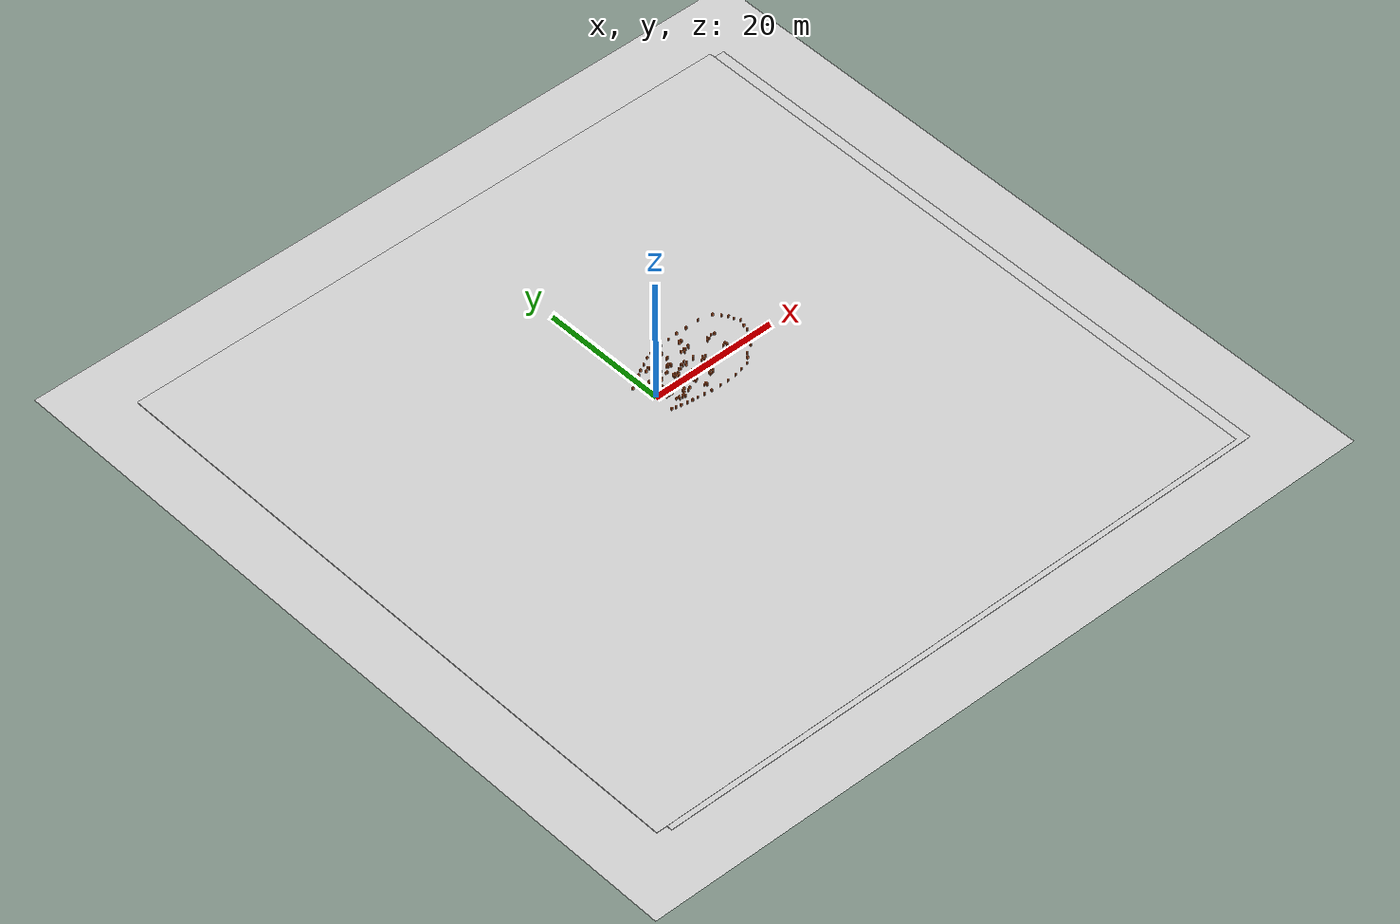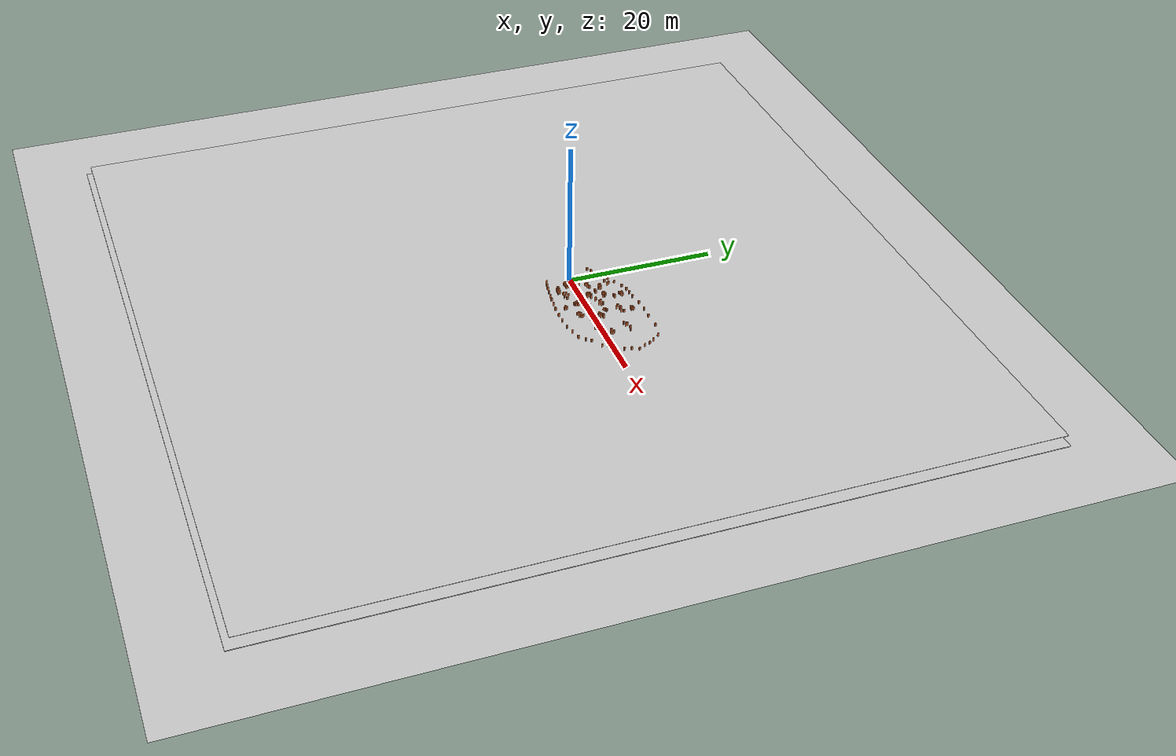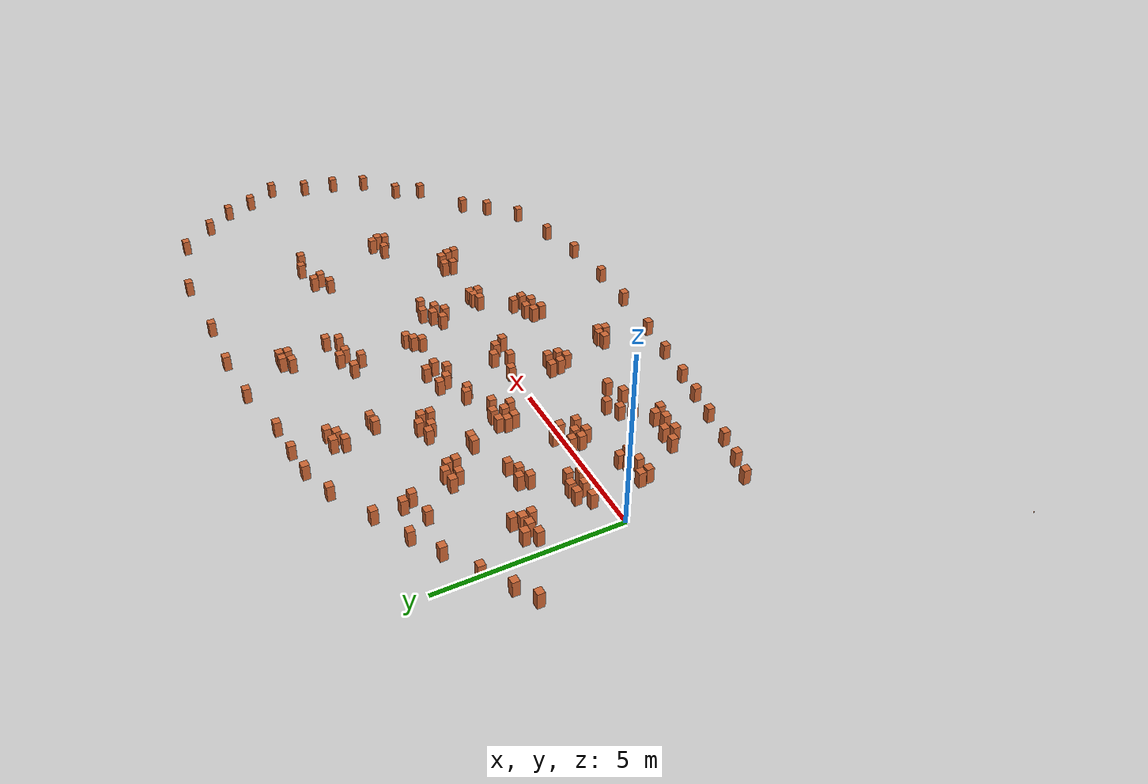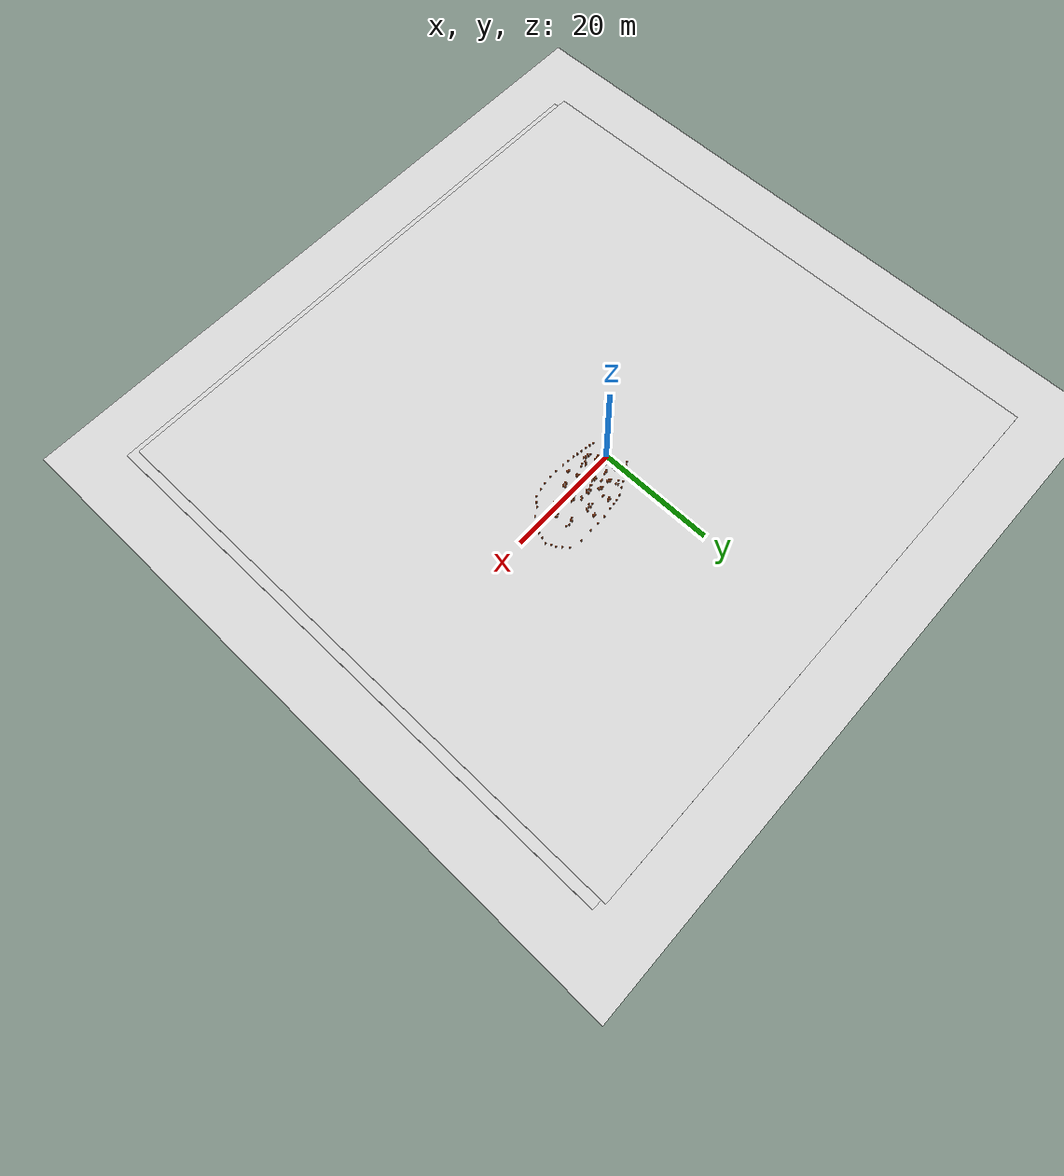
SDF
<sdf version='1.9'>
  <world name='default'>
    <gravity>0 0 -9.8</gravity>
    <magnetic_field>6e-06 2.3e-05 -4.2e-05</magnetic_field>
    <atmosphere type='adiabatic'/>
    <physics type='ode'>
      <max_step_size>0.001</max_step_size>
      <real_time_factor>1</real_time_factor>
      <real_time_update_rate>1000</real_time_update_rate>
    </physics>
    <scene>
      <ambient>0.6 0.6 0.6 1</ambient>
      <background>0.7 0.7 0.7 1</background>
      <shadows>true</shadows>
    </scene>
    <audio>
      <device>default</device>
    </audio>
    <wind/>
    <spherical_coordinates>
      <surface_model>EARTH_WGS84</surface_model>
      <latitude_deg>0</latitude_deg>
      <longitude_deg>0</longitude_deg>
      <elevation>0</elevation>
      <heading_deg>0</heading_deg>
    </spherical_coordinates>
    <model name='ground_plane'>
      <static>true</static>
      <link name='link'>
        <collision name='collision'>
          <geometry>
            <plane>
              <normal>0 0 1</normal>
              <size>100 100</size>
            </plane>
          </geometry>
          <surface>
            <friction>
              <ode>
                <mu>100</mu>
                <mu2>50</mu2>
              </ode>
              <torsional>
                <ode/>
              </torsional>
            </friction>
            <contact>
              <ode/>
            </contact>
            <bounce/>
          </surface>
          <max_contacts>10</max_contacts>
        </collision>
        <visual name='visual'>
          <cast_shadows>false</cast_shadows>
          <geometry>
            <plane>
              <normal>0 0 1</normal>
              <size>100 100</size>
            </plane>
          </geometry>
          <material>
            <ambient>0.6 0.6 0.6 1</ambient>
            <diffuse>0.8 0.8 0.8 1</diffuse>
            <specular>0.1 0.1 0.1 1</specular>
          </material>
        </visual>
        <self_collide>false</self_collide>
        <enable_wind>false</enable_wind>
        <kinematic>false</kinematic>
        <pose>0 0 0 0 -0 0</pose>
        <inertial>
          <pose>0 0 0 0 -0 0</pose>
          <mass>1</mass>
          <inertia>
            <ixx>1</ixx>
            <ixy>0</ixy>
            <ixz>0</ixz>
            <iyy>1</iyy>
            <iyz>0</iyz>
            <izz>1</izz>
          </inertia>
        </inertial>
      </link>
      <pose>0 0 0 0 -0 0</pose>
      <self_collide>false</self_collide>
    </model>
    <model name='wooden_peg'>
      <link name='link'>
        <pose>0 0 0.04 0 -0 0</pose>
        <inertial>
          <mass>0.017500000000000002</mass>
          <inertia>
            <ixx>9.7492300000000002e-06</ixx>
            <ixy>0</ixy>
            <ixz>0</ixz>
            <iyy>9.7492300000000002e-06</iyy>
            <iyz>0</iyz>
            <izz>8.3179700000000005e-07</izz>
          </inertia>
          <pose>0 0 0 0 -0 0</pose>
        </inertial>
        <collision name='collision'>
          <geometry>
            <cylinder>
              <radius>0.00975</radius>
              <length>0.080000000000000002</length>
            </cylinder>
          </geometry>
          <surface>
            <contact>
              <poissons_ratio>0.34699999999999998</poissons_ratio>
              <elastic_modulus>8800000000</elastic_modulus>
              <ode>
                <kp>100000</kp>
                <kd>100</kd>
                <max_vel>100</max_vel>
                <min_depth>0.001</min_depth>
              </ode>
            </contact>
            <friction>
              <torsional>
                <coefficient>1</coefficient>
                <use_patch_radius>false</use_patch_radius>
                <surface_radius>0.01</surface_radius>
                <ode/>
              </torsional>
              <ode/>
            </friction>
            <bounce/>
          </surface>
          <max_contacts>10</max_contacts>
        </collision>
        <visual name='visual'>
          <geometry>
            <cylinder>
              <radius>0.00975</radius>
              <length>0.080000000000000002</length>
            </cylinder>
          </geometry>
          <material>
            <ambient>0.6 0.3 0.1 1</ambient>
            <diffuse>0.8 0.4 0.2 1</diffuse>
            <specular>0.1 0.1 0.1 1</specular>
          </material>
        </visual>
        <self_collide>false</self_collide>
        <enable_wind>false</enable_wind>
        <kinematic>false</kinematic>
      </link>
      <pose>-4.09392 -8.67002 0.049999 0 -0 0</pose>
      <static>false</static>
      <self_collide>false</self_collide>
    </model>
    <model name='ground_plane_0'>
      <static>true</static>
      <link name='link'>
        <collision name='collision'>
          <geometry>
            <plane>
              <normal>0 0 1</normal>
              <size>100 100</size>
            </plane>
          </geometry>
          <surface>
            <friction>
              <ode>
                <mu>100</mu>
                <mu2>50</mu2>
              </ode>
              <torsional>
                <ode/>
              </torsional>
            </friction>
            <contact>
              <ode/>
            </contact>
            <bounce/>
          </surface>
          <max_contacts>10</max_contacts>
        </collision>
        <visual name='visual'>
          <cast_shadows>false</cast_shadows>
          <geometry>
            <plane>
              <normal>0 0 1</normal>
              <size>100 100</size>
            </plane>
          </geometry>
          <material>
            <ambient>0.6 0.6 0.6 1</ambient>
            <diffuse>0.8 0.8 0.8 1</diffuse>
            <specular>0.1 0.1 0.1 1</specular>
          </material>
        </visual>
        <self_collide>false</self_collide>
        <enable_wind>false</enable_wind>
        <kinematic>false</kinematic>
        <pose>0 0 0 0 -0 0</pose>
        <inertial>
          <pose>0 0 0 0 -0 0</pose>
          <mass>1</mass>
          <inertia>
            <ixx>1</ixx>
            <ixy>0</ixy>
            <ixz>0</ixz>
            <iyy>1</iyy>
            <iyz>0</iyz>
            <izz>1</izz>
          </inertia>
        </inertial>
      </link>
      <pose>1.5012 -6.55838 0 0 -0 0</pose>
      <self_collide>false</self_collide>
    </model>
    <model name='ground_plane_0_clone'>
      <static>true</static>
      <link name='link'>
        <collision name='collision'>
          <geometry>
            <plane>
              <normal>0 0 1</normal>
              <size>100 100</size>
            </plane>
          </geometry>
          <surface>
            <friction>
              <ode>
                <mu>100</mu>
                <mu2>50</mu2>
              </ode>
              <torsional>
                <ode/>
              </torsional>
            </friction>
            <contact>
              <ode/>
            </contact>
            <bounce/>
          </surface>
          <max_contacts>10</max_contacts>
        </collision>
        <visual name='visual'>
          <cast_shadows>false</cast_shadows>
          <geometry>
            <plane>
              <normal>0 0 1</normal>
              <size>100 100</size>
            </plane>
          </geometry>
          <material>
            <ambient>0.6 0.6 0.6 1</ambient>
            <diffuse>0.8 0.8 0.8 1</diffuse>
            <specular>0.1 0.1 0.1 1</specular>
          </material>
        </visual>
        <self_collide>false</self_collide>
        <enable_wind>false</enable_wind>
        <kinematic>false</kinematic>
        <pose>0 0 0 0 -0 0</pose>
        <inertial>
          <pose>0 0 0 0 -0 0</pose>
          <mass>1</mass>
          <inertia>
            <ixx>1</ixx>
            <ixy>0</ixy>
            <ixz>0</ixz>
            <iyy>1</iyy>
            <iyz>0</iyz>
            <izz>1</izz>
          </inertia>
        </inertial>
      </link>
      <pose>-0.197798 -5.73732 0.05 0 -0 0</pose>
      <self_collide>false</self_collide>
    </model>

    <model name='wood_cube_10cm_clone_0_clone_1'>
      <link name='link'>
        <pose>0 0 0.05 0 -0 0</pose>
        <inertial>
          <mass>0.51670000000000005</mass>
          <inertia>
            <ixx>0.00086116700000000003</ixx>
            <ixy>0</ixy>
            <ixz>0</ixz>
            <iyy>0.00086116700000000003</iyy>
            <iyz>0</iyz>
            <izz>0.00086116700000000003</izz>
          </inertia>
          <pose>0 0 0 0 -0 0</pose>
        </inertial>
        <collision name='collision'>
          <geometry>
            <box>
              <size>0.2 0.2 0.5</size>
            </box>
          </geometry>
          <surface>
            <contact>
              <poissons_ratio>0.34699999999999998</poissons_ratio>
              <elastic_modulus>8800000000</elastic_modulus>
              <ode>
                <kp>100000</kp>
                <kd>100</kd>
                <max_vel>100</max_vel>
                <min_depth>0.001</min_depth>
              </ode>
            </contact>
            <friction>
              <torsional>
                <coefficient>1</coefficient>
                <use_patch_radius>false</use_patch_radius>
                <surface_radius>0.01</surface_radius>
                <ode/>
              </torsional>
              <ode/>
            </friction>
            <bounce/>
          </surface>
          <max_contacts>10</max_contacts>
        </collision>
        <visual name='visual'>
          <geometry>
            <box>
              <size>0.2 0.2 0.5</size>
            </box>
          </geometry>
          <material>
            <ambient>0.6 0.3 0.1 1</ambient>
            <diffuse>0.8 0.4 0.2 1</diffuse>
            <specular>0.1 0.1 0.1 1</specular>
          </material>
        </visual>
        <self_collide>false</self_collide>
        <enable_wind>false</enable_wind>
        <kinematic>false</kinematic>
      </link>
      <pose>1.30046 0.792033 0.25 0 0 -0</pose>
      <static>false</static>
      <self_collide>false</self_collide>
    </model>
    <model name='wood_cube_10cm_clone_0_clone_2'>
      <link name='link'>
        <pose>0 0 0.05 0 -0 0</pose>
        <inertial>
          <mass>0.51670000000000005</mass>
          <inertia>
            <ixx>0.00086116700000000003</ixx>
            <ixy>0</ixy>
            <ixz>0</ixz>
            <iyy>0.00086116700000000003</iyy>
            <iyz>0</iyz>
            <izz>0.00086116700000000003</izz>
          </inertia>
          <pose>0 0 0 0 -0 0</pose>
        </inertial>
        <collision name='collision'>
          <geometry>
            <box>
              <size>0.2 0.2 0.5</size>
            </box>
          </geometry>
          <surface>
            <contact>
              <poissons_ratio>0.34699999999999998</poissons_ratio>
              <elastic_modulus>8800000000</elastic_modulus>
              <ode>
                <kp>100000</kp>
                <kd>100</kd>
                <max_vel>100</max_vel>
                <min_depth>0.001</min_depth>
              </ode>
            </contact>
            <friction>
              <torsional>
                <coefficient>1</coefficient>
                <use_patch_radius>false</use_patch_radius>
                <surface_radius>0.01</surface_radius>
                <ode/>
              </torsional>
              <ode/>
            </friction>
            <bounce/>
          </surface>
          <max_contacts>10</max_contacts>
        </collision>
        <visual name='visual'>
          <geometry>
            <box>
              <size>0.2 0.2 0.5</size>
            </box>
          </geometry>
          <material>
            <ambient>0.6 0.3 0.1 1</ambient>
            <diffuse>0.8 0.4 0.2 1</diffuse>
            <specular>0.1 0.1 0.1 1</specular>
          </material>
        </visual>
        <self_collide>false</self_collide>
        <enable_wind>false</enable_wind>
        <kinematic>false</kinematic>
      </link>
      <pose>1.00724 0.77848 0.249999 0 -0 0</pose>
      <static>false</static>
      <self_collide>false</self_collide>
    </model>
    <model name='wood_cube_10cm_clone_0_clone_3'>
      <link name='link'>
        <pose>0 0 0.05 0 -0 0</pose>
        <inertial>
          <mass>0.51670000000000005</mass>
          <inertia>
            <ixx>0.00086116700000000003</ixx>
            <ixy>0</ixy>
            <ixz>0</ixz>
            <iyy>0.00086116700000000003</iyy>
            <iyz>0</iyz>
            <izz>0.00086116700000000003</izz>
          </inertia>
          <pose>0 0 0 0 -0 0</pose>
        </inertial>
        <collision name='collision'>
          <geometry>
            <box>
              <size>0.2 0.2 0.5</size>
            </box>
          </geometry>
          <surface>
            <contact>
              <poissons_ratio>0.34699999999999998</poissons_ratio>
              <elastic_modulus>8800000000</elastic_modulus>
              <ode>
                <kp>100000</kp>
                <kd>100</kd>
                <max_vel>100</max_vel>
                <min_depth>0.001</min_depth>
              </ode>
            </contact>
            <friction>
              <torsional>
                <coefficient>1</coefficient>
                <use_patch_radius>false</use_patch_radius>
                <surface_radius>0.01</surface_radius>
                <ode/>
              </torsional>
              <ode/>
            </friction>
            <bounce/>
          </surface>
          <max_contacts>10</max_contacts>
        </collision>
        <visual name='visual'>
          <geometry>
            <box>
              <size>0.2 0.2 0.5</size>
            </box>
          </geometry>
          <material>
            <ambient>0.6 0.3 0.1 1</ambient>
            <diffuse>0.8 0.4 0.2 1</diffuse>
            <specular>0.1 0.1 0.1 1</specular>
          </material>
        </visual>
        <self_collide>false</self_collide>
        <enable_wind>false</enable_wind>
        <kinematic>false</kinematic>
      </link>
      <pose>1.18442 0.477456 0.249999 0 -0 -0</pose>
      <static>false</static>
      <self_collide>false</self_collide>
    </model>
    <model name='wood_cube_10cm_clone_0_clone_4'>
      <link name='link'>
        <pose>0 0 0.05 0 -0 0</pose>
        <inertial>
          <mass>0.51670000000000005</mass>
          <inertia>
            <ixx>0.00086116700000000003</ixx>
            <ixy>0</ixy>
            <ixz>0</ixz>
            <iyy>0.00086116700000000003</iyy>
            <iyz>0</iyz>
            <izz>0.00086116700000000003</izz>
          </inertia>
          <pose>0 0 0 0 -0 0</pose>
        </inertial>
        <collision name='collision'>
          <geometry>
            <box>
              <size>0.2 0.2 0.5</size>
            </box>
          </geometry>
          <surface>
            <contact>
              <poissons_ratio>0.34699999999999998</poissons_ratio>
              <elastic_modulus>8800000000</elastic_modulus>
              <ode>
                <kp>100000</kp>
                <kd>100</kd>
                <max_vel>100</max_vel>
                <min_depth>0.001</min_depth>
              </ode>
            </contact>
            <friction>
              <torsional>
                <coefficient>1</coefficient>
                <use_patch_radius>false</use_patch_radius>
                <surface_radius>0.01</surface_radius>
                <ode/>
              </torsional>
              <ode/>
            </friction>
            <bounce/>
          </surface>
          <max_contacts>10</max_contacts>
        </collision>
        <visual name='visual'>
          <geometry>
            <box>
              <size>0.2 0.2 0.5</size>
            </box>
          </geometry>
          <material>
            <ambient>0.6 0.3 0.1 1</ambient>
            <diffuse>0.8 0.4 0.2 1</diffuse>
            <specular>0.1 0.1 0.1 1</specular>
          </material>
        </visual>
        <self_collide>false</self_collide>
        <enable_wind>false</enable_wind>
        <kinematic>false</kinematic>
      </link>
      <pose>0.748848 0.49402 0.25 0 0 0</pose>
      <static>false</static>
      <self_collide>false</self_collide>
    </model>
    <model name='wood_cube_10cm_clone_0_clone_5'>
      <link name='link'>
        <pose>0 0 0.05 0 -0 0</pose>
        <inertial>
          <mass>0.51670000000000005</mass>
          <inertia>
            <ixx>0.00086116700000000003</ixx>
            <ixy>0</ixy>
            <ixz>0</ixz>
            <iyy>0.00086116700000000003</iyy>
            <iyz>0</iyz>
            <izz>0.00086116700000000003</izz>
          </inertia>
          <pose>0 0 0 0 -0 0</pose>
        </inertial>
        <collision name='collision'>
          <geometry>
            <box>
              <size>0.2 0.2 0.5</size>
            </box>
          </geometry>
          <surface>
            <contact>
              <poissons_ratio>0.34699999999999998</poissons_ratio>
              <elastic_modulus>8800000000</elastic_modulus>
              <ode>
                <kp>100000</kp>
                <kd>100</kd>
                <max_vel>100</max_vel>
                <min_depth>0.001</min_depth>
              </ode>
            </contact>
            <friction>
              <torsional>
                <coefficient>1</coefficient>
                <use_patch_radius>false</use_patch_radius>
                <surface_radius>0.01</surface_radius>
                <ode/>
              </torsional>
              <ode/>
            </friction>
            <bounce/>
          </surface>
          <max_contacts>10</max_contacts>
        </collision>
        <visual name='visual'>
          <geometry>
            <box>
              <size>0.2 0.2 0.5</size>
            </box>
          </geometry>
          <material>
            <ambient>0.6 0.3 0.1 1</ambient>
            <diffuse>0.8 0.4 0.2 1</diffuse>
            <specular>0.1 0.1 0.1 1</specular>
          </material>
        </visual>
        <self_collide>false</self_collide>
        <enable_wind>false</enable_wind>
        <kinematic>false</kinematic>
      </link>
      <pose>1.65238 0.667249 0.249999 0 0 0</pose>
      <static>false</static>
      <self_collide>false</self_collide>
    </model>
    <model name='wood_cube_10cm_clone_0_clone_6'>
      <link name='link'>
        <pose>0 0 0.05 0 -0 0</pose>
        <inertial>
          <mass>0.51670000000000005</mass>
          <inertia>
            <ixx>0.00086116700000000003</ixx>
            <ixy>0</ixy>
            <ixz>0</ixz>
            <iyy>0.00086116700000000003</iyy>
            <iyz>0</iyz>
            <izz>0.00086116700000000003</izz>
          </inertia>
          <pose>0 0 0 0 -0 0</pose>
        </inertial>
        <collision name='collision'>
          <geometry>
            <box>
              <size>0.2 0.2 0.5</size>
            </box>
          </geometry>
          <surface>
            <contact>
              <poissons_ratio>0.34699999999999998</poissons_ratio>
              <elastic_modulus>8800000000</elastic_modulus>
              <ode>
                <kp>100000</kp>
                <kd>100</kd>
                <max_vel>100</max_vel>
                <min_depth>0.001</min_depth>
              </ode>
            </contact>
            <friction>
              <torsional>
                <coefficient>1</coefficient>
                <use_patch_radius>false</use_patch_radius>
                <surface_radius>0.01</surface_radius>
                <ode/>
              </torsional>
              <ode/>
            </friction>
            <bounce/>
          </surface>
          <max_contacts>10</max_contacts>
        </collision>
        <visual name='visual'>
          <geometry>
            <box>
              <size>0.2 0.2 0.5</size>
            </box>
          </geometry>
          <material>
            <ambient>0.6 0.3 0.1 1</ambient>
            <diffuse>0.8 0.4 0.2 1</diffuse>
            <specular>0.1 0.1 0.1 1</specular>
          </material>
        </visual>
        <self_collide>false</self_collide>
        <enable_wind>false</enable_wind>
        <kinematic>false</kinematic>
      </link>
      <pose>1.54547 0.378806 0.249999 -0 -0 -0</pose>
      <static>false</static>
      <self_collide>false</self_collide>
    </model>
    <model name='wood_cube_10cm_clone_0_clone_4_1'>
      <link name='link'>
        <pose>0 0 0.05 0 -0 0</pose>
        <inertial>
          <mass>0.51670000000000005</mass>
          <inertia>
            <ixx>0.00086116700000000003</ixx>
            <ixy>0</ixy>
            <ixz>0</ixz>
            <iyy>0.00086116700000000003</iyy>
            <iyz>0</iyz>
            <izz>0.00086116700000000003</izz>
          </inertia>
          <pose>0 0 0 0 -0 0</pose>
        </inertial>
        <collision name='collision'>
          <geometry>
            <box>
              <size>0.2 0.2 0.5</size>
            </box>
          </geometry>
          <surface>
            <contact>
              <poissons_ratio>0.34699999999999998</poissons_ratio>
              <elastic_modulus>8800000000</elastic_modulus>
              <ode>
                <kp>100000</kp>
                <kd>100</kd>
                <max_vel>100</max_vel>
                <min_depth>0.001</min_depth>
              </ode>
            </contact>
            <friction>
              <torsional>
                <coefficient>1</coefficient>
                <use_patch_radius>false</use_patch_radius>
                <surface_radius>0.01</surface_radius>
                <ode/>
              </torsional>
              <ode/>
            </friction>
            <bounce/>
          </surface>
          <max_contacts>10</max_contacts>
        </collision>
        <visual name='visual'>
          <geometry>
            <box>
              <size>0.2 0.2 0.5</size>
            </box>
          </geometry>
          <material>
            <ambient>0.6 0.3 0.1 1</ambient>
            <diffuse>0.8 0.4 0.2 1</diffuse>
            <specular>0.1 0.1 0.1 1</specular>
          </material>
        </visual>
        <self_collide>false</self_collide>
        <enable_wind>false</enable_wind>
        <kinematic>false</kinematic>
      </link>
      <pose>2.67176 0.017737 0.249999 -0 -0 -0</pose>
      <static>false</static>
      <self_collide>false</self_collide>
    </model>
    <model name='wood_cube_10cm_clone_0_clone_4_2'>
      <link name='link'>
        <pose>0 0 0.05 0 -0 0</pose>
        <inertial>
          <mass>0.51670000000000005</mass>
          <inertia>
            <ixx>0.00086116700000000003</ixx>
            <ixy>0</ixy>
            <ixz>0</ixz>
            <iyy>0.00086116700000000003</iyy>
            <iyz>0</iyz>
            <izz>0.00086116700000000003</izz>
          </inertia>
          <pose>0 0 0 0 -0 0</pose>
        </inertial>
        <collision name='collision'>
          <geometry>
            <box>
              <size>0.2 0.2 0.5</size>
            </box>
          </geometry>
          <surface>
            <contact>
              <poissons_ratio>0.34699999999999998</poissons_ratio>
              <elastic_modulus>8800000000</elastic_modulus>
              <ode>
                <kp>100000</kp>
                <kd>100</kd>
                <max_vel>100</max_vel>
                <min_depth>0.001</min_depth>
              </ode>
            </contact>
            <friction>
              <torsional>
                <coefficient>1</coefficient>
                <use_patch_radius>false</use_patch_radius>
                <surface_radius>0.01</surface_radius>
                <ode/>
              </torsional>
              <ode/>
            </friction>
            <bounce/>
          </surface>
          <max_contacts>10</max_contacts>
        </collision>
        <visual name='visual'>
          <geometry>
            <box>
              <size>0.2 0.2 0.5</size>
            </box>
          </geometry>
          <material>
            <ambient>0.6 0.3 0.1 1</ambient>
            <diffuse>0.8 0.4 0.2 1</diffuse>
            <specular>0.1 0.1 0.1 1</specular>
          </material>
        </visual>
        <self_collide>false</self_collide>
        <enable_wind>false</enable_wind>
        <kinematic>false</kinematic>
      </link>
      <pose>2.91344 -0.189719 0.249999 -0 0 -0</pose>
      <static>false</static>
      <self_collide>false</self_collide>
    </model>
    <model name='wood_cube_10cm_clone_0_clone_4_3'>
      <link name='link'>
        <pose>0 0 0.05 0 -0 0</pose>
        <inertial>
          <mass>0.51670000000000005</mass>
          <inertia>
            <ixx>0.00086116700000000003</ixx>
            <ixy>0</ixy>
            <ixz>0</ixz>
            <iyy>0.00086116700000000003</iyy>
            <iyz>0</iyz>
            <izz>0.00086116700000000003</izz>
          </inertia>
          <pose>0 0 0 0 -0 0</pose>
        </inertial>
        <collision name='collision'>
          <geometry>
            <box>
              <size>0.2 0.2 0.5</size>
            </box>
          </geometry>
          <surface>
            <contact>
              <poissons_ratio>0.34699999999999998</poissons_ratio>
              <elastic_modulus>8800000000</elastic_modulus>
              <ode>
                <kp>100000</kp>
                <kd>100</kd>
                <max_vel>100</max_vel>
                <min_depth>0.001</min_depth>
              </ode>
            </contact>
            <friction>
              <torsional>
                <coefficient>1</coefficient>
                <use_patch_radius>false</use_patch_radius>
                <surface_radius>0.01</surface_radius>
                <ode/>
              </torsional>
              <ode/>
            </friction>
            <bounce/>
          </surface>
          <max_contacts>10</max_contacts>
        </collision>
        <visual name='visual'>
          <geometry>
            <box>
              <size>0.2 0.2 0.5</size>
            </box>
          </geometry>
          <material>
            <ambient>0.6 0.3 0.1 1</ambient>
            <diffuse>0.8 0.4 0.2 1</diffuse>
            <specular>0.1 0.1 0.1 1</specular>
          </material>
        </visual>
        <self_collide>false</self_collide>
        <enable_wind>false</enable_wind>
        <kinematic>false</kinematic>
      </link>
      <pose>3.25851 0.046879 0.249999 -0 0 -0</pose>
      <static>false</static>
      <self_collide>false</self_collide>
    </model>
    <model name='wood_cube_10cm_clone_0_clone_4_4'>
      <link name='link'>
        <pose>0 0 0.05 0 -0 0</pose>
        <inertial>
          <mass>0.51670000000000005</mass>
          <inertia>
            <ixx>0.00086116700000000003</ixx>
            <ixy>0</ixy>
            <ixz>0</ixz>
            <iyy>0.00086116700000000003</iyy>
            <iyz>0</iyz>
            <izz>0.00086116700000000003</izz>
          </inertia>
          <pose>0 0 0 0 -0 0</pose>
        </inertial>
        <collision name='collision'>
          <geometry>
            <box>
              <size>0.2 0.2 0.5</size>
            </box>
          </geometry>
          <surface>
            <contact>
              <poissons_ratio>0.34699999999999998</poissons_ratio>
              <elastic_modulus>8800000000</elastic_modulus>
              <ode>
                <kp>100000</kp>
                <kd>100</kd>
                <max_vel>100</max_vel>
                <min_depth>0.001</min_depth>
              </ode>
            </contact>
            <friction>
              <torsional>
                <coefficient>1</coefficient>
                <use_patch_radius>false</use_patch_radius>
                <surface_radius>0.01</surface_radius>
                <ode/>
              </torsional>
              <ode/>
            </friction>
            <bounce/>
          </surface>
          <max_contacts>10</max_contacts>
        </collision>
        <visual name='visual'>
          <geometry>
            <box>
              <size>0.2 0.2 0.5</size>
            </box>
          </geometry>
          <material>
            <ambient>0.6 0.3 0.1 1</ambient>
            <diffuse>0.8 0.4 0.2 1</diffuse>
            <specular>0.1 0.1 0.1 1</specular>
          </material>
        </visual>
        <self_collide>false</self_collide>
        <enable_wind>false</enable_wind>
        <kinematic>false</kinematic>
      </link>
      <pose>3.06552 0.299131 0.249999 -0 0 -0</pose>
      <static>false</static>
      <self_collide>false</self_collide>
    </model>
    <model name='wood_cube_10cm_clone_0_clone_4_5'>
      <link name='link'>
        <pose>0 0 0.05 0 -0 0</pose>
        <inertial>
          <mass>0.51670000000000005</mass>
          <inertia>
            <ixx>0.00086116700000000003</ixx>
            <ixy>0</ixy>
            <ixz>0</ixz>
            <iyy>0.00086116700000000003</iyy>
            <iyz>0</iyz>
            <izz>0.00086116700000000003</izz>
          </inertia>
          <pose>0 0 0 0 -0 0</pose>
        </inertial>
        <collision name='collision'>
          <geometry>
            <box>
              <size>0.2 0.2 0.5</size>
            </box>
          </geometry>
          <surface>
            <contact>
              <poissons_ratio>0.34699999999999998</poissons_ratio>
              <elastic_modulus>8800000000</elastic_modulus>
              <ode>
                <kp>100000</kp>
                <kd>100</kd>
                <max_vel>100</max_vel>
                <min_depth>0.001</min_depth>
              </ode>
            </contact>
            <friction>
              <torsional>
                <coefficient>1</coefficient>
                <use_patch_radius>false</use_patch_radius>
                <surface_radius>0.01</surface_radius>
                <ode/>
              </torsional>
              <ode/>
            </friction>
            <bounce/>
          </surface>
          <max_contacts>10</max_contacts>
        </collision>
        <visual name='visual'>
          <geometry>
            <box>
              <size>0.2 0.2 0.5</size>
            </box>
          </geometry>
          <material>
            <ambient>0.6 0.3 0.1 1</ambient>
            <diffuse>0.8 0.4 0.2 1</diffuse>
            <specular>0.1 0.1 0.1 1</specular>
          </material>
        </visual>
        <self_collide>false</self_collide>
        <enable_wind>false</enable_wind>
        <kinematic>false</kinematic>
      </link>
      <pose>2.64649 -0.233893 0.249999 -0 0 -0</pose>
      <static>false</static>
      <self_collide>false</self_collide>
    </model>
    <model name='wood_cube_10cm_clone_0_clone_4_6'>
      <link name='link'>
        <pose>0 0 0.05 0 -0 0</pose>
        <inertial>
          <mass>0.51670000000000005</mass>
          <inertia>
            <ixx>0.00086116700000000003</ixx>
            <ixy>0</ixy>
            <ixz>0</ixz>
            <iyy>0.00086116700000000003</iyy>
            <iyz>0</iyz>
            <izz>0.00086116700000000003</izz>
          </inertia>
          <pose>0 0 0 0 -0 0</pose>
        </inertial>
        <collision name='collision'>
          <geometry>
            <box>
              <size>0.2 0.2 0.5</size>
            </box>
          </geometry>
          <surface>
            <contact>
              <poissons_ratio>0.34699999999999998</poissons_ratio>
              <elastic_modulus>8800000000</elastic_modulus>
              <ode>
                <kp>100000</kp>
                <kd>100</kd>
                <max_vel>100</max_vel>
                <min_depth>0.001</min_depth>
              </ode>
            </contact>
            <friction>
              <torsional>
                <coefficient>1</coefficient>
                <use_patch_radius>false</use_patch_radius>
                <surface_radius>0.01</surface_radius>
                <ode/>
              </torsional>
              <ode/>
            </friction>
            <bounce/>
          </surface>
          <max_contacts>10</max_contacts>
        </collision>
        <visual name='visual'>
          <geometry>
            <box>
              <size>0.2 0.2 0.5</size>
            </box>
          </geometry>
          <material>
            <ambient>0.6 0.3 0.1 1</ambient>
            <diffuse>0.8 0.4 0.2 1</diffuse>
            <specular>0.1 0.1 0.1 1</specular>
          </material>
        </visual>
        <self_collide>false</self_collide>
        <enable_wind>false</enable_wind>
        <kinematic>false</kinematic>
      </link>
      <pose>3.2455 -0.406573 0.249999 0 -0 0</pose>
      <static>false</static>
      <self_collide>false</self_collide>
    </model>
    <model name='wood_cube_10cm_clone_0_clone_4_7'>
      <link name='link'>
        <pose>0 0 0.05 0 -0 0</pose>
        <inertial>
          <mass>0.51670000000000005</mass>
          <inertia>
            <ixx>0.00086116700000000003</ixx>
            <ixy>0</ixy>
            <ixz>0</ixz>
            <iyy>0.00086116700000000003</iyy>
            <iyz>0</iyz>
            <izz>0.00086116700000000003</izz>
          </inertia>
          <pose>0 0 0 0 -0 0</pose>
        </inertial>
        <collision name='collision'>
          <geometry>
            <box>
              <size>0.2 0.2 0.5</size>
            </box>
          </geometry>
          <surface>
            <contact>
              <poissons_ratio>0.34699999999999998</poissons_ratio>
              <elastic_modulus>8800000000</elastic_modulus>
              <ode>
                <kp>100000</kp>
                <kd>100</kd>
                <max_vel>100</max_vel>
                <min_depth>0.001</min_depth>
              </ode>
            </contact>
            <friction>
              <torsional>
                <coefficient>1</coefficient>
                <use_patch_radius>false</use_patch_radius>
                <surface_radius>0.01</surface_radius>
                <ode/>
              </torsional>
              <ode/>
            </friction>
            <bounce/>
          </surface>
          <max_contacts>10</max_contacts>
        </collision>
        <visual name='visual'>
          <geometry>
            <box>
              <size>0.2 0.2 0.5</size>
            </box>
          </geometry>
          <material>
            <ambient>0.6 0.3 0.1 1</ambient>
            <diffuse>0.8 0.4 0.2 1</diffuse>
            <specular>0.1 0.1 0.1 1</specular>
          </material>
        </visual>
        <self_collide>false</self_collide>
        <enable_wind>false</enable_wind>
        <kinematic>false</kinematic>
      </link>
      <pose>2.81233 -0.458576 0.249999 -0 0 -0</pose>
      <static>false</static>
      <self_collide>false</self_collide>
    </model>
    <model name='wood_cube_10cm_clone_0_clone_4_8'>
      <link name='link'>
        <pose>0 0 0.05 0 -0 0</pose>
        <inertial>
          <mass>0.51670000000000005</mass>
          <inertia>
            <ixx>0.00086116700000000003</ixx>
            <ixy>0</ixy>
            <ixz>0</ixz>
            <iyy>0.00086116700000000003</iyy>
            <iyz>0</iyz>
            <izz>0.00086116700000000003</izz>
          </inertia>
          <pose>0 0 0 0 -0 0</pose>
        </inertial>
        <collision name='collision'>
          <geometry>
            <box>
              <size>0.2 0.2 0.5</size>
            </box>
          </geometry>
          <surface>
            <contact>
              <poissons_ratio>0.34699999999999998</poissons_ratio>
              <elastic_modulus>8800000000</elastic_modulus>
              <ode>
                <kp>100000</kp>
                <kd>100</kd>
                <max_vel>100</max_vel>
                <min_depth>0.001</min_depth>
              </ode>
            </contact>
            <friction>
              <torsional>
                <coefficient>1</coefficient>
                <use_patch_radius>false</use_patch_radius>
                <surface_radius>0.01</surface_radius>
                <ode/>
              </torsional>
              <ode/>
            </friction>
            <bounce/>
          </surface>
          <max_contacts>10</max_contacts>
        </collision>
        <visual name='visual'>
          <geometry>
            <box>
              <size>0.2 0.2 0.5</size>
            </box>
          </geometry>
          <material>
            <ambient>0.6 0.3 0.1 1</ambient>
            <diffuse>0.8 0.4 0.2 1</diffuse>
            <specular>0.1 0.1 0.1 1</specular>
          </material>
        </visual>
        <self_collide>false</self_collide>
        <enable_wind>false</enable_wind>
        <kinematic>false</kinematic>
      </link>
      <pose>1.63168 -0.747012 0.249999 -0 0 -0</pose>
      <static>false</static>
      <self_collide>false</self_collide>
    </model>
    <model name='wood_cube_10cm_clone_0_clone_4_9'>
      <link name='link'>
        <pose>0 0 0.05 0 -0 0</pose>
        <inertial>
          <mass>0.51670000000000005</mass>
          <inertia>
            <ixx>0.00086116700000000003</ixx>
            <ixy>0</ixy>
            <ixz>0</ixz>
            <iyy>0.00086116700000000003</iyy>
            <iyz>0</iyz>
            <izz>0.00086116700000000003</izz>
          </inertia>
          <pose>0 0 0 0 -0 0</pose>
        </inertial>
        <collision name='collision'>
          <geometry>
            <box>
              <size>0.2 0.2 0.5</size>
            </box>
          </geometry>
          <surface>
            <contact>
              <poissons_ratio>0.34699999999999998</poissons_ratio>
              <elastic_modulus>8800000000</elastic_modulus>
              <ode>
                <kp>100000</kp>
                <kd>100</kd>
                <max_vel>100</max_vel>
                <min_depth>0.001</min_depth>
              </ode>
            </contact>
            <friction>
              <torsional>
                <coefficient>1</coefficient>
                <use_patch_radius>false</use_patch_radius>
                <surface_radius>0.01</surface_radius>
                <ode/>
              </torsional>
              <ode/>
            </friction>
            <bounce/>
          </surface>
          <max_contacts>10</max_contacts>
        </collision>
        <visual name='visual'>
          <geometry>
            <box>
              <size>0.2 0.2 0.5</size>
            </box>
          </geometry>
          <material>
            <ambient>0.6 0.3 0.1 1</ambient>
            <diffuse>0.8 0.4 0.2 1</diffuse>
            <specular>0.1 0.1 0.1 1</specular>
          </material>
        </visual>
        <self_collide>false</self_collide>
        <enable_wind>false</enable_wind>
        <kinematic>false</kinematic>
      </link>
      <pose>1.40973 -0.865742 0.249999 -0 0 -0</pose>
      <static>false</static>
      <self_collide>false</self_collide>
    </model>
    <model name='wood_cube_10cm_clone_0_clone_4_10'>
      <link name='link'>
        <pose>0 0 0.05 0 -0 0</pose>
        <inertial>
          <mass>0.51670000000000005</mass>
          <inertia>
            <ixx>0.00086116700000000003</ixx>
            <ixy>0</ixy>
            <ixz>0</ixz>
            <iyy>0.00086116700000000003</iyy>
            <iyz>0</iyz>
            <izz>0.00086116700000000003</izz>
          </inertia>
          <pose>0 0 0 0 -0 0</pose>
        </inertial>
        <collision name='collision'>
          <geometry>
            <box>
              <size>0.2 0.2 0.5</size>
            </box>
          </geometry>
          <surface>
            <contact>
              <poissons_ratio>0.34699999999999998</poissons_ratio>
              <elastic_modulus>8800000000</elastic_modulus>
              <ode>
                <kp>100000</kp>
                <kd>100</kd>
                <max_vel>100</max_vel>
                <min_depth>0.001</min_depth>
              </ode>
            </contact>
            <friction>
              <torsional>
                <coefficient>1</coefficient>
                <use_patch_radius>false</use_patch_radius>
                <surface_radius>0.01</surface_radius>
                <ode/>
              </torsional>
              <ode/>
            </friction>
            <bounce/>
          </surface>
          <max_contacts>10</max_contacts>
        </collision>
        <visual name='visual'>
          <geometry>
            <box>
              <size>0.2 0.2 0.5</size>
            </box>
          </geometry>
          <material>
            <ambient>0.6 0.3 0.1 1</ambient>
            <diffuse>0.8 0.4 0.2 1</diffuse>
            <specular>0.1 0.1 0.1 1</specular>
          </material>
        </visual>
        <self_collide>false</self_collide>
        <enable_wind>false</enable_wind>
        <kinematic>false</kinematic>
      </link>
      <pose>1.72889 -1.03486 0.249999 -0 0 -0</pose>
      <static>false</static>
      <self_collide>false</self_collide>
    </model>
    <model name='wood_cube_10cm_clone_0_clone_4_11'>
      <link name='link'>
        <pose>0 0 0.05 0 -0 0</pose>
        <inertial>
          <mass>0.51670000000000005</mass>
          <inertia>
            <ixx>0.00086116700000000003</ixx>
            <ixy>0</ixy>
            <ixz>0</ixz>
            <iyy>0.00086116700000000003</iyy>
            <iyz>0</iyz>
            <izz>0.00086116700000000003</izz>
          </inertia>
          <pose>0 0 0 0 -0 0</pose>
        </inertial>
        <collision name='collision'>
          <geometry>
            <box>
              <size>0.2 0.2 0.5</size>
            </box>
          </geometry>
          <surface>
            <contact>
              <poissons_ratio>0.34699999999999998</poissons_ratio>
              <elastic_modulus>8800000000</elastic_modulus>
              <ode>
                <kp>100000</kp>
                <kd>100</kd>
                <max_vel>100</max_vel>
                <min_depth>0.001</min_depth>
              </ode>
            </contact>
            <friction>
              <torsional>
                <coefficient>1</coefficient>
                <use_patch_radius>false</use_patch_radius>
                <surface_radius>0.01</surface_radius>
                <ode/>
              </torsional>
              <ode/>
            </friction>
            <bounce/>
          </surface>
          <max_contacts>10</max_contacts>
        </collision>
        <visual name='visual'>
          <geometry>
            <box>
              <size>0.2 0.2 0.5</size>
            </box>
          </geometry>
          <material>
            <ambient>0.6 0.3 0.1 1</ambient>
            <diffuse>0.8 0.4 0.2 1</diffuse>
            <specular>0.1 0.1 0.1 1</specular>
          </material>
        </visual>
        <self_collide>false</self_collide>
        <enable_wind>false</enable_wind>
        <kinematic>false</kinematic>
      </link>
      <pose>1.30162 -1.08727 0.249999 -0 0 -0</pose>
      <static>false</static>
      <self_collide>false</self_collide>
    </model>
    <model name='wood_cube_10cm_clone_0_clone_4_12'>
      <link name='link'>
        <pose>0 0 0.05 0 -0 0</pose>
        <inertial>
          <mass>0.51670000000000005</mass>
          <inertia>
            <ixx>0.00086116700000000003</ixx>
            <ixy>0</ixy>
            <ixz>0</ixz>
            <iyy>0.00086116700000000003</iyy>
            <iyz>0</iyz>
            <izz>0.00086116700000000003</izz>
          </inertia>
          <pose>0 0 0 0 -0 0</pose>
        </inertial>
        <collision name='collision'>
          <geometry>
            <box>
              <size>0.2 0.2 0.5</size>
            </box>
          </geometry>
          <surface>
            <contact>
              <poissons_ratio>0.34699999999999998</poissons_ratio>
              <elastic_modulus>8800000000</elastic_modulus>
              <ode>
                <kp>100000</kp>
                <kd>100</kd>
                <max_vel>100</max_vel>
                <min_depth>0.001</min_depth>
              </ode>
            </contact>
            <friction>
              <torsional>
                <coefficient>1</coefficient>
                <use_patch_radius>false</use_patch_radius>
                <surface_radius>0.01</surface_radius>
                <ode/>
              </torsional>
              <ode/>
            </friction>
            <bounce/>
          </surface>
          <max_contacts>10</max_contacts>
        </collision>
        <visual name='visual'>
          <geometry>
            <box>
              <size>0.2 0.2 0.5</size>
            </box>
          </geometry>
          <material>
            <ambient>0.6 0.3 0.1 1</ambient>
            <diffuse>0.8 0.4 0.2 1</diffuse>
            <specular>0.1 0.1 0.1 1</specular>
          </material>
        </visual>
        <self_collide>false</self_collide>
        <enable_wind>false</enable_wind>
        <kinematic>false</kinematic>
      </link>
      <pose>0.857616 -0.877862 0.249999 0 -0 -0</pose>
      <static>false</static>
      <self_collide>false</self_collide>
    </model>
    <model name='wood_cube_10cm_clone_0_clone_4_13'>
      <link name='link'>
        <pose>0 0 0.05 0 -0 0</pose>
        <inertial>
          <mass>0.51670000000000005</mass>
          <inertia>
            <ixx>0.00086116700000000003</ixx>
            <ixy>0</ixy>
            <ixz>0</ixz>
            <iyy>0.00086116700000000003</iyy>
            <iyz>0</iyz>
            <izz>0.00086116700000000003</izz>
          </inertia>
          <pose>0 0 0 0 -0 0</pose>
        </inertial>
        <collision name='collision'>
          <geometry>
            <box>
              <size>0.2 0.2 0.5</size>
            </box>
          </geometry>
          <surface>
            <contact>
              <poissons_ratio>0.34699999999999998</poissons_ratio>
              <elastic_modulus>8800000000</elastic_modulus>
              <ode>
                <kp>100000</kp>
                <kd>100</kd>
                <max_vel>100</max_vel>
                <min_depth>0.001</min_depth>
              </ode>
            </contact>
            <friction>
              <torsional>
                <coefficient>1</coefficient>
                <use_patch_radius>false</use_patch_radius>
                <surface_radius>0.01</surface_radius>
                <ode/>
              </torsional>
              <ode/>
            </friction>
            <bounce/>
          </surface>
          <max_contacts>10</max_contacts>
        </collision>
        <visual name='visual'>
          <geometry>
            <box>
              <size>0.2 0.2 0.5</size>
            </box>
          </geometry>
          <material>
            <ambient>0.6 0.3 0.1 1</ambient>
            <diffuse>0.8 0.4 0.2 1</diffuse>
            <specular>0.1 0.1 0.1 1</specular>
          </material>
        </visual>
        <self_collide>false</self_collide>
        <enable_wind>false</enable_wind>
        <kinematic>false</kinematic>
      </link>
      <pose>0.898043 -1.11963 0.249999 0 -0 -0</pose>
      <static>false</static>
      <self_collide>false</self_collide>
    </model>
    <model name='wood_cube_10cm_clone_0_clone_4_14'>
      <link name='link'>
        <pose>0 0 0.05 0 -0 0</pose>
        <inertial>
          <mass>0.51670000000000005</mass>
          <inertia>
            <ixx>0.00086116700000000003</ixx>
            <ixy>0</ixy>
            <ixz>0</ixz>
            <iyy>0.00086116700000000003</iyy>
            <iyz>0</iyz>
            <izz>0.00086116700000000003</izz>
          </inertia>
          <pose>0 0 0 0 -0 0</pose>
        </inertial>
        <collision name='collision'>
          <geometry>
            <box>
              <size>0.2 0.2 0.5</size>
            </box>
          </geometry>
          <surface>
            <contact>
              <poissons_ratio>0.34699999999999998</poissons_ratio>
              <elastic_modulus>8800000000</elastic_modulus>
              <ode>
                <kp>100000</kp>
                <kd>100</kd>
                <max_vel>100</max_vel>
                <min_depth>0.001</min_depth>
              </ode>
            </contact>
            <friction>
              <torsional>
                <coefficient>1</coefficient>
                <use_patch_radius>false</use_patch_radius>
                <surface_radius>0.01</surface_radius>
                <ode/>
              </torsional>
              <ode/>
            </friction>
            <bounce/>
          </surface>
          <max_contacts>10</max_contacts>
        </collision>
        <visual name='visual'>
          <geometry>
            <box>
              <size>0.2 0.2 0.5</size>
            </box>
          </geometry>
          <material>
            <ambient>0.6 0.3 0.1 1</ambient>
            <diffuse>0.8 0.4 0.2 1</diffuse>
            <specular>0.1 0.1 0.1 1</specular>
          </material>
        </visual>
        <self_collide>false</self_collide>
        <enable_wind>false</enable_wind>
        <kinematic>false</kinematic>
      </link>
      <pose>2.63298 1.79794 0.249999 -0 0 -0</pose>
      <static>false</static>
      <self_collide>false</self_collide>
    </model>
    <model name='wood_cube_10cm_clone_0_clone_4_15'>
      <link name='link'>
        <pose>0 0 0.05 0 -0 0</pose>
        <inertial>
          <mass>0.51670000000000005</mass>
          <inertia>
            <ixx>0.00086116700000000003</ixx>
            <ixy>0</ixy>
            <ixz>0</ixz>
            <iyy>0.00086116700000000003</iyy>
            <iyz>0</iyz>
            <izz>0.00086116700000000003</izz>
          </inertia>
          <pose>0 0 0 0 -0 0</pose>
        </inertial>
        <collision name='collision'>
          <geometry>
            <box>
              <size>0.2 0.2 0.5</size>
            </box>
          </geometry>
          <surface>
            <contact>
              <poissons_ratio>0.34699999999999998</poissons_ratio>
              <elastic_modulus>8800000000</elastic_modulus>
              <ode>
                <kp>100000</kp>
                <kd>100</kd>
                <max_vel>100</max_vel>
                <min_depth>0.001</min_depth>
              </ode>
            </contact>
            <friction>
              <torsional>
                <coefficient>1</coefficient>
                <use_patch_radius>false</use_patch_radius>
                <surface_radius>0.01</surface_radius>
                <ode/>
              </torsional>
              <ode/>
            </friction>
            <bounce/>
          </surface>
          <max_contacts>10</max_contacts>
        </collision>
        <visual name='visual'>
          <geometry>
            <box>
              <size>0.2 0.2 0.5</size>
            </box>
          </geometry>
          <material>
            <ambient>0.6 0.3 0.1 1</ambient>
            <diffuse>0.8 0.4 0.2 1</diffuse>
            <specular>0.1 0.1 0.1 1</specular>
          </material>
        </visual>
        <self_collide>false</self_collide>
        <enable_wind>false</enable_wind>
        <kinematic>false</kinematic>
      </link>
      <pose>2.34569 1.63991 0.249999 -0 0 -0</pose>
      <static>false</static>
      <self_collide>false</self_collide>
    </model>
    <model name='wood_cube_10cm_clone_0_clone_4_16'>
      <link name='link'>
        <pose>0 0 0.05 0 -0 0</pose>
        <inertial>
          <mass>0.51670000000000005</mass>
          <inertia>
            <ixx>0.00086116700000000003</ixx>
            <ixy>0</ixy>
            <ixz>0</ixz>
            <iyy>0.00086116700000000003</iyy>
            <iyz>0</iyz>
            <izz>0.00086116700000000003</izz>
          </inertia>
          <pose>0 0 0 0 -0 0</pose>
        </inertial>
        <collision name='collision'>
          <geometry>
            <box>
              <size>0.2 0.2 0.5</size>
            </box>
          </geometry>
          <surface>
            <contact>
              <poissons_ratio>0.34699999999999998</poissons_ratio>
              <elastic_modulus>8800000000</elastic_modulus>
              <ode>
                <kp>100000</kp>
                <kd>100</kd>
                <max_vel>100</max_vel>
                <min_depth>0.001</min_depth>
              </ode>
            </contact>
            <friction>
              <torsional>
                <coefficient>1</coefficient>
                <use_patch_radius>false</use_patch_radius>
                <surface_radius>0.01</surface_radius>
                <ode/>
              </torsional>
              <ode/>
            </friction>
            <bounce/>
          </surface>
          <max_contacts>10</max_contacts>
        </collision>
        <visual name='visual'>
          <geometry>
            <box>
              <size>0.2 0.2 0.5</size>
            </box>
          </geometry>
          <material>
            <ambient>0.6 0.3 0.1 1</ambient>
            <diffuse>0.8 0.4 0.2 1</diffuse>
            <specular>0.1 0.1 0.1 1</specular>
          </material>
        </visual>
        <self_collide>false</self_collide>
        <enable_wind>false</enable_wind>
        <kinematic>false</kinematic>
      </link>
      <pose>2.06317 1.76945 0.249999 -0 0 -0</pose>
      <static>false</static>
      <self_collide>false</self_collide>
    </model>
    <model name='wood_cube_10cm_clone_0_clone_4_17'>
      <link name='link'>
        <pose>0 0 0.05 0 -0 0</pose>
        <inertial>
          <mass>0.51670000000000005</mass>
          <inertia>
            <ixx>0.00086116700000000003</ixx>
            <ixy>0</ixy>
            <ixz>0</ixz>
            <iyy>0.00086116700000000003</iyy>
            <iyz>0</iyz>
            <izz>0.00086116700000000003</izz>
          </inertia>
          <pose>0 0 0 0 -0 0</pose>
        </inertial>
        <collision name='collision'>
          <geometry>
            <box>
              <size>0.2 0.2 0.5</size>
            </box>
          </geometry>
          <surface>
            <contact>
              <poissons_ratio>0.34699999999999998</poissons_ratio>
              <elastic_modulus>8800000000</elastic_modulus>
              <ode>
                <kp>100000</kp>
                <kd>100</kd>
                <max_vel>100</max_vel>
                <min_depth>0.001</min_depth>
              </ode>
            </contact>
            <friction>
              <torsional>
                <coefficient>1</coefficient>
                <use_patch_radius>false</use_patch_radius>
                <surface_radius>0.01</surface_radius>
                <ode/>
              </torsional>
              <ode/>
            </friction>
            <bounce/>
          </surface>
          <max_contacts>10</max_contacts>
        </collision>
        <visual name='visual'>
          <geometry>
            <box>
              <size>0.2 0.2 0.5</size>
            </box>
          </geometry>
          <material>
            <ambient>0.6 0.3 0.1 1</ambient>
            <diffuse>0.8 0.4 0.2 1</diffuse>
            <specular>0.1 0.1 0.1 1</specular>
          </material>
        </visual>
        <self_collide>false</self_collide>
        <enable_wind>false</enable_wind>
        <kinematic>false</kinematic>
      </link>
      <pose>1.98706 1.51306 0.249999 -0 0 -0</pose>
      <static>false</static>
      <self_collide>false</self_collide>
    </model>
    <model name='wood_cube_10cm_clone_0_clone_4_18'>
      <link name='link'>
        <pose>0 0 0.05 0 -0 0</pose>
        <inertial>
          <mass>0.51670000000000005</mass>
          <inertia>
            <ixx>0.00086116700000000003</ixx>
            <ixy>0</ixy>
            <ixz>0</ixz>
            <iyy>0.00086116700000000003</iyy>
            <iyz>0</iyz>
            <izz>0.00086116700000000003</izz>
          </inertia>
          <pose>0 0 0 0 -0 0</pose>
        </inertial>
        <collision name='collision'>
          <geometry>
            <box>
              <size>0.2 0.2 0.5</size>
            </box>
          </geometry>
          <surface>
            <contact>
              <poissons_ratio>0.34699999999999998</poissons_ratio>
              <elastic_modulus>8800000000</elastic_modulus>
              <ode>
                <kp>100000</kp>
                <kd>100</kd>
                <max_vel>100</max_vel>
                <min_depth>0.001</min_depth>
              </ode>
            </contact>
            <friction>
              <torsional>
                <coefficient>1</coefficient>
                <use_patch_radius>false</use_patch_radius>
                <surface_radius>0.01</surface_radius>
                <ode/>
              </torsional>
              <ode/>
            </friction>
            <bounce/>
          </surface>
          <max_contacts>10</max_contacts>
        </collision>
        <visual name='visual'>
          <geometry>
            <box>
              <size>0.2 0.2 0.5</size>
            </box>
          </geometry>
          <material>
            <ambient>0.6 0.3 0.1 1</ambient>
            <diffuse>0.8 0.4 0.2 1</diffuse>
            <specular>0.1 0.1 0.1 1</specular>
          </material>
        </visual>
        <self_collide>false</self_collide>
        <enable_wind>false</enable_wind>
        <kinematic>false</kinematic>
      </link>
      <pose>4.05339 1.11591 0.25 0 -0 -8e-06</pose>
      <static>false</static>
      <self_collide>false</self_collide>
    </model>
    <model name='wood_cube_10cm_clone_0_clone_4_19'>
      <link name='link'>
        <pose>0 0 0.05 0 -0 0</pose>
        <inertial>
          <mass>0.51670000000000005</mass>
          <inertia>
            <ixx>0.00086116700000000003</ixx>
            <ixy>0</ixy>
            <ixz>0</ixz>
            <iyy>0.00086116700000000003</iyy>
            <iyz>0</iyz>
            <izz>0.00086116700000000003</izz>
          </inertia>
          <pose>0 0 0 0 -0 0</pose>
        </inertial>
        <collision name='collision'>
          <geometry>
            <box>
              <size>0.2 0.2 0.5</size>
            </box>
          </geometry>
          <surface>
            <contact>
              <poissons_ratio>0.34699999999999998</poissons_ratio>
              <elastic_modulus>8800000000</elastic_modulus>
              <ode>
                <kp>100000</kp>
                <kd>100</kd>
                <max_vel>100</max_vel>
                <min_depth>0.001</min_depth>
              </ode>
            </contact>
            <friction>
              <torsional>
                <coefficient>1</coefficient>
                <use_patch_radius>false</use_patch_radius>
                <surface_radius>0.01</surface_radius>
                <ode/>
              </torsional>
              <ode/>
            </friction>
            <bounce/>
          </surface>
          <max_contacts>10</max_contacts>
        </collision>
        <visual name='visual'>
          <geometry>
            <box>
              <size>0.2 0.2 0.5</size>
            </box>
          </geometry>
          <material>
            <ambient>0.6 0.3 0.1 1</ambient>
            <diffuse>0.8 0.4 0.2 1</diffuse>
            <specular>0.1 0.1 0.1 1</specular>
          </material>
        </visual>
        <self_collide>false</self_collide>
        <enable_wind>false</enable_wind>
        <kinematic>false</kinematic>
      </link>
      <pose>4.4321 1.01298 0.249999 -0 -0 -0</pose>
      <static>false</static>
      <self_collide>false</self_collide>
    </model>
    <model name='wood_cube_10cm_clone_0_clone_4_20'>
      <link name='link'>
        <pose>0 0 0.05 0 -0 0</pose>
        <inertial>
          <mass>0.51670000000000005</mass>
          <inertia>
            <ixx>0.00086116700000000003</ixx>
            <ixy>0</ixy>
            <ixz>0</ixz>
            <iyy>0.00086116700000000003</iyy>
            <iyz>0</iyz>
            <izz>0.00086116700000000003</izz>
          </inertia>
          <pose>0 0 0 0 -0 0</pose>
        </inertial>
        <collision name='collision'>
          <geometry>
            <box>
              <size>0.2 0.2 0.5</size>
            </box>
          </geometry>
          <surface>
            <contact>
              <poissons_ratio>0.34699999999999998</poissons_ratio>
              <elastic_modulus>8800000000</elastic_modulus>
              <ode>
                <kp>100000</kp>
                <kd>100</kd>
                <max_vel>100</max_vel>
                <min_depth>0.001</min_depth>
              </ode>
            </contact>
            <friction>
              <torsional>
                <coefficient>1</coefficient>
                <use_patch_radius>false</use_patch_radius>
                <surface_radius>0.01</surface_radius>
                <ode/>
              </torsional>
              <ode/>
            </friction>
            <bounce/>
          </surface>
          <max_contacts>10</max_contacts>
        </collision>
        <visual name='visual'>
          <geometry>
            <box>
              <size>0.2 0.2 0.5</size>
            </box>
          </geometry>
          <material>
            <ambient>0.6 0.3 0.1 1</ambient>
            <diffuse>0.8 0.4 0.2 1</diffuse>
            <specular>0.1 0.1 0.1 1</specular>
          </material>
        </visual>
        <self_collide>false</self_collide>
        <enable_wind>false</enable_wind>
        <kinematic>false</kinematic>
      </link>
      <pose>4.109 0.897253 0.249999 -0 -0 -0</pose>
      <static>false</static>
      <self_collide>false</self_collide>
    </model>
    <model name='wood_cube_10cm_clone_0_clone_4_21'>
      <link name='link'>
        <pose>0 0 0.05 0 -0 0</pose>
        <inertial>
          <mass>0.51670000000000005</mass>
          <inertia>
            <ixx>0.00086116700000000003</ixx>
            <ixy>0</ixy>
            <ixz>0</ixz>
            <iyy>0.00086116700000000003</iyy>
            <iyz>0</iyz>
            <izz>0.00086116700000000003</izz>
          </inertia>
          <pose>0 0 0 0 -0 0</pose>
        </inertial>
        <collision name='collision'>
          <geometry>
            <box>
              <size>0.2 0.2 0.5</size>
            </box>
          </geometry>
          <surface>
            <contact>
              <poissons_ratio>0.34699999999999998</poissons_ratio>
              <elastic_modulus>8800000000</elastic_modulus>
              <ode>
                <kp>100000</kp>
                <kd>100</kd>
                <max_vel>100</max_vel>
                <min_depth>0.001</min_depth>
              </ode>
            </contact>
            <friction>
              <torsional>
                <coefficient>1</coefficient>
                <use_patch_radius>false</use_patch_radius>
                <surface_radius>0.01</surface_radius>
                <ode/>
              </torsional>
              <ode/>
            </friction>
            <bounce/>
          </surface>
          <max_contacts>10</max_contacts>
        </collision>
        <visual name='visual'>
          <geometry>
            <box>
              <size>0.2 0.2 0.5</size>
            </box>
          </geometry>
          <material>
            <ambient>0.6 0.3 0.1 1</ambient>
            <diffuse>0.8 0.4 0.2 1</diffuse>
            <specular>0.1 0.1 0.1 1</specular>
          </material>
        </visual>
        <self_collide>false</self_collide>
        <enable_wind>false</enable_wind>
        <kinematic>false</kinematic>
      </link>
      <pose>4.4812 1.31542 0.249999 -0 -0 -0</pose>
      <static>false</static>
      <self_collide>false</self_collide>
    </model>
    <model name='wood_cube_10cm_clone_0_clone_4_22'>
      <link name='link'>
        <pose>0 0 0.05 0 -0 0</pose>
        <inertial>
          <mass>0.51670000000000005</mass>
          <inertia>
            <ixx>0.00086116700000000003</ixx>
            <ixy>0</ixy>
            <ixz>0</ixz>
            <iyy>0.00086116700000000003</iyy>
            <iyz>0</iyz>
            <izz>0.00086116700000000003</izz>
          </inertia>
          <pose>0 0 0 0 -0 0</pose>
        </inertial>
        <collision name='collision'>
          <geometry>
            <box>
              <size>0.2 0.2 0.5</size>
            </box>
          </geometry>
          <surface>
            <contact>
              <poissons_ratio>0.34699999999999998</poissons_ratio>
              <elastic_modulus>8800000000</elastic_modulus>
              <ode>
                <kp>100000</kp>
                <kd>100</kd>
                <max_vel>100</max_vel>
                <min_depth>0.001</min_depth>
              </ode>
            </contact>
            <friction>
              <torsional>
                <coefficient>1</coefficient>
                <use_patch_radius>false</use_patch_radius>
                <surface_radius>0.01</surface_radius>
                <ode/>
              </torsional>
              <ode/>
            </friction>
            <bounce/>
          </surface>
          <max_contacts>10</max_contacts>
        </collision>
        <visual name='visual'>
          <geometry>
            <box>
              <size>0.2 0.2 0.5</size>
            </box>
          </geometry>
          <material>
            <ambient>0.6 0.3 0.1 1</ambient>
            <diffuse>0.8 0.4 0.2 1</diffuse>
            <specular>0.1 0.1 0.1 1</specular>
          </material>
        </visual>
        <self_collide>false</self_collide>
        <enable_wind>false</enable_wind>
        <kinematic>false</kinematic>
      </link>
      <pose>4.13615 1.31591 0.25 -0 0 -7e-06</pose>
      <static>false</static>
      <self_collide>false</self_collide>
    </model>
    <model name='wood_cube_10cm_clone_0_clone_4_23'>
      <link name='link'>
        <pose>0 0 0.05 0 -0 0</pose>
        <inertial>
          <mass>0.51670000000000005</mass>
          <inertia>
            <ixx>0.00086116700000000003</ixx>
            <ixy>0</ixy>
            <ixz>0</ixz>
            <iyy>0.00086116700000000003</iyy>
            <iyz>0</iyz>
            <izz>0.00086116700000000003</izz>
          </inertia>
          <pose>0 0 0 0 -0 0</pose>
        </inertial>
        <collision name='collision'>
          <geometry>
            <box>
              <size>0.2 0.2 0.5</size>
            </box>
          </geometry>
          <surface>
            <contact>
              <poissons_ratio>0.34699999999999998</poissons_ratio>
              <elastic_modulus>8800000000</elastic_modulus>
              <ode>
                <kp>100000</kp>
                <kd>100</kd>
                <max_vel>100</max_vel>
                <min_depth>0.001</min_depth>
              </ode>
            </contact>
            <friction>
              <torsional>
                <coefficient>1</coefficient>
                <use_patch_radius>false</use_patch_radius>
                <surface_radius>0.01</surface_radius>
                <ode/>
              </torsional>
              <ode/>
            </friction>
            <bounce/>
          </surface>
          <max_contacts>10</max_contacts>
        </collision>
        <visual name='visual'>
          <geometry>
            <box>
              <size>0.2 0.2 0.5</size>
            </box>
          </geometry>
          <material>
            <ambient>0.6 0.3 0.1 1</ambient>
            <diffuse>0.8 0.4 0.2 1</diffuse>
            <specular>0.1 0.1 0.1 1</specular>
          </material>
        </visual>
        <self_collide>false</self_collide>
        <enable_wind>false</enable_wind>
        <kinematic>false</kinematic>
      </link>
      <pose>4.5809 0.779702 0.249999 -0 -0 -0</pose>
      <static>false</static>
      <self_collide>false</self_collide>
    </model>
    <model name='wood_cube_10cm_clone_0_clone_4_24'>
      <link name='link'>
        <pose>0 0 0.05 0 -0 0</pose>
        <inertial>
          <mass>0.51670000000000005</mass>
          <inertia>
            <ixx>0.00086116700000000003</ixx>
            <ixy>0</ixy>
            <ixz>0</ixz>
            <iyy>0.00086116700000000003</iyy>
            <iyz>0</iyz>
            <izz>0.00086116700000000003</izz>
          </inertia>
          <pose>0 0 0 0 -0 0</pose>
        </inertial>
        <collision name='collision'>
          <geometry>
            <box>
              <size>0.2 0.2 0.5</size>
            </box>
          </geometry>
          <surface>
            <contact>
              <poissons_ratio>0.34699999999999998</poissons_ratio>
              <elastic_modulus>8800000000</elastic_modulus>
              <ode>
                <kp>100000</kp>
                <kd>100</kd>
                <max_vel>100</max_vel>
                <min_depth>0.001</min_depth>
              </ode>
            </contact>
            <friction>
              <torsional>
                <coefficient>1</coefficient>
                <use_patch_radius>false</use_patch_radius>
                <surface_radius>0.01</surface_radius>
                <ode/>
              </torsional>
              <ode/>
            </friction>
            <bounce/>
          </surface>
          <max_contacts>10</max_contacts>
        </collision>
        <visual name='visual'>
          <geometry>
            <box>
              <size>0.2 0.2 0.5</size>
            </box>
          </geometry>
          <material>
            <ambient>0.6 0.3 0.1 1</ambient>
            <diffuse>0.8 0.4 0.2 1</diffuse>
            <specular>0.1 0.1 0.1 1</specular>
          </material>
        </visual>
        <self_collide>false</self_collide>
        <enable_wind>false</enable_wind>
        <kinematic>false</kinematic>
      </link>
      <pose>4.87541 1.16273 0.249999 -0 -0 -0</pose>
      <static>false</static>
      <self_collide>false</self_collide>
    </model>
    <model name='wood_cube_10cm_clone_0_clone_4_25'>
      <link name='link'>
        <pose>0 0 0.05 0 -0 0</pose>
        <inertial>
          <mass>0.51670000000000005</mass>
          <inertia>
            <ixx>0.00086116700000000003</ixx>
            <ixy>0</ixy>
            <ixz>0</ixz>
            <iyy>0.00086116700000000003</iyy>
            <iyz>0</iyz>
            <izz>0.00086116700000000003</izz>
          </inertia>
          <pose>0 0 0 0 -0 0</pose>
        </inertial>
        <collision name='collision'>
          <geometry>
            <box>
              <size>0.2 0.2 0.5</size>
            </box>
          </geometry>
          <surface>
            <contact>
              <poissons_ratio>0.34699999999999998</poissons_ratio>
              <elastic_modulus>8800000000</elastic_modulus>
              <ode>
                <kp>100000</kp>
                <kd>100</kd>
                <max_vel>100</max_vel>
                <min_depth>0.001</min_depth>
              </ode>
            </contact>
            <friction>
              <torsional>
                <coefficient>1</coefficient>
                <use_patch_radius>false</use_patch_radius>
                <surface_radius>0.01</surface_radius>
                <ode/>
              </torsional>
              <ode/>
            </friction>
            <bounce/>
          </surface>
          <max_contacts>10</max_contacts>
        </collision>
        <visual name='visual'>
          <geometry>
            <box>
              <size>0.2 0.2 0.5</size>
            </box>
          </geometry>
          <material>
            <ambient>0.6 0.3 0.1 1</ambient>
            <diffuse>0.8 0.4 0.2 1</diffuse>
            <specular>0.1 0.1 0.1 1</specular>
          </material>
        </visual>
        <self_collide>false</self_collide>
        <enable_wind>false</enable_wind>
        <kinematic>false</kinematic>
      </link>
      <pose>3.52738 -1.45129 0.249999 -0 0 -0</pose>
      <static>false</static>
      <self_collide>false</self_collide>
    </model>
    <model name='wood_cube_10cm_clone_0_clone_4_26'>
      <link name='link'>
        <pose>0 0 0.05 0 -0 0</pose>
        <inertial>
          <mass>0.51670000000000005</mass>
          <inertia>
            <ixx>0.00086116700000000003</ixx>
            <ixy>0</ixy>
            <ixz>0</ixz>
            <iyy>0.00086116700000000003</iyy>
            <iyz>0</iyz>
            <izz>0.00086116700000000003</izz>
          </inertia>
          <pose>0 0 0 0 -0 0</pose>
        </inertial>
        <collision name='collision'>
          <geometry>
            <box>
              <size>0.2 0.2 0.5</size>
            </box>
          </geometry>
          <surface>
            <contact>
              <poissons_ratio>0.34699999999999998</poissons_ratio>
              <elastic_modulus>8800000000</elastic_modulus>
              <ode>
                <kp>100000</kp>
                <kd>100</kd>
                <max_vel>100</max_vel>
                <min_depth>0.001</min_depth>
              </ode>
            </contact>
            <friction>
              <torsional>
                <coefficient>1</coefficient>
                <use_patch_radius>false</use_patch_radius>
                <surface_radius>0.01</surface_radius>
                <ode/>
              </torsional>
              <ode/>
            </friction>
            <bounce/>
          </surface>
          <max_contacts>10</max_contacts>
        </collision>
        <visual name='visual'>
          <geometry>
            <box>
              <size>0.2 0.2 0.5</size>
            </box>
          </geometry>
          <material>
            <ambient>0.6 0.3 0.1 1</ambient>
            <diffuse>0.8 0.4 0.2 1</diffuse>
            <specular>0.1 0.1 0.1 1</specular>
          </material>
        </visual>
        <self_collide>false</self_collide>
        <enable_wind>false</enable_wind>
        <kinematic>false</kinematic>
      </link>
      <pose>3.17885 -1.64231 0.249999 0 -0 0</pose>
      <static>false</static>
      <self_collide>false</self_collide>
    </model>
    <model name='wood_cube_10cm_clone_0_clone_4_27'>
      <link name='link'>
        <pose>0 0 0.05 0 -0 0</pose>
        <inertial>
          <mass>0.51670000000000005</mass>
          <inertia>
            <ixx>0.00086116700000000003</ixx>
            <ixy>0</ixy>
            <ixz>0</ixz>
            <iyy>0.00086116700000000003</iyy>
            <iyz>0</iyz>
            <izz>0.00086116700000000003</izz>
          </inertia>
          <pose>0 0 0 0 -0 0</pose>
        </inertial>
        <collision name='collision'>
          <geometry>
            <box>
              <size>0.2 0.2 0.5</size>
            </box>
          </geometry>
          <surface>
            <contact>
              <poissons_ratio>0.34699999999999998</poissons_ratio>
              <elastic_modulus>8800000000</elastic_modulus>
              <ode>
                <kp>100000</kp>
                <kd>100</kd>
                <max_vel>100</max_vel>
                <min_depth>0.001</min_depth>
              </ode>
            </contact>
            <friction>
              <torsional>
                <coefficient>1</coefficient>
                <use_patch_radius>false</use_patch_radius>
                <surface_radius>0.01</surface_radius>
                <ode/>
              </torsional>
              <ode/>
            </friction>
            <bounce/>
          </surface>
          <max_contacts>10</max_contacts>
        </collision>
        <visual name='visual'>
          <geometry>
            <box>
              <size>0.2 0.2 0.5</size>
            </box>
          </geometry>
          <material>
            <ambient>0.6 0.3 0.1 1</ambient>
            <diffuse>0.8 0.4 0.2 1</diffuse>
            <specular>0.1 0.1 0.1 1</specular>
          </material>
        </visual>
        <self_collide>false</self_collide>
        <enable_wind>false</enable_wind>
        <kinematic>false</kinematic>
      </link>
      <pose>4.15055 -1.82456 0.249999 -0 0 0</pose>
      <static>false</static>
      <self_collide>false</self_collide>
    </model>
    <model name='wood_cube_10cm_clone_0_clone_4_28'>
      <link name='link'>
        <pose>0 0 0.05 0 -0 0</pose>
        <inertial>
          <mass>0.51670000000000005</mass>
          <inertia>
            <ixx>0.00086116700000000003</ixx>
            <ixy>0</ixy>
            <ixz>0</ixz>
            <iyy>0.00086116700000000003</iyy>
            <iyz>0</iyz>
            <izz>0.00086116700000000003</izz>
          </inertia>
          <pose>0 0 0 0 -0 0</pose>
        </inertial>
        <collision name='collision'>
          <geometry>
            <box>
              <size>0.2 0.2 0.5</size>
            </box>
          </geometry>
          <surface>
            <contact>
              <poissons_ratio>0.34699999999999998</poissons_ratio>
              <elastic_modulus>8800000000</elastic_modulus>
              <ode>
                <kp>100000</kp>
                <kd>100</kd>
                <max_vel>100</max_vel>
                <min_depth>0.001</min_depth>
              </ode>
            </contact>
            <friction>
              <torsional>
                <coefficient>1</coefficient>
                <use_patch_radius>false</use_patch_radius>
                <surface_radius>0.01</surface_radius>
                <ode/>
              </torsional>
              <ode/>
            </friction>
            <bounce/>
          </surface>
          <max_contacts>10</max_contacts>
        </collision>
        <visual name='visual'>
          <geometry>
            <box>
              <size>0.2 0.2 0.5</size>
            </box>
          </geometry>
          <material>
            <ambient>0.6 0.3 0.1 1</ambient>
            <diffuse>0.8 0.4 0.2 1</diffuse>
            <specular>0.1 0.1 0.1 1</specular>
          </material>
        </visual>
        <self_collide>false</self_collide>
        <enable_wind>false</enable_wind>
        <kinematic>false</kinematic>
      </link>
      <pose>3.70849 -2.03851 0.249999 -0 -0 0</pose>
      <static>false</static>
      <self_collide>false</self_collide>
    </model>
    <model name='wood_cube_10cm_clone_0_clone_4_29'>
      <link name='link'>
        <pose>0 0 0.05 0 -0 0</pose>
        <inertial>
          <mass>0.51670000000000005</mass>
          <inertia>
            <ixx>0.00086116700000000003</ixx>
            <ixy>0</ixy>
            <ixz>0</ixz>
            <iyy>0.00086116700000000003</iyy>
            <iyz>0</iyz>
            <izz>0.00086116700000000003</izz>
          </inertia>
          <pose>0 0 0 0 -0 0</pose>
        </inertial>
        <collision name='collision'>
          <geometry>
            <box>
              <size>0.2 0.2 0.5</size>
            </box>
          </geometry>
          <surface>
            <contact>
              <poissons_ratio>0.34699999999999998</poissons_ratio>
              <elastic_modulus>8800000000</elastic_modulus>
              <ode>
                <kp>100000</kp>
                <kd>100</kd>
                <max_vel>100</max_vel>
                <min_depth>0.001</min_depth>
              </ode>
            </contact>
            <friction>
              <torsional>
                <coefficient>1</coefficient>
                <use_patch_radius>false</use_patch_radius>
                <surface_radius>0.01</surface_radius>
                <ode/>
              </torsional>
              <ode/>
            </friction>
            <bounce/>
          </surface>
          <max_contacts>10</max_contacts>
        </collision>
        <visual name='visual'>
          <geometry>
            <box>
              <size>0.2 0.2 0.5</size>
            </box>
          </geometry>
          <material>
            <ambient>0.6 0.3 0.1 1</ambient>
            <diffuse>0.8 0.4 0.2 1</diffuse>
            <specular>0.1 0.1 0.1 1</specular>
          </material>
        </visual>
        <self_collide>false</self_collide>
        <enable_wind>false</enable_wind>
        <kinematic>false</kinematic>
      </link>
      <pose>3.05427 -1.95075 0.249999 0 0 0</pose>
      <static>false</static>
      <self_collide>false</self_collide>
    </model>
    <model name='wood_cube_10cm_clone_0_clone_4_30'>
      <link name='link'>
        <pose>0 0 0.05 0 -0 0</pose>
        <inertial>
          <mass>0.51670000000000005</mass>
          <inertia>
            <ixx>0.00086116700000000003</ixx>
            <ixy>0</ixy>
            <ixz>0</ixz>
            <iyy>0.00086116700000000003</iyy>
            <iyz>0</iyz>
            <izz>0.00086116700000000003</izz>
          </inertia>
          <pose>0 0 0 0 -0 0</pose>
        </inertial>
        <collision name='collision'>
          <geometry>
            <box>
              <size>0.2 0.2 0.5</size>
            </box>
          </geometry>
          <surface>
            <contact>
              <poissons_ratio>0.34699999999999998</poissons_ratio>
              <elastic_modulus>8800000000</elastic_modulus>
              <ode>
                <kp>100000</kp>
                <kd>100</kd>
                <max_vel>100</max_vel>
                <min_depth>0.001</min_depth>
              </ode>
            </contact>
            <friction>
              <torsional>
                <coefficient>1</coefficient>
                <use_patch_radius>false</use_patch_radius>
                <surface_radius>0.01</surface_radius>
                <ode/>
              </torsional>
              <ode/>
            </friction>
            <bounce/>
          </surface>
          <max_contacts>10</max_contacts>
        </collision>
        <visual name='visual'>
          <geometry>
            <box>
              <size>0.2 0.2 0.5</size>
            </box>
          </geometry>
          <material>
            <ambient>0.6 0.3 0.1 1</ambient>
            <diffuse>0.8 0.4 0.2 1</diffuse>
            <specular>0.1 0.1 0.1 1</specular>
          </material>
        </visual>
        <self_collide>false</self_collide>
        <enable_wind>false</enable_wind>
        <kinematic>false</kinematic>
      </link>
      <pose>5.50901 -1.15149 0.249999 -0 -0 -0</pose>
      <static>false</static>
      <self_collide>false</self_collide>
    </model>
    <model name='wood_cube_10cm_clone_0_clone_4_31'>
      <link name='link'>
        <pose>0 0 0.05 0 -0 0</pose>
        <inertial>
          <mass>0.51670000000000005</mass>
          <inertia>
            <ixx>0.00086116700000000003</ixx>
            <ixy>0</ixy>
            <ixz>0</ixz>
            <iyy>0.00086116700000000003</iyy>
            <iyz>0</iyz>
            <izz>0.00086116700000000003</izz>
          </inertia>
          <pose>0 0 0 0 -0 0</pose>
        </inertial>
        <collision name='collision'>
          <geometry>
            <box>
              <size>0.2 0.2 0.5</size>
            </box>
          </geometry>
          <surface>
            <contact>
              <poissons_ratio>0.34699999999999998</poissons_ratio>
              <elastic_modulus>8800000000</elastic_modulus>
              <ode>
                <kp>100000</kp>
                <kd>100</kd>
                <max_vel>100</max_vel>
                <min_depth>0.001</min_depth>
              </ode>
            </contact>
            <friction>
              <torsional>
                <coefficient>1</coefficient>
                <use_patch_radius>false</use_patch_radius>
                <surface_radius>0.01</surface_radius>
                <ode/>
              </torsional>
              <ode/>
            </friction>
            <bounce/>
          </surface>
          <max_contacts>10</max_contacts>
        </collision>
        <visual name='visual'>
          <geometry>
            <box>
              <size>0.2 0.2 0.5</size>
            </box>
          </geometry>
          <material>
            <ambient>0.6 0.3 0.1 1</ambient>
            <diffuse>0.8 0.4 0.2 1</diffuse>
            <specular>0.1 0.1 0.1 1</specular>
          </material>
        </visual>
        <self_collide>false</self_collide>
        <enable_wind>false</enable_wind>
        <kinematic>false</kinematic>
      </link>
      <pose>5.84695 -1.26136 0.249999 -0 -0 -0</pose>
      <static>false</static>
      <self_collide>false</self_collide>
    </model>
    <model name='wood_cube_10cm_clone_0_clone_4_32'>
      <link name='link'>
        <pose>0 0 0.05 0 -0 0</pose>
        <inertial>
          <mass>0.51670000000000005</mass>
          <inertia>
            <ixx>0.00086116700000000003</ixx>
            <ixy>0</ixy>
            <ixz>0</ixz>
            <iyy>0.00086116700000000003</iyy>
            <iyz>0</iyz>
            <izz>0.00086116700000000003</izz>
          </inertia>
          <pose>0 0 0 0 -0 0</pose>
        </inertial>
        <collision name='collision'>
          <geometry>
            <box>
              <size>0.2 0.2 0.5</size>
            </box>
          </geometry>
          <surface>
            <contact>
              <poissons_ratio>0.34699999999999998</poissons_ratio>
              <elastic_modulus>8800000000</elastic_modulus>
              <ode>
                <kp>100000</kp>
                <kd>100</kd>
                <max_vel>100</max_vel>
                <min_depth>0.001</min_depth>
              </ode>
            </contact>
            <friction>
              <torsional>
                <coefficient>1</coefficient>
                <use_patch_radius>false</use_patch_radius>
                <surface_radius>0.01</surface_radius>
                <ode/>
              </torsional>
              <ode/>
            </friction>
            <bounce/>
          </surface>
          <max_contacts>10</max_contacts>
        </collision>
        <visual name='visual'>
          <geometry>
            <box>
              <size>0.2 0.2 0.5</size>
            </box>
          </geometry>
          <material>
            <ambient>0.6 0.3 0.1 1</ambient>
            <diffuse>0.8 0.4 0.2 1</diffuse>
            <specular>0.1 0.1 0.1 1</specular>
          </material>
        </visual>
        <self_collide>false</self_collide>
        <enable_wind>false</enable_wind>
        <kinematic>false</kinematic>
      </link>
      <pose>5.63739 -1.4099 0.249999 -0 -0 -0</pose>
      <static>false</static>
      <self_collide>false</self_collide>
    </model>
    <model name='wood_cube_10cm_clone_0_clone_4_33'>
      <link name='link'>
        <pose>0 0 0.05 0 -0 0</pose>
        <inertial>
          <mass>0.51670000000000005</mass>
          <inertia>
            <ixx>0.00086116700000000003</ixx>
            <ixy>0</ixy>
            <ixz>0</ixz>
            <iyy>0.00086116700000000003</iyy>
            <iyz>0</iyz>
            <izz>0.00086116700000000003</izz>
          </inertia>
          <pose>0 0 0 0 -0 0</pose>
        </inertial>
        <collision name='collision'>
          <geometry>
            <box>
              <size>0.2 0.2 0.5</size>
            </box>
          </geometry>
          <surface>
            <contact>
              <poissons_ratio>0.34699999999999998</poissons_ratio>
              <elastic_modulus>8800000000</elastic_modulus>
              <ode>
                <kp>100000</kp>
                <kd>100</kd>
                <max_vel>100</max_vel>
                <min_depth>0.001</min_depth>
              </ode>
            </contact>
            <friction>
              <torsional>
                <coefficient>1</coefficient>
                <use_patch_radius>false</use_patch_radius>
                <surface_radius>0.01</surface_radius>
                <ode/>
              </torsional>
              <ode/>
            </friction>
            <bounce/>
          </surface>
          <max_contacts>10</max_contacts>
        </collision>
        <visual name='visual'>
          <geometry>
            <box>
              <size>0.2 0.2 0.5</size>
            </box>
          </geometry>
          <material>
            <ambient>0.6 0.3 0.1 1</ambient>
            <diffuse>0.8 0.4 0.2 1</diffuse>
            <specular>0.1 0.1 0.1 1</specular>
          </material>
        </visual>
        <self_collide>false</self_collide>
        <enable_wind>false</enable_wind>
        <kinematic>false</kinematic>
      </link>
      <pose>5.87547 -0.966494 0.249999 -0 -0 -0</pose>
      <static>false</static>
      <self_collide>false</self_collide>
    </model>
    <model name='wood_cube_10cm_clone_0_clone_4_34'>
      <link name='link'>
        <pose>0 0 0.05 0 -0 0</pose>
        <inertial>
          <mass>0.51670000000000005</mass>
          <inertia>
            <ixx>0.00086116700000000003</ixx>
            <ixy>0</ixy>
            <ixz>0</ixz>
            <iyy>0.00086116700000000003</iyy>
            <iyz>0</iyz>
            <izz>0.00086116700000000003</izz>
          </inertia>
          <pose>0 0 0 0 -0 0</pose>
        </inertial>
        <collision name='collision'>
          <geometry>
            <box>
              <size>0.2 0.2 0.5</size>
            </box>
          </geometry>
          <surface>
            <contact>
              <poissons_ratio>0.34699999999999998</poissons_ratio>
              <elastic_modulus>8800000000</elastic_modulus>
              <ode>
                <kp>100000</kp>
                <kd>100</kd>
                <max_vel>100</max_vel>
                <min_depth>0.001</min_depth>
              </ode>
            </contact>
            <friction>
              <torsional>
                <coefficient>1</coefficient>
                <use_patch_radius>false</use_patch_radius>
                <surface_radius>0.01</surface_radius>
                <ode/>
              </torsional>
              <ode/>
            </friction>
            <bounce/>
          </surface>
          <max_contacts>10</max_contacts>
        </collision>
        <visual name='visual'>
          <geometry>
            <box>
              <size>0.2 0.2 0.5</size>
            </box>
          </geometry>
          <material>
            <ambient>0.6 0.3 0.1 1</ambient>
            <diffuse>0.8 0.4 0.2 1</diffuse>
            <specular>0.1 0.1 0.1 1</specular>
          </material>
        </visual>
        <self_collide>false</self_collide>
        <enable_wind>false</enable_wind>
        <kinematic>false</kinematic>
      </link>
      <pose>5.47422 -0.888616 0.249999 -0 -0 -0</pose>
      <static>false</static>
      <self_collide>false</self_collide>
    </model>
    <model name='wood_cube_10cm_clone_0_clone_4_35'>
      <link name='link'>
        <pose>0 0 0.05 0 -0 0</pose>
        <inertial>
          <mass>0.51670000000000005</mass>
          <inertia>
            <ixx>0.00086116700000000003</ixx>
            <ixy>0</ixy>
            <ixz>0</ixz>
            <iyy>0.00086116700000000003</iyy>
            <iyz>0</iyz>
            <izz>0.00086116700000000003</izz>
          </inertia>
          <pose>0 0 0 0 -0 0</pose>
        </inertial>
        <collision name='collision'>
          <geometry>
            <box>
              <size>0.2 0.2 0.5</size>
            </box>
          </geometry>
          <surface>
            <contact>
              <poissons_ratio>0.34699999999999998</poissons_ratio>
              <elastic_modulus>8800000000</elastic_modulus>
              <ode>
                <kp>100000</kp>
                <kd>100</kd>
                <max_vel>100</max_vel>
                <min_depth>0.001</min_depth>
              </ode>
            </contact>
            <friction>
              <torsional>
                <coefficient>1</coefficient>
                <use_patch_radius>false</use_patch_radius>
                <surface_radius>0.01</surface_radius>
                <ode/>
              </torsional>
              <ode/>
            </friction>
            <bounce/>
          </surface>
          <max_contacts>10</max_contacts>
        </collision>
        <visual name='visual'>
          <geometry>
            <box>
              <size>0.2 0.2 0.5</size>
            </box>
          </geometry>
          <material>
            <ambient>0.6 0.3 0.1 1</ambient>
            <diffuse>0.8 0.4 0.2 1</diffuse>
            <specular>0.1 0.1 0.1 1</specular>
          </material>
        </visual>
        <self_collide>false</self_collide>
        <enable_wind>false</enable_wind>
        <kinematic>false</kinematic>
      </link>
      <pose>2.73515 -2.55767 0.249999 -0 -0 0</pose>
      <static>false</static>
      <self_collide>false</self_collide>
    </model>
    <model name='wood_cube_10cm_clone_0_clone_4_36'>
      <link name='link'>
        <pose>0 0 0.05 0 -0 0</pose>
        <inertial>
          <mass>0.51670000000000005</mass>
          <inertia>
            <ixx>0.00086116700000000003</ixx>
            <ixy>0</ixy>
            <ixz>0</ixz>
            <iyy>0.00086116700000000003</iyy>
            <iyz>0</iyz>
            <izz>0.00086116700000000003</izz>
          </inertia>
          <pose>0 0 0 0 -0 0</pose>
        </inertial>
        <collision name='collision'>
          <geometry>
            <box>
              <size>0.2 0.2 0.5</size>
            </box>
          </geometry>
          <surface>
            <contact>
              <poissons_ratio>0.34699999999999998</poissons_ratio>
              <elastic_modulus>8800000000</elastic_modulus>
              <ode>
                <kp>100000</kp>
                <kd>100</kd>
                <max_vel>100</max_vel>
                <min_depth>0.001</min_depth>
              </ode>
            </contact>
            <friction>
              <torsional>
                <coefficient>1</coefficient>
                <use_patch_radius>false</use_patch_radius>
                <surface_radius>0.01</surface_radius>
                <ode/>
              </torsional>
              <ode/>
            </friction>
            <bounce/>
          </surface>
          <max_contacts>10</max_contacts>
        </collision>
        <visual name='visual'>
          <geometry>
            <box>
              <size>0.2 0.2 0.5</size>
            </box>
          </geometry>
          <material>
            <ambient>0.6 0.3 0.1 1</ambient>
            <diffuse>0.8 0.4 0.2 1</diffuse>
            <specular>0.1 0.1 0.1 1</specular>
          </material>
        </visual>
        <self_collide>false</self_collide>
        <enable_wind>false</enable_wind>
        <kinematic>false</kinematic>
      </link>
      <pose>2.58534 -2.32212 0.249999 -0 -0 0</pose>
      <static>false</static>
      <self_collide>false</self_collide>
    </model>
    <model name='wood_cube_10cm_clone_0_clone_4_37'>
      <link name='link'>
        <pose>0 0 0.05 0 -0 0</pose>
        <inertial>
          <mass>0.51670000000000005</mass>
          <inertia>
            <ixx>0.00086116700000000003</ixx>
            <ixy>0</ixy>
            <ixz>0</ixz>
            <iyy>0.00086116700000000003</iyy>
            <iyz>0</iyz>
            <izz>0.00086116700000000003</izz>
          </inertia>
          <pose>0 0 0 0 -0 0</pose>
        </inertial>
        <collision name='collision'>
          <geometry>
            <box>
              <size>0.2 0.2 0.5</size>
            </box>
          </geometry>
          <surface>
            <contact>
              <poissons_ratio>0.34699999999999998</poissons_ratio>
              <elastic_modulus>8800000000</elastic_modulus>
              <ode>
                <kp>100000</kp>
                <kd>100</kd>
                <max_vel>100</max_vel>
                <min_depth>0.001</min_depth>
              </ode>
            </contact>
            <friction>
              <torsional>
                <coefficient>1</coefficient>
                <use_patch_radius>false</use_patch_radius>
                <surface_radius>0.01</surface_radius>
                <ode/>
              </torsional>
              <ode/>
            </friction>
            <bounce/>
          </surface>
          <max_contacts>10</max_contacts>
        </collision>
        <visual name='visual'>
          <geometry>
            <box>
              <size>0.2 0.2 0.5</size>
            </box>
          </geometry>
          <material>
            <ambient>0.6 0.3 0.1 1</ambient>
            <diffuse>0.8 0.4 0.2 1</diffuse>
            <specular>0.1 0.1 0.1 1</specular>
          </material>
        </visual>
        <self_collide>false</self_collide>
        <enable_wind>false</enable_wind>
        <kinematic>false</kinematic>
      </link>
      <pose>2.34874 -2.48867 0.249999 -0 -0 0</pose>
      <static>false</static>
      <self_collide>false</self_collide>
    </model>
    <model name='wood_cube_10cm_clone_0_clone_4_38'>
      <link name='link'>
        <pose>0 0 0.05 0 -0 0</pose>
        <inertial>
          <mass>0.51670000000000005</mass>
          <inertia>
            <ixx>0.00086116700000000003</ixx>
            <ixy>0</ixy>
            <ixz>0</ixz>
            <iyy>0.00086116700000000003</iyy>
            <iyz>0</iyz>
            <izz>0.00086116700000000003</izz>
          </inertia>
          <pose>0 0 0 0 -0 0</pose>
        </inertial>
        <collision name='collision'>
          <geometry>
            <box>
              <size>0.2 0.2 0.5</size>
            </box>
          </geometry>
          <surface>
            <contact>
              <poissons_ratio>0.34699999999999998</poissons_ratio>
              <elastic_modulus>8800000000</elastic_modulus>
              <ode>
                <kp>100000</kp>
                <kd>100</kd>
                <max_vel>100</max_vel>
                <min_depth>0.001</min_depth>
              </ode>
            </contact>
            <friction>
              <torsional>
                <coefficient>1</coefficient>
                <use_patch_radius>false</use_patch_radius>
                <surface_radius>0.01</surface_radius>
                <ode/>
              </torsional>
              <ode/>
            </friction>
            <bounce/>
          </surface>
          <max_contacts>10</max_contacts>
        </collision>
        <visual name='visual'>
          <geometry>
            <box>
              <size>0.2 0.2 0.5</size>
            </box>
          </geometry>
          <material>
            <ambient>0.6 0.3 0.1 1</ambient>
            <diffuse>0.8 0.4 0.2 1</diffuse>
            <specular>0.1 0.1 0.1 1</specular>
          </material>
        </visual>
        <self_collide>false</self_collide>
        <enable_wind>false</enable_wind>
        <kinematic>false</kinematic>
      </link>
      <pose>1.97085 -2.21543 0.249999 -0 -0 0</pose>
      <static>false</static>
      <self_collide>false</self_collide>
    </model>
    <model name='wood_cube_10cm_clone_0_clone_4_39'>
      <link name='link'>
        <pose>0 0 0.05 0 -0 0</pose>
        <inertial>
          <mass>0.51670000000000005</mass>
          <inertia>
            <ixx>0.00086116700000000003</ixx>
            <ixy>0</ixy>
            <ixz>0</ixz>
            <iyy>0.00086116700000000003</iyy>
            <iyz>0</iyz>
            <izz>0.00086116700000000003</izz>
          </inertia>
          <pose>0 0 0 0 -0 0</pose>
        </inertial>
        <collision name='collision'>
          <geometry>
            <box>
              <size>0.2 0.2 0.5</size>
            </box>
          </geometry>
          <surface>
            <contact>
              <poissons_ratio>0.34699999999999998</poissons_ratio>
              <elastic_modulus>8800000000</elastic_modulus>
              <ode>
                <kp>100000</kp>
                <kd>100</kd>
                <max_vel>100</max_vel>
                <min_depth>0.001</min_depth>
              </ode>
            </contact>
            <friction>
              <torsional>
                <coefficient>1</coefficient>
                <use_patch_radius>false</use_patch_radius>
                <surface_radius>0.01</surface_radius>
                <ode/>
              </torsional>
              <ode/>
            </friction>
            <bounce/>
          </surface>
          <max_contacts>10</max_contacts>
        </collision>
        <visual name='visual'>
          <geometry>
            <box>
              <size>0.2 0.2 0.5</size>
            </box>
          </geometry>
          <material>
            <ambient>0.6 0.3 0.1 1</ambient>
            <diffuse>0.8 0.4 0.2 1</diffuse>
            <specular>0.1 0.1 0.1 1</specular>
          </material>
        </visual>
        <self_collide>false</self_collide>
        <enable_wind>false</enable_wind>
        <kinematic>false</kinematic>
      </link>
      <pose>1.87902 -2.4702 0.249999 -0 -0 0</pose>
      <static>false</static>
      <self_collide>false</self_collide>
    </model>
    <model name='wood_cube_10cm_clone_0_clone_4_40'>
      <link name='link'>
        <pose>0 0 0.05 0 -0 0</pose>
        <inertial>
          <mass>0.51670000000000005</mass>
          <inertia>
            <ixx>0.00086116700000000003</ixx>
            <ixy>0</ixy>
            <ixz>0</ixz>
            <iyy>0.00086116700000000003</iyy>
            <iyz>0</iyz>
            <izz>0.00086116700000000003</izz>
          </inertia>
          <pose>0 0 0 0 -0 0</pose>
        </inertial>
        <collision name='collision'>
          <geometry>
            <box>
              <size>0.2 0.2 0.5</size>
            </box>
          </geometry>
          <surface>
            <contact>
              <poissons_ratio>0.34699999999999998</poissons_ratio>
              <elastic_modulus>8800000000</elastic_modulus>
              <ode>
                <kp>100000</kp>
                <kd>100</kd>
                <max_vel>100</max_vel>
                <min_depth>0.001</min_depth>
              </ode>
            </contact>
            <friction>
              <torsional>
                <coefficient>1</coefficient>
                <use_patch_radius>false</use_patch_radius>
                <surface_radius>0.01</surface_radius>
                <ode/>
              </torsional>
              <ode/>
            </friction>
            <bounce/>
          </surface>
          <max_contacts>10</max_contacts>
        </collision>
        <visual name='visual'>
          <geometry>
            <box>
              <size>0.2 0.2 0.5</size>
            </box>
          </geometry>
          <material>
            <ambient>0.6 0.3 0.1 1</ambient>
            <diffuse>0.8 0.4 0.2 1</diffuse>
            <specular>0.1 0.1 0.1 1</specular>
          </material>
        </visual>
        <self_collide>false</self_collide>
        <enable_wind>false</enable_wind>
        <kinematic>false</kinematic>
      </link>
      <pose>1.54427 -2.19839 0.249999 -0 -0 0</pose>
      <static>false</static>
      <self_collide>false</self_collide>
    </model>
    <model name='wood_cube_10cm_clone_0_clone_4_41'>
      <link name='link'>
        <pose>0 0 0.05 0 -0 0</pose>
        <inertial>
          <mass>0.51670000000000005</mass>
          <inertia>
            <ixx>0.00086116700000000003</ixx>
            <ixy>0</ixy>
            <ixz>0</ixz>
            <iyy>0.00086116700000000003</iyy>
            <iyz>0</iyz>
            <izz>0.00086116700000000003</izz>
          </inertia>
          <pose>0 0 0 0 -0 0</pose>
        </inertial>
        <collision name='collision'>
          <geometry>
            <box>
              <size>0.2 0.2 0.5</size>
            </box>
          </geometry>
          <surface>
            <contact>
              <poissons_ratio>0.34699999999999998</poissons_ratio>
              <elastic_modulus>8800000000</elastic_modulus>
              <ode>
                <kp>100000</kp>
                <kd>100</kd>
                <max_vel>100</max_vel>
                <min_depth>0.001</min_depth>
              </ode>
            </contact>
            <friction>
              <torsional>
                <coefficient>1</coefficient>
                <use_patch_radius>false</use_patch_radius>
                <surface_radius>0.01</surface_radius>
                <ode/>
              </torsional>
              <ode/>
            </friction>
            <bounce/>
          </surface>
          <max_contacts>10</max_contacts>
        </collision>
        <visual name='visual'>
          <geometry>
            <box>
              <size>0.2 0.2 0.5</size>
            </box>
          </geometry>
          <material>
            <ambient>0.6 0.3 0.1 1</ambient>
            <diffuse>0.8 0.4 0.2 1</diffuse>
            <specular>0.1 0.1 0.1 1</specular>
          </material>
        </visual>
        <self_collide>false</self_collide>
        <enable_wind>false</enable_wind>
        <kinematic>false</kinematic>
      </link>
      <pose>6.53712 0.305942 0.249999 -0 -0 -0</pose>
      <static>false</static>
      <self_collide>false</self_collide>
    </model>
    <model name='wood_cube_10cm_clone_0_clone_4_42'>
      <link name='link'>
        <pose>0 0 0.05 0 -0 0</pose>
        <inertial>
          <mass>0.51670000000000005</mass>
          <inertia>
            <ixx>0.00086116700000000003</ixx>
            <ixy>0</ixy>
            <ixz>0</ixz>
            <iyy>0.00086116700000000003</iyy>
            <iyz>0</iyz>
            <izz>0.00086116700000000003</izz>
          </inertia>
          <pose>0 0 0 0 -0 0</pose>
        </inertial>
        <collision name='collision'>
          <geometry>
            <box>
              <size>0.2 0.2 0.5</size>
            </box>
          </geometry>
          <surface>
            <contact>
              <poissons_ratio>0.34699999999999998</poissons_ratio>
              <elastic_modulus>8800000000</elastic_modulus>
              <ode>
                <kp>100000</kp>
                <kd>100</kd>
                <max_vel>100</max_vel>
                <min_depth>0.001</min_depth>
              </ode>
            </contact>
            <friction>
              <torsional>
                <coefficient>1</coefficient>
                <use_patch_radius>false</use_patch_radius>
                <surface_radius>0.01</surface_radius>
                <ode/>
              </torsional>
              <ode/>
            </friction>
            <bounce/>
          </surface>
          <max_contacts>10</max_contacts>
        </collision>
        <visual name='visual'>
          <geometry>
            <box>
              <size>0.2 0.2 0.5</size>
            </box>
          </geometry>
          <material>
            <ambient>0.6 0.3 0.1 1</ambient>
            <diffuse>0.8 0.4 0.2 1</diffuse>
            <specular>0.1 0.1 0.1 1</specular>
          </material>
        </visual>
        <self_collide>false</self_collide>
        <enable_wind>false</enable_wind>
        <kinematic>false</kinematic>
      </link>
      <pose>6.87878 0.095495 0.249999 -0 -0 -0</pose>
      <static>false</static>
      <self_collide>false</self_collide>
    </model>
    <model name='wood_cube_10cm_clone_0_clone_4_43'>
      <link name='link'>
        <pose>0 0 0.05 0 -0 0</pose>
        <inertial>
          <mass>0.51670000000000005</mass>
          <inertia>
            <ixx>0.00086116700000000003</ixx>
            <ixy>0</ixy>
            <ixz>0</ixz>
            <iyy>0.00086116700000000003</iyy>
            <iyz>0</iyz>
            <izz>0.00086116700000000003</izz>
          </inertia>
          <pose>0 0 0 0 -0 0</pose>
        </inertial>
        <collision name='collision'>
          <geometry>
            <box>
              <size>0.2 0.2 0.5</size>
            </box>
          </geometry>
          <surface>
            <contact>
              <poissons_ratio>0.34699999999999998</poissons_ratio>
              <elastic_modulus>8800000000</elastic_modulus>
              <ode>
                <kp>100000</kp>
                <kd>100</kd>
                <max_vel>100</max_vel>
                <min_depth>0.001</min_depth>
              </ode>
            </contact>
            <friction>
              <torsional>
                <coefficient>1</coefficient>
                <use_patch_radius>false</use_patch_radius>
                <surface_radius>0.01</surface_radius>
                <ode/>
              </torsional>
              <ode/>
            </friction>
            <bounce/>
          </surface>
          <max_contacts>10</max_contacts>
        </collision>
        <visual name='visual'>
          <geometry>
            <box>
              <size>0.2 0.2 0.5</size>
            </box>
          </geometry>
          <material>
            <ambient>0.6 0.3 0.1 1</ambient>
            <diffuse>0.8 0.4 0.2 1</diffuse>
            <specular>0.1 0.1 0.1 1</specular>
          </material>
        </visual>
        <self_collide>false</self_collide>
        <enable_wind>false</enable_wind>
        <kinematic>false</kinematic>
      </link>
      <pose>6.35474 -0.079141 0.249999 -0 -0 -0</pose>
      <static>false</static>
      <self_collide>false</self_collide>
    </model>
    <model name='wood_cube_10cm_clone_0_clone_4_44'>
      <link name='link'>
        <pose>0 0 0.05 0 -0 0</pose>
        <inertial>
          <mass>0.51670000000000005</mass>
          <inertia>
            <ixx>0.00086116700000000003</ixx>
            <ixy>0</ixy>
            <ixz>0</ixz>
            <iyy>0.00086116700000000003</iyy>
            <iyz>0</iyz>
            <izz>0.00086116700000000003</izz>
          </inertia>
          <pose>0 0 0 0 -0 0</pose>
        </inertial>
        <collision name='collision'>
          <geometry>
            <box>
              <size>0.2 0.2 0.5</size>
            </box>
          </geometry>
          <surface>
            <contact>
              <poissons_ratio>0.34699999999999998</poissons_ratio>
              <elastic_modulus>8800000000</elastic_modulus>
              <ode>
                <kp>100000</kp>
                <kd>100</kd>
                <max_vel>100</max_vel>
                <min_depth>0.001</min_depth>
              </ode>
            </contact>
            <friction>
              <torsional>
                <coefficient>1</coefficient>
                <use_patch_radius>false</use_patch_radius>
                <surface_radius>0.01</surface_radius>
                <ode/>
              </torsional>
              <ode/>
            </friction>
            <bounce/>
          </surface>
          <max_contacts>10</max_contacts>
        </collision>
        <visual name='visual'>
          <geometry>
            <box>
              <size>0.2 0.2 0.5</size>
            </box>
          </geometry>
          <material>
            <ambient>0.6 0.3 0.1 1</ambient>
            <diffuse>0.8 0.4 0.2 1</diffuse>
            <specular>0.1 0.1 0.1 1</specular>
          </material>
        </visual>
        <self_collide>false</self_collide>
        <enable_wind>false</enable_wind>
        <kinematic>false</kinematic>
      </link>
      <pose>7.0615 -0.194677 0.249999 -0 -0 -0</pose>
      <static>false</static>
      <self_collide>false</self_collide>
    </model>
    <model name='wood_cube_10cm_clone_0_clone_4_45'>
      <link name='link'>
        <pose>0 0 0.05 0 -0 0</pose>
        <inertial>
          <mass>0.51670000000000005</mass>
          <inertia>
            <ixx>0.00086116700000000003</ixx>
            <ixy>0</ixy>
            <ixz>0</ixz>
            <iyy>0.00086116700000000003</iyy>
            <iyz>0</iyz>
            <izz>0.00086116700000000003</izz>
          </inertia>
          <pose>0 0 0 0 -0 0</pose>
        </inertial>
        <collision name='collision'>
          <geometry>
            <box>
              <size>0.2 0.2 0.5</size>
            </box>
          </geometry>
          <surface>
            <contact>
              <poissons_ratio>0.34699999999999998</poissons_ratio>
              <elastic_modulus>8800000000</elastic_modulus>
              <ode>
                <kp>100000</kp>
                <kd>100</kd>
                <max_vel>100</max_vel>
                <min_depth>0.001</min_depth>
              </ode>
            </contact>
            <friction>
              <torsional>
                <coefficient>1</coefficient>
                <use_patch_radius>false</use_patch_radius>
                <surface_radius>0.01</surface_radius>
                <ode/>
              </torsional>
              <ode/>
            </friction>
            <bounce/>
          </surface>
          <max_contacts>10</max_contacts>
        </collision>
        <visual name='visual'>
          <geometry>
            <box>
              <size>0.2 0.2 0.5</size>
            </box>
          </geometry>
          <material>
            <ambient>0.6 0.3 0.1 1</ambient>
            <diffuse>0.8 0.4 0.2 1</diffuse>
            <specular>0.1 0.1 0.1 1</specular>
          </material>
        </visual>
        <self_collide>false</self_collide>
        <enable_wind>false</enable_wind>
        <kinematic>false</kinematic>
      </link>
      <pose>5.82403 0.142576 0.249999 -0 -0 -0</pose>
      <static>false</static>
      <self_collide>false</self_collide>
    </model>
    <model name='wood_cube_10cm_clone_0_clone_4_46'>
      <link name='link'>
        <pose>0 0 0.05 0 -0 0</pose>
        <inertial>
          <mass>0.51670000000000005</mass>
          <inertia>
            <ixx>0.00086116700000000003</ixx>
            <ixy>0</ixy>
            <ixz>0</ixz>
            <iyy>0.00086116700000000003</iyy>
            <iyz>0</iyz>
            <izz>0.00086116700000000003</izz>
          </inertia>
          <pose>0 0 0 0 -0 0</pose>
        </inertial>
        <collision name='collision'>
          <geometry>
            <box>
              <size>0.2 0.2 0.5</size>
            </box>
          </geometry>
          <surface>
            <contact>
              <poissons_ratio>0.34699999999999998</poissons_ratio>
              <elastic_modulus>8800000000</elastic_modulus>
              <ode>
                <kp>100000</kp>
                <kd>100</kd>
                <max_vel>100</max_vel>
                <min_depth>0.001</min_depth>
              </ode>
            </contact>
            <friction>
              <torsional>
                <coefficient>1</coefficient>
                <use_patch_radius>false</use_patch_radius>
                <surface_radius>0.01</surface_radius>
                <ode/>
              </torsional>
              <ode/>
            </friction>
            <bounce/>
          </surface>
          <max_contacts>10</max_contacts>
        </collision>
        <visual name='visual'>
          <geometry>
            <box>
              <size>0.2 0.2 0.5</size>
            </box>
          </geometry>
          <material>
            <ambient>0.6 0.3 0.1 1</ambient>
            <diffuse>0.8 0.4 0.2 1</diffuse>
            <specular>0.1 0.1 0.1 1</specular>
          </material>
        </visual>
        <self_collide>false</self_collide>
        <enable_wind>false</enable_wind>
        <kinematic>false</kinematic>
      </link>
      <pose>0.851003 2.28651 0.249999 0 -0 -0</pose>
      <static>false</static>
      <self_collide>false</self_collide>
    </model>
    <model name='wood_cube_10cm_clone_0_clone_4_47'>
      <link name='link'>
        <pose>0 0 0.05 0 -0 0</pose>
        <inertial>
          <mass>0.51670000000000005</mass>
          <inertia>
            <ixx>0.00086116700000000003</ixx>
            <ixy>0</ixy>
            <ixz>0</ixz>
            <iyy>0.00086116700000000003</iyy>
            <iyz>0</iyz>
            <izz>0.00086116700000000003</izz>
          </inertia>
          <pose>0 0 0 0 -0 0</pose>
        </inertial>
        <collision name='collision'>
          <geometry>
            <box>
              <size>0.2 0.2 0.5</size>
            </box>
          </geometry>
          <surface>
            <contact>
              <poissons_ratio>0.34699999999999998</poissons_ratio>
              <elastic_modulus>8800000000</elastic_modulus>
              <ode>
                <kp>100000</kp>
                <kd>100</kd>
                <max_vel>100</max_vel>
                <min_depth>0.001</min_depth>
              </ode>
            </contact>
            <friction>
              <torsional>
                <coefficient>1</coefficient>
                <use_patch_radius>false</use_patch_radius>
                <surface_radius>0.01</surface_radius>
                <ode/>
              </torsional>
              <ode/>
            </friction>
            <bounce/>
          </surface>
          <max_contacts>10</max_contacts>
        </collision>
        <visual name='visual'>
          <geometry>
            <box>
              <size>0.2 0.2 0.5</size>
            </box>
          </geometry>
          <material>
            <ambient>0.6 0.3 0.1 1</ambient>
            <diffuse>0.8 0.4 0.2 1</diffuse>
            <specular>0.1 0.1 0.1 1</specular>
          </material>
        </visual>
        <self_collide>false</self_collide>
        <enable_wind>false</enable_wind>
        <kinematic>false</kinematic>
      </link>
      <pose>0.591517 2.23791 0.249999 0 0 -0</pose>
      <static>false</static>
      <self_collide>false</self_collide>
    </model>
    <model name='wood_cube_10cm_clone_0_clone_4_48'>
      <link name='link'>
        <pose>0 0 0.05 0 -0 0</pose>
        <inertial>
          <mass>0.51670000000000005</mass>
          <inertia>
            <ixx>0.00086116700000000003</ixx>
            <ixy>0</ixy>
            <ixz>0</ixz>
            <iyy>0.00086116700000000003</iyy>
            <iyz>0</iyz>
            <izz>0.00086116700000000003</izz>
          </inertia>
          <pose>0 0 0 0 -0 0</pose>
        </inertial>
        <collision name='collision'>
          <geometry>
            <box>
              <size>0.2 0.2 0.5</size>
            </box>
          </geometry>
          <surface>
            <contact>
              <poissons_ratio>0.34699999999999998</poissons_ratio>
              <elastic_modulus>8800000000</elastic_modulus>
              <ode>
                <kp>100000</kp>
                <kd>100</kd>
                <max_vel>100</max_vel>
                <min_depth>0.001</min_depth>
              </ode>
            </contact>
            <friction>
              <torsional>
                <coefficient>1</coefficient>
                <use_patch_radius>false</use_patch_radius>
                <surface_radius>0.01</surface_radius>
                <ode/>
              </torsional>
              <ode/>
            </friction>
            <bounce/>
          </surface>
          <max_contacts>10</max_contacts>
        </collision>
        <visual name='visual'>
          <geometry>
            <box>
              <size>0.2 0.2 0.5</size>
            </box>
          </geometry>
          <material>
            <ambient>0.6 0.3 0.1 1</ambient>
            <diffuse>0.8 0.4 0.2 1</diffuse>
            <specular>0.1 0.1 0.1 1</specular>
          </material>
        </visual>
        <self_collide>false</self_collide>
        <enable_wind>false</enable_wind>
        <kinematic>false</kinematic>
      </link>
      <pose>0.883771 2.03562 0.249999 0 -0 -0</pose>
      <static>false</static>
      <self_collide>false</self_collide>
    </model>
    <model name='wood_cube_10cm_clone_0_clone_4_49'>
      <link name='link'>
        <pose>0 0 0.05 0 -0 0</pose>
        <inertial>
          <mass>0.51670000000000005</mass>
          <inertia>
            <ixx>0.00086116700000000003</ixx>
            <ixy>0</ixy>
            <ixz>0</ixz>
            <iyy>0.00086116700000000003</iyy>
            <iyz>0</iyz>
            <izz>0.00086116700000000003</izz>
          </inertia>
          <pose>0 0 0 0 -0 0</pose>
        </inertial>
        <collision name='collision'>
          <geometry>
            <box>
              <size>0.2 0.2 0.5</size>
            </box>
          </geometry>
          <surface>
            <contact>
              <poissons_ratio>0.34699999999999998</poissons_ratio>
              <elastic_modulus>8800000000</elastic_modulus>
              <ode>
                <kp>100000</kp>
                <kd>100</kd>
                <max_vel>100</max_vel>
                <min_depth>0.001</min_depth>
              </ode>
            </contact>
            <friction>
              <torsional>
                <coefficient>1</coefficient>
                <use_patch_radius>false</use_patch_radius>
                <surface_radius>0.01</surface_radius>
                <ode/>
              </torsional>
              <ode/>
            </friction>
            <bounce/>
          </surface>
          <max_contacts>10</max_contacts>
        </collision>
        <visual name='visual'>
          <geometry>
            <box>
              <size>0.2 0.2 0.5</size>
            </box>
          </geometry>
          <material>
            <ambient>0.6 0.3 0.1 1</ambient>
            <diffuse>0.8 0.4 0.2 1</diffuse>
            <specular>0.1 0.1 0.1 1</specular>
          </material>
        </visual>
        <self_collide>false</self_collide>
        <enable_wind>false</enable_wind>
        <kinematic>false</kinematic>
      </link>
      <pose>0.251594 2.16555 0.249999 0 -0 -0</pose>
      <static>false</static>
      <self_collide>false</self_collide>
    </model>
    <model name='wood_cube_10cm_clone_0_clone_4_50'>
      <link name='link'>
        <pose>0 0 0.05 0 -0 0</pose>
        <inertial>
          <mass>0.51670000000000005</mass>
          <inertia>
            <ixx>0.00086116700000000003</ixx>
            <ixy>0</ixy>
            <ixz>0</ixz>
            <iyy>0.00086116700000000003</iyy>
            <iyz>0</iyz>
            <izz>0.00086116700000000003</izz>
          </inertia>
          <pose>0 0 0 0 -0 0</pose>
        </inertial>
        <collision name='collision'>
          <geometry>
            <box>
              <size>0.2 0.2 0.5</size>
            </box>
          </geometry>
          <surface>
            <contact>
              <poissons_ratio>0.34699999999999998</poissons_ratio>
              <elastic_modulus>8800000000</elastic_modulus>
              <ode>
                <kp>100000</kp>
                <kd>100</kd>
                <max_vel>100</max_vel>
                <min_depth>0.001</min_depth>
              </ode>
            </contact>
            <friction>
              <torsional>
                <coefficient>1</coefficient>
                <use_patch_radius>false</use_patch_radius>
                <surface_radius>0.01</surface_radius>
                <ode/>
              </torsional>
              <ode/>
            </friction>
            <bounce/>
          </surface>
          <max_contacts>10</max_contacts>
        </collision>
        <visual name='visual'>
          <geometry>
            <box>
              <size>0.2 0.2 0.5</size>
            </box>
          </geometry>
          <material>
            <ambient>0.6 0.3 0.1 1</ambient>
            <diffuse>0.8 0.4 0.2 1</diffuse>
            <specular>0.1 0.1 0.1 1</specular>
          </material>
        </visual>
        <self_collide>false</self_collide>
        <enable_wind>false</enable_wind>
        <kinematic>false</kinematic>
      </link>
      <pose>0.394325 2.45351 0.249999 0 -0 -0</pose>
      <static>false</static>
      <self_collide>false</self_collide>
    </model>
    <model name='wood_cube_10cm_clone_0_clone_4_51'>
      <link name='link'>
        <pose>0 0 0.05 0 -0 0</pose>
        <inertial>
          <mass>0.51670000000000005</mass>
          <inertia>
            <ixx>0.00086116700000000003</ixx>
            <ixy>0</ixy>
            <ixz>0</ixz>
            <iyy>0.00086116700000000003</iyy>
            <iyz>0</iyz>
            <izz>0.00086116700000000003</izz>
          </inertia>
          <pose>0 0 0 0 -0 0</pose>
        </inertial>
        <collision name='collision'>
          <geometry>
            <box>
              <size>0.2 0.2 0.5</size>
            </box>
          </geometry>
          <surface>
            <contact>
              <poissons_ratio>0.34699999999999998</poissons_ratio>
              <elastic_modulus>8800000000</elastic_modulus>
              <ode>
                <kp>100000</kp>
                <kd>100</kd>
                <max_vel>100</max_vel>
                <min_depth>0.001</min_depth>
              </ode>
            </contact>
            <friction>
              <torsional>
                <coefficient>1</coefficient>
                <use_patch_radius>false</use_patch_radius>
                <surface_radius>0.01</surface_radius>
                <ode/>
              </torsional>
              <ode/>
            </friction>
            <bounce/>
          </surface>
          <max_contacts>10</max_contacts>
        </collision>
        <visual name='visual'>
          <geometry>
            <box>
              <size>0.2 0.2 0.5</size>
            </box>
          </geometry>
          <material>
            <ambient>0.6 0.3 0.1 1</ambient>
            <diffuse>0.8 0.4 0.2 1</diffuse>
            <specular>0.1 0.1 0.1 1</specular>
          </material>
        </visual>
        <self_collide>false</self_collide>
        <enable_wind>false</enable_wind>
        <kinematic>false</kinematic>
      </link>
      <pose>0.936904 2.51662 0.249999 -0 0 -0</pose>
      <static>false</static>
      <self_collide>false</self_collide>
    </model>
    <model name='wood_cube_10cm_clone_0_clone_4_52'>
      <link name='link'>
        <pose>0 0 0.05 0 -0 0</pose>
        <inertial>
          <mass>0.51670000000000005</mass>
          <inertia>
            <ixx>0.00086116700000000003</ixx>
            <ixy>0</ixy>
            <ixz>0</ixz>
            <iyy>0.00086116700000000003</iyy>
            <iyz>0</iyz>
            <izz>0.00086116700000000003</izz>
          </inertia>
          <pose>0 0 0 0 -0 0</pose>
        </inertial>
        <collision name='collision'>
          <geometry>
            <box>
              <size>0.2 0.2 0.5</size>
            </box>
          </geometry>
          <surface>
            <contact>
              <poissons_ratio>0.34699999999999998</poissons_ratio>
              <elastic_modulus>8800000000</elastic_modulus>
              <ode>
                <kp>100000</kp>
                <kd>100</kd>
                <max_vel>100</max_vel>
                <min_depth>0.001</min_depth>
              </ode>
            </contact>
            <friction>
              <torsional>
                <coefficient>1</coefficient>
                <use_patch_radius>false</use_patch_radius>
                <surface_radius>0.01</surface_radius>
                <ode/>
              </torsional>
              <ode/>
            </friction>
            <bounce/>
          </surface>
          <max_contacts>10</max_contacts>
        </collision>
        <visual name='visual'>
          <geometry>
            <box>
              <size>0.2 0.2 0.5</size>
            </box>
          </geometry>
          <material>
            <ambient>0.6 0.3 0.1 1</ambient>
            <diffuse>0.8 0.4 0.2 1</diffuse>
            <specular>0.1 0.1 0.1 1</specular>
          </material>
        </visual>
        <self_collide>false</self_collide>
        <enable_wind>false</enable_wind>
        <kinematic>false</kinematic>
      </link>
      <pose>3.26592 3.1135 0.249999 -0 0 -0</pose>
      <static>false</static>
      <self_collide>false</self_collide>
    </model>
    <model name='wood_cube_10cm_clone_0_clone_4_53'>
      <link name='link'>
        <pose>0 0 0.05 0 -0 0</pose>
        <inertial>
          <mass>0.51670000000000005</mass>
          <inertia>
            <ixx>0.00086116700000000003</ixx>
            <ixy>0</ixy>
            <ixz>0</ixz>
            <iyy>0.00086116700000000003</iyy>
            <iyz>0</iyz>
            <izz>0.00086116700000000003</izz>
          </inertia>
          <pose>0 0 0 0 -0 0</pose>
        </inertial>
        <collision name='collision'>
          <geometry>
            <box>
              <size>0.2 0.2 0.5</size>
            </box>
          </geometry>
          <surface>
            <contact>
              <poissons_ratio>0.34699999999999998</poissons_ratio>
              <elastic_modulus>8800000000</elastic_modulus>
              <ode>
                <kp>100000</kp>
                <kd>100</kd>
                <max_vel>100</max_vel>
                <min_depth>0.001</min_depth>
              </ode>
            </contact>
            <friction>
              <torsional>
                <coefficient>1</coefficient>
                <use_patch_radius>false</use_patch_radius>
                <surface_radius>0.01</surface_radius>
                <ode/>
              </torsional>
              <ode/>
            </friction>
            <bounce/>
          </surface>
          <max_contacts>10</max_contacts>
        </collision>
        <visual name='visual'>
          <geometry>
            <box>
              <size>0.2 0.2 0.5</size>
            </box>
          </geometry>
          <material>
            <ambient>0.6 0.3 0.1 1</ambient>
            <diffuse>0.8 0.4 0.2 1</diffuse>
            <specular>0.1 0.1 0.1 1</specular>
          </material>
        </visual>
        <self_collide>false</self_collide>
        <enable_wind>false</enable_wind>
        <kinematic>false</kinematic>
      </link>
      <pose>3.04552 3.2644 0.249999 -0 0 -0</pose>
      <static>false</static>
      <self_collide>false</self_collide>
    </model>
    <model name='wood_cube_10cm_clone_0_clone_4_54'>
      <link name='link'>
        <pose>0 0 0.05 0 -0 0</pose>
        <inertial>
          <mass>0.51670000000000005</mass>
          <inertia>
            <ixx>0.00086116700000000003</ixx>
            <ixy>0</ixy>
            <ixz>0</ixz>
            <iyy>0.00086116700000000003</iyy>
            <iyz>0</iyz>
            <izz>0.00086116700000000003</izz>
          </inertia>
          <pose>0 0 0 0 -0 0</pose>
        </inertial>
        <collision name='collision'>
          <geometry>
            <box>
              <size>0.2 0.2 0.5</size>
            </box>
          </geometry>
          <surface>
            <contact>
              <poissons_ratio>0.34699999999999998</poissons_ratio>
              <elastic_modulus>8800000000</elastic_modulus>
              <ode>
                <kp>100000</kp>
                <kd>100</kd>
                <max_vel>100</max_vel>
                <min_depth>0.001</min_depth>
              </ode>
            </contact>
            <friction>
              <torsional>
                <coefficient>1</coefficient>
                <use_patch_radius>false</use_patch_radius>
                <surface_radius>0.01</surface_radius>
                <ode/>
              </torsional>
              <ode/>
            </friction>
            <bounce/>
          </surface>
          <max_contacts>10</max_contacts>
        </collision>
        <visual name='visual'>
          <geometry>
            <box>
              <size>0.2 0.2 0.5</size>
            </box>
          </geometry>
          <material>
            <ambient>0.6 0.3 0.1 1</ambient>
            <diffuse>0.8 0.4 0.2 1</diffuse>
            <specular>0.1 0.1 0.1 1</specular>
          </material>
        </visual>
        <self_collide>false</self_collide>
        <enable_wind>false</enable_wind>
        <kinematic>false</kinematic>
      </link>
      <pose>2.86828 2.98839 0.249999 -0 0 -0</pose>
      <static>false</static>
      <self_collide>false</self_collide>
    </model>
    <model name='wood_cube_10cm_clone_0_clone_4_55'>
      <link name='link'>
        <pose>0 0 0.05 0 -0 0</pose>
        <inertial>
          <mass>0.51670000000000005</mass>
          <inertia>
            <ixx>0.00086116700000000003</ixx>
            <ixy>0</ixy>
            <ixz>0</ixz>
            <iyy>0.00086116700000000003</iyy>
            <iyz>0</iyz>
            <izz>0.00086116700000000003</izz>
          </inertia>
          <pose>0 0 0 0 -0 0</pose>
        </inertial>
        <collision name='collision'>
          <geometry>
            <box>
              <size>0.2 0.2 0.5</size>
            </box>
          </geometry>
          <surface>
            <contact>
              <poissons_ratio>0.34699999999999998</poissons_ratio>
              <elastic_modulus>8800000000</elastic_modulus>
              <ode>
                <kp>100000</kp>
                <kd>100</kd>
                <max_vel>100</max_vel>
                <min_depth>0.001</min_depth>
              </ode>
            </contact>
            <friction>
              <torsional>
                <coefficient>1</coefficient>
                <use_patch_radius>false</use_patch_radius>
                <surface_radius>0.01</surface_radius>
                <ode/>
              </torsional>
              <ode/>
            </friction>
            <bounce/>
          </surface>
          <max_contacts>10</max_contacts>
        </collision>
        <visual name='visual'>
          <geometry>
            <box>
              <size>0.2 0.2 0.5</size>
            </box>
          </geometry>
          <material>
            <ambient>0.6 0.3 0.1 1</ambient>
            <diffuse>0.8 0.4 0.2 1</diffuse>
            <specular>0.1 0.1 0.1 1</specular>
          </material>
        </visual>
        <self_collide>false</self_collide>
        <enable_wind>false</enable_wind>
        <kinematic>false</kinematic>
      </link>
      <pose>2.69498 3.22724 0.249999 -0 0 -0</pose>
      <static>false</static>
      <self_collide>false</self_collide>
    </model>
    <model name='wood_cube_10cm_clone_0_clone_4_56'>
      <link name='link'>
        <pose>0 0 0.05 0 -0 0</pose>
        <inertial>
          <mass>0.51670000000000005</mass>
          <inertia>
            <ixx>0.00086116700000000003</ixx>
            <ixy>0</ixy>
            <ixz>0</ixz>
            <iyy>0.00086116700000000003</iyy>
            <iyz>0</iyz>
            <izz>0.00086116700000000003</izz>
          </inertia>
          <pose>0 0 0 0 -0 0</pose>
        </inertial>
        <collision name='collision'>
          <geometry>
            <box>
              <size>0.2 0.2 0.5</size>
            </box>
          </geometry>
          <surface>
            <contact>
              <poissons_ratio>0.34699999999999998</poissons_ratio>
              <elastic_modulus>8800000000</elastic_modulus>
              <ode>
                <kp>100000</kp>
                <kd>100</kd>
                <max_vel>100</max_vel>
                <min_depth>0.001</min_depth>
              </ode>
            </contact>
            <friction>
              <torsional>
                <coefficient>1</coefficient>
                <use_patch_radius>false</use_patch_radius>
                <surface_radius>0.01</surface_radius>
                <ode/>
              </torsional>
              <ode/>
            </friction>
            <bounce/>
          </surface>
          <max_contacts>10</max_contacts>
        </collision>
        <visual name='visual'>
          <geometry>
            <box>
              <size>0.2 0.2 0.5</size>
            </box>
          </geometry>
          <material>
            <ambient>0.6 0.3 0.1 1</ambient>
            <diffuse>0.8 0.4 0.2 1</diffuse>
            <specular>0.1 0.1 0.1 1</specular>
          </material>
        </visual>
        <self_collide>false</self_collide>
        <enable_wind>false</enable_wind>
        <kinematic>false</kinematic>
      </link>
      <pose>3.29722 2.87551 0.249999 -0 0 -0</pose>
      <static>false</static>
      <self_collide>false</self_collide>
    </model>
    <model name='wood_cube_10cm_clone_0_clone_4_57'>
      <link name='link'>
        <pose>0 0 0.05 0 -0 0</pose>
        <inertial>
          <mass>0.51670000000000005</mass>
          <inertia>
            <ixx>0.00086116700000000003</ixx>
            <ixy>0</ixy>
            <ixz>0</ixz>
            <iyy>0.00086116700000000003</iyy>
            <iyz>0</iyz>
            <izz>0.00086116700000000003</izz>
          </inertia>
          <pose>0 0 0 0 -0 0</pose>
        </inertial>
        <collision name='collision'>
          <geometry>
            <box>
              <size>0.2 0.2 0.5</size>
            </box>
          </geometry>
          <surface>
            <contact>
              <poissons_ratio>0.34699999999999998</poissons_ratio>
              <elastic_modulus>8800000000</elastic_modulus>
              <ode>
                <kp>100000</kp>
                <kd>100</kd>
                <max_vel>100</max_vel>
                <min_depth>0.001</min_depth>
              </ode>
            </contact>
            <friction>
              <torsional>
                <coefficient>1</coefficient>
                <use_patch_radius>false</use_patch_radius>
                <surface_radius>0.01</surface_radius>
                <ode/>
              </torsional>
              <ode/>
            </friction>
            <bounce/>
          </surface>
          <max_contacts>10</max_contacts>
        </collision>
        <visual name='visual'>
          <geometry>
            <box>
              <size>0.2 0.2 0.5</size>
            </box>
          </geometry>
          <material>
            <ambient>0.6 0.3 0.1 1</ambient>
            <diffuse>0.8 0.4 0.2 1</diffuse>
            <specular>0.1 0.1 0.1 1</specular>
          </material>
        </visual>
        <self_collide>false</self_collide>
        <enable_wind>false</enable_wind>
        <kinematic>false</kinematic>
      </link>
      <pose>4.8939 3.15957 0.249999 -0 -0 -0</pose>
      <static>false</static>
      <self_collide>false</self_collide>
    </model>
    <model name='wood_cube_10cm_clone_0_clone_4_58'>
      <link name='link'>
        <pose>0 0 0.05 0 -0 0</pose>
        <inertial>
          <mass>0.51670000000000005</mass>
          <inertia>
            <ixx>0.00086116700000000003</ixx>
            <ixy>0</ixy>
            <ixz>0</ixz>
            <iyy>0.00086116700000000003</iyy>
            <iyz>0</iyz>
            <izz>0.00086116700000000003</izz>
          </inertia>
          <pose>0 0 0 0 -0 0</pose>
        </inertial>
        <collision name='collision'>
          <geometry>
            <box>
              <size>0.2 0.2 0.5</size>
            </box>
          </geometry>
          <surface>
            <contact>
              <poissons_ratio>0.34699999999999998</poissons_ratio>
              <elastic_modulus>8800000000</elastic_modulus>
              <ode>
                <kp>100000</kp>
                <kd>100</kd>
                <max_vel>100</max_vel>
                <min_depth>0.001</min_depth>
              </ode>
            </contact>
            <friction>
              <torsional>
                <coefficient>1</coefficient>
                <use_patch_radius>false</use_patch_radius>
                <surface_radius>0.01</surface_radius>
                <ode/>
              </torsional>
              <ode/>
            </friction>
            <bounce/>
          </surface>
          <max_contacts>10</max_contacts>
        </collision>
        <visual name='visual'>
          <geometry>
            <box>
              <size>0.2 0.2 0.5</size>
            </box>
          </geometry>
          <material>
            <ambient>0.6 0.3 0.1 1</ambient>
            <diffuse>0.8 0.4 0.2 1</diffuse>
            <specular>0.1 0.1 0.1 1</specular>
          </material>
        </visual>
        <self_collide>false</self_collide>
        <enable_wind>false</enable_wind>
        <kinematic>false</kinematic>
      </link>
      <pose>5.1689 3.00189 0.249999 -0 -0 -0</pose>
      <static>false</static>
      <self_collide>false</self_collide>
    </model>
    <model name='wood_cube_10cm_clone_0_clone_4_59'>
      <link name='link'>
        <pose>0 0 0.05 0 -0 0</pose>
        <inertial>
          <mass>0.51670000000000005</mass>
          <inertia>
            <ixx>0.00086116700000000003</ixx>
            <ixy>0</ixy>
            <ixz>0</ixz>
            <iyy>0.00086116700000000003</iyy>
            <iyz>0</iyz>
            <izz>0.00086116700000000003</izz>
          </inertia>
          <pose>0 0 0 0 -0 0</pose>
        </inertial>
        <collision name='collision'>
          <geometry>
            <box>
              <size>0.2 0.2 0.5</size>
            </box>
          </geometry>
          <surface>
            <contact>
              <poissons_ratio>0.34699999999999998</poissons_ratio>
              <elastic_modulus>8800000000</elastic_modulus>
              <ode>
                <kp>100000</kp>
                <kd>100</kd>
                <max_vel>100</max_vel>
                <min_depth>0.001</min_depth>
              </ode>
            </contact>
            <friction>
              <torsional>
                <coefficient>1</coefficient>
                <use_patch_radius>false</use_patch_radius>
                <surface_radius>0.01</surface_radius>
                <ode/>
              </torsional>
              <ode/>
            </friction>
            <bounce/>
          </surface>
          <max_contacts>10</max_contacts>
        </collision>
        <visual name='visual'>
          <geometry>
            <box>
              <size>0.2 0.2 0.5</size>
            </box>
          </geometry>
          <material>
            <ambient>0.6 0.3 0.1 1</ambient>
            <diffuse>0.8 0.4 0.2 1</diffuse>
            <specular>0.1 0.1 0.1 1</specular>
          </material>
        </visual>
        <self_collide>false</self_collide>
        <enable_wind>false</enable_wind>
        <kinematic>false</kinematic>
      </link>
      <pose>4.72802 2.90469 0.249999 -0 -0 -0</pose>
      <static>false</static>
      <self_collide>false</self_collide>
    </model>
    <model name='wood_cube_10cm_clone_0_clone_4_60'>
      <link name='link'>
        <pose>0 0 0.05 0 -0 0</pose>
        <inertial>
          <mass>0.51670000000000005</mass>
          <inertia>
            <ixx>0.00086116700000000003</ixx>
            <ixy>0</ixy>
            <ixz>0</ixz>
            <iyy>0.00086116700000000003</iyy>
            <iyz>0</iyz>
            <izz>0.00086116700000000003</izz>
          </inertia>
          <pose>0 0 0 0 -0 0</pose>
        </inertial>
        <collision name='collision'>
          <geometry>
            <box>
              <size>0.2 0.2 0.5</size>
            </box>
          </geometry>
          <surface>
            <contact>
              <poissons_ratio>0.34699999999999998</poissons_ratio>
              <elastic_modulus>8800000000</elastic_modulus>
              <ode>
                <kp>100000</kp>
                <kd>100</kd>
                <max_vel>100</max_vel>
                <min_depth>0.001</min_depth>
              </ode>
            </contact>
            <friction>
              <torsional>
                <coefficient>1</coefficient>
                <use_patch_radius>false</use_patch_radius>
                <surface_radius>0.01</surface_radius>
                <ode/>
              </torsional>
              <ode/>
            </friction>
            <bounce/>
          </surface>
          <max_contacts>10</max_contacts>
        </collision>
        <visual name='visual'>
          <geometry>
            <box>
              <size>0.2 0.2 0.5</size>
            </box>
          </geometry>
          <material>
            <ambient>0.6 0.3 0.1 1</ambient>
            <diffuse>0.8 0.4 0.2 1</diffuse>
            <specular>0.1 0.1 0.1 1</specular>
          </material>
        </visual>
        <self_collide>false</self_collide>
        <enable_wind>false</enable_wind>
        <kinematic>false</kinematic>
      </link>
      <pose>4.51487 3.05965 0.249999 -0 -0 -0</pose>
      <static>false</static>
      <self_collide>false</self_collide>
    </model>
    <model name='wood_cube_10cm_clone_0_clone_4_61'>
      <link name='link'>
        <pose>0 0 0.05 0 -0 0</pose>
        <inertial>
          <mass>0.51670000000000005</mass>
          <inertia>
            <ixx>0.00086116700000000003</ixx>
            <ixy>0</ixy>
            <ixz>0</ixz>
            <iyy>0.00086116700000000003</iyy>
            <iyz>0</iyz>
            <izz>0.00086116700000000003</izz>
          </inertia>
          <pose>0 0 0 0 -0 0</pose>
        </inertial>
        <collision name='collision'>
          <geometry>
            <box>
              <size>0.2 0.2 0.5</size>
            </box>
          </geometry>
          <surface>
            <contact>
              <poissons_ratio>0.34699999999999998</poissons_ratio>
              <elastic_modulus>8800000000</elastic_modulus>
              <ode>
                <kp>100000</kp>
                <kd>100</kd>
                <max_vel>100</max_vel>
                <min_depth>0.001</min_depth>
              </ode>
            </contact>
            <friction>
              <torsional>
                <coefficient>1</coefficient>
                <use_patch_radius>false</use_patch_radius>
                <surface_radius>0.01</surface_radius>
                <ode/>
              </torsional>
              <ode/>
            </friction>
            <bounce/>
          </surface>
          <max_contacts>10</max_contacts>
        </collision>
        <visual name='visual'>
          <geometry>
            <box>
              <size>0.2 0.2 0.5</size>
            </box>
          </geometry>
          <material>
            <ambient>0.6 0.3 0.1 1</ambient>
            <diffuse>0.8 0.4 0.2 1</diffuse>
            <specular>0.1 0.1 0.1 1</specular>
          </material>
        </visual>
        <self_collide>false</self_collide>
        <enable_wind>false</enable_wind>
        <kinematic>false</kinematic>
      </link>
      <pose>5.15399 2.75338 0.249999 -0 -0 -0</pose>
      <static>false</static>
      <self_collide>false</self_collide>
    </model>
    <model name='wood_cube_10cm_clone_0_clone_4_62'>
      <link name='link'>
        <pose>0 0 0.05 0 -0 0</pose>
        <inertial>
          <mass>0.51670000000000005</mass>
          <inertia>
            <ixx>0.00086116700000000003</ixx>
            <ixy>0</ixy>
            <ixz>0</ixz>
            <iyy>0.00086116700000000003</iyy>
            <iyz>0</iyz>
            <izz>0.00086116700000000003</izz>
          </inertia>
          <pose>0 0 0 0 -0 0</pose>
        </inertial>
        <collision name='collision'>
          <geometry>
            <box>
              <size>0.2 0.2 0.5</size>
            </box>
          </geometry>
          <surface>
            <contact>
              <poissons_ratio>0.34699999999999998</poissons_ratio>
              <elastic_modulus>8800000000</elastic_modulus>
              <ode>
                <kp>100000</kp>
                <kd>100</kd>
                <max_vel>100</max_vel>
                <min_depth>0.001</min_depth>
              </ode>
            </contact>
            <friction>
              <torsional>
                <coefficient>1</coefficient>
                <use_patch_radius>false</use_patch_radius>
                <surface_radius>0.01</surface_radius>
                <ode/>
              </torsional>
              <ode/>
            </friction>
            <bounce/>
          </surface>
          <max_contacts>10</max_contacts>
        </collision>
        <visual name='visual'>
          <geometry>
            <box>
              <size>0.2 0.2 0.5</size>
            </box>
          </geometry>
          <material>
            <ambient>0.6 0.3 0.1 1</ambient>
            <diffuse>0.8 0.4 0.2 1</diffuse>
            <specular>0.1 0.1 0.1 1</specular>
          </material>
        </visual>
        <self_collide>false</self_collide>
        <enable_wind>false</enable_wind>
        <kinematic>false</kinematic>
      </link>
      <pose>6.13726 2.04913 0.249999 -0 -0 -0</pose>
      <static>false</static>
      <self_collide>false</self_collide>
    </model>
    <model name='wood_cube_10cm_clone_0_clone_4_63'>
      <link name='link'>
        <pose>0 0 0.05 0 -0 0</pose>
        <inertial>
          <mass>0.51670000000000005</mass>
          <inertia>
            <ixx>0.00086116700000000003</ixx>
            <ixy>0</ixy>
            <ixz>0</ixz>
            <iyy>0.00086116700000000003</iyy>
            <iyz>0</iyz>
            <izz>0.00086116700000000003</izz>
          </inertia>
          <pose>0 0 0 0 -0 0</pose>
        </inertial>
        <collision name='collision'>
          <geometry>
            <box>
              <size>0.2 0.2 0.5</size>
            </box>
          </geometry>
          <surface>
            <contact>
              <poissons_ratio>0.34699999999999998</poissons_ratio>
              <elastic_modulus>8800000000</elastic_modulus>
              <ode>
                <kp>100000</kp>
                <kd>100</kd>
                <max_vel>100</max_vel>
                <min_depth>0.001</min_depth>
              </ode>
            </contact>
            <friction>
              <torsional>
                <coefficient>1</coefficient>
                <use_patch_radius>false</use_patch_radius>
                <surface_radius>0.01</surface_radius>
                <ode/>
              </torsional>
              <ode/>
            </friction>
            <bounce/>
          </surface>
          <max_contacts>10</max_contacts>
        </collision>
        <visual name='visual'>
          <geometry>
            <box>
              <size>0.2 0.2 0.5</size>
            </box>
          </geometry>
          <material>
            <ambient>0.6 0.3 0.1 1</ambient>
            <diffuse>0.8 0.4 0.2 1</diffuse>
            <specular>0.1 0.1 0.1 1</specular>
          </material>
        </visual>
        <self_collide>false</self_collide>
        <enable_wind>false</enable_wind>
        <kinematic>false</kinematic>
      </link>
      <pose>6.28053 1.80427 0.249999 -0 -0 -0</pose>
      <static>false</static>
      <self_collide>false</self_collide>
    </model>
    <model name='wood_cube_10cm_clone_0_clone_4_64'>
      <link name='link'>
        <pose>0 0 0.05 0 -0 0</pose>
        <inertial>
          <mass>0.51670000000000005</mass>
          <inertia>
            <ixx>0.00086116700000000003</ixx>
            <ixy>0</ixy>
            <ixz>0</ixz>
            <iyy>0.00086116700000000003</iyy>
            <iyz>0</iyz>
            <izz>0.00086116700000000003</izz>
          </inertia>
          <pose>0 0 0 0 -0 0</pose>
        </inertial>
        <collision name='collision'>
          <geometry>
            <box>
              <size>0.2 0.2 0.5</size>
            </box>
          </geometry>
          <surface>
            <contact>
              <poissons_ratio>0.34699999999999998</poissons_ratio>
              <elastic_modulus>8800000000</elastic_modulus>
              <ode>
                <kp>100000</kp>
                <kd>100</kd>
                <max_vel>100</max_vel>
                <min_depth>0.001</min_depth>
              </ode>
            </contact>
            <friction>
              <torsional>
                <coefficient>1</coefficient>
                <use_patch_radius>false</use_patch_radius>
                <surface_radius>0.01</surface_radius>
                <ode/>
              </torsional>
              <ode/>
            </friction>
            <bounce/>
          </surface>
          <max_contacts>10</max_contacts>
        </collision>
        <visual name='visual'>
          <geometry>
            <box>
              <size>0.2 0.2 0.5</size>
            </box>
          </geometry>
          <material>
            <ambient>0.6 0.3 0.1 1</ambient>
            <diffuse>0.8 0.4 0.2 1</diffuse>
            <specular>0.1 0.1 0.1 1</specular>
          </material>
        </visual>
        <self_collide>false</self_collide>
        <enable_wind>false</enable_wind>
        <kinematic>false</kinematic>
      </link>
      <pose>6.76356 2.16138 0.249999 -0 -0 -0</pose>
      <static>false</static>
      <self_collide>false</self_collide>
    </model>
    <model name='wood_cube_10cm_clone_0_clone_4_65'>
      <link name='link'>
        <pose>0 0 0.05 0 -0 0</pose>
        <inertial>
          <mass>0.51670000000000005</mass>
          <inertia>
            <ixx>0.00086116700000000003</ixx>
            <ixy>0</ixy>
            <ixz>0</ixz>
            <iyy>0.00086116700000000003</iyy>
            <iyz>0</iyz>
            <izz>0.00086116700000000003</izz>
          </inertia>
          <pose>0 0 0 0 -0 0</pose>
        </inertial>
        <collision name='collision'>
          <geometry>
            <box>
              <size>0.2 0.2 0.5</size>
            </box>
          </geometry>
          <surface>
            <contact>
              <poissons_ratio>0.34699999999999998</poissons_ratio>
              <elastic_modulus>8800000000</elastic_modulus>
              <ode>
                <kp>100000</kp>
                <kd>100</kd>
                <max_vel>100</max_vel>
                <min_depth>0.001</min_depth>
              </ode>
            </contact>
            <friction>
              <torsional>
                <coefficient>1</coefficient>
                <use_patch_radius>false</use_patch_radius>
                <surface_radius>0.01</surface_radius>
                <ode/>
              </torsional>
              <ode/>
            </friction>
            <bounce/>
          </surface>
          <max_contacts>10</max_contacts>
        </collision>
        <visual name='visual'>
          <geometry>
            <box>
              <size>0.2 0.2 0.5</size>
            </box>
          </geometry>
          <material>
            <ambient>0.6 0.3 0.1 1</ambient>
            <diffuse>0.8 0.4 0.2 1</diffuse>
            <specular>0.1 0.1 0.1 1</specular>
          </material>
        </visual>
        <self_collide>false</self_collide>
        <enable_wind>false</enable_wind>
        <kinematic>false</kinematic>
      </link>
      <pose>6.9259 1.8725 0.249999 -0 -0 -0</pose>
      <static>false</static>
      <self_collide>false</self_collide>
    </model>
    <model name='wood_cube_10cm_clone_0_clone_4_66'>
      <link name='link'>
        <pose>0 0 0.05 0 -0 0</pose>
        <inertial>
          <mass>0.51670000000000005</mass>
          <inertia>
            <ixx>0.00086116700000000003</ixx>
            <ixy>0</ixy>
            <ixz>0</ixz>
            <iyy>0.00086116700000000003</iyy>
            <iyz>0</iyz>
            <izz>0.00086116700000000003</izz>
          </inertia>
          <pose>0 0 0 0 -0 0</pose>
        </inertial>
        <collision name='collision'>
          <geometry>
            <box>
              <size>0.2 0.2 0.5</size>
            </box>
          </geometry>
          <surface>
            <contact>
              <poissons_ratio>0.34699999999999998</poissons_ratio>
              <elastic_modulus>8800000000</elastic_modulus>
              <ode>
                <kp>100000</kp>
                <kd>100</kd>
                <max_vel>100</max_vel>
                <min_depth>0.001</min_depth>
              </ode>
            </contact>
            <friction>
              <torsional>
                <coefficient>1</coefficient>
                <use_patch_radius>false</use_patch_radius>
                <surface_radius>0.01</surface_radius>
                <ode/>
              </torsional>
              <ode/>
            </friction>
            <bounce/>
          </surface>
          <max_contacts>10</max_contacts>
        </collision>
        <visual name='visual'>
          <geometry>
            <box>
              <size>0.2 0.2 0.5</size>
            </box>
          </geometry>
          <material>
            <ambient>0.6 0.3 0.1 1</ambient>
            <diffuse>0.8 0.4 0.2 1</diffuse>
            <specular>0.1 0.1 0.1 1</specular>
          </material>
        </visual>
        <self_collide>false</self_collide>
        <enable_wind>false</enable_wind>
        <kinematic>false</kinematic>
      </link>
      <pose>6.65206 1.62743 0.249999 -0 -0 -0</pose>
      <static>false</static>
      <self_collide>false</self_collide>
    </model>
    <model name='wood_cube_10cm_clone_0_clone_4_67'>
      <link name='link'>
        <pose>0 0 0.05 0 -0 0</pose>
        <inertial>
          <mass>0.51670000000000005</mass>
          <inertia>
            <ixx>0.00086116700000000003</ixx>
            <ixy>0</ixy>
            <ixz>0</ixz>
            <iyy>0.00086116700000000003</iyy>
            <iyz>0</iyz>
            <izz>0.00086116700000000003</izz>
          </inertia>
          <pose>0 0 0 0 -0 0</pose>
        </inertial>
        <collision name='collision'>
          <geometry>
            <box>
              <size>0.2 0.2 0.5</size>
            </box>
          </geometry>
          <surface>
            <contact>
              <poissons_ratio>0.34699999999999998</poissons_ratio>
              <elastic_modulus>8800000000</elastic_modulus>
              <ode>
                <kp>100000</kp>
                <kd>100</kd>
                <max_vel>100</max_vel>
                <min_depth>0.001</min_depth>
              </ode>
            </contact>
            <friction>
              <torsional>
                <coefficient>1</coefficient>
                <use_patch_radius>false</use_patch_radius>
                <surface_radius>0.01</surface_radius>
                <ode/>
              </torsional>
              <ode/>
            </friction>
            <bounce/>
          </surface>
          <max_contacts>10</max_contacts>
        </collision>
        <visual name='visual'>
          <geometry>
            <box>
              <size>0.2 0.2 0.5</size>
            </box>
          </geometry>
          <material>
            <ambient>0.6 0.3 0.1 1</ambient>
            <diffuse>0.8 0.4 0.2 1</diffuse>
            <specular>0.1 0.1 0.1 1</specular>
          </material>
        </visual>
        <self_collide>false</self_collide>
        <enable_wind>false</enable_wind>
        <kinematic>false</kinematic>
      </link>
      <pose>8.10121 -1.43609 0.249999 -0 -0 -0</pose>
      <static>false</static>
      <self_collide>false</self_collide>
    </model>
    <model name='wood_cube_10cm_clone_0_clone_4_68'>
      <link name='link'>
        <pose>0 0 0.05 0 -0 0</pose>
        <inertial>
          <mass>0.51670000000000005</mass>
          <inertia>
            <ixx>0.00086116700000000003</ixx>
            <ixy>0</ixy>
            <ixz>0</ixz>
            <iyy>0.00086116700000000003</iyy>
            <iyz>0</iyz>
            <izz>0.00086116700000000003</izz>
          </inertia>
          <pose>0 0 0 0 -0 0</pose>
        </inertial>
        <collision name='collision'>
          <geometry>
            <box>
              <size>0.2 0.2 0.5</size>
            </box>
          </geometry>
          <surface>
            <contact>
              <poissons_ratio>0.34699999999999998</poissons_ratio>
              <elastic_modulus>8800000000</elastic_modulus>
              <ode>
                <kp>100000</kp>
                <kd>100</kd>
                <max_vel>100</max_vel>
                <min_depth>0.001</min_depth>
              </ode>
            </contact>
            <friction>
              <torsional>
                <coefficient>1</coefficient>
                <use_patch_radius>false</use_patch_radius>
                <surface_radius>0.01</surface_radius>
                <ode/>
              </torsional>
              <ode/>
            </friction>
            <bounce/>
          </surface>
          <max_contacts>10</max_contacts>
        </collision>
        <visual name='visual'>
          <geometry>
            <box>
              <size>0.2 0.2 0.5</size>
            </box>
          </geometry>
          <material>
            <ambient>0.6 0.3 0.1 1</ambient>
            <diffuse>0.8 0.4 0.2 1</diffuse>
            <specular>0.1 0.1 0.1 1</specular>
          </material>
        </visual>
        <self_collide>false</self_collide>
        <enable_wind>false</enable_wind>
        <kinematic>false</kinematic>
      </link>
      <pose>7.86149 -1.55988 0.249999 -0 -0 -0</pose>
      <static>false</static>
      <self_collide>false</self_collide>
    </model>
    <model name='wood_cube_10cm_clone_0_clone_4_69'>
      <link name='link'>
        <pose>0 0 0.05 0 -0 0</pose>
        <inertial>
          <mass>0.51670000000000005</mass>
          <inertia>
            <ixx>0.00086116700000000003</ixx>
            <ixy>0</ixy>
            <ixz>0</ixz>
            <iyy>0.00086116700000000003</iyy>
            <iyz>0</iyz>
            <izz>0.00086116700000000003</izz>
          </inertia>
          <pose>0 0 0 0 -0 0</pose>
        </inertial>
        <collision name='collision'>
          <geometry>
            <box>
              <size>0.2 0.2 0.5</size>
            </box>
          </geometry>
          <surface>
            <contact>
              <poissons_ratio>0.34699999999999998</poissons_ratio>
              <elastic_modulus>8800000000</elastic_modulus>
              <ode>
                <kp>100000</kp>
                <kd>100</kd>
                <max_vel>100</max_vel>
                <min_depth>0.001</min_depth>
              </ode>
            </contact>
            <friction>
              <torsional>
                <coefficient>1</coefficient>
                <use_patch_radius>false</use_patch_radius>
                <surface_radius>0.01</surface_radius>
                <ode/>
              </torsional>
              <ode/>
            </friction>
            <bounce/>
          </surface>
          <max_contacts>10</max_contacts>
        </collision>
        <visual name='visual'>
          <geometry>
            <box>
              <size>0.2 0.2 0.5</size>
            </box>
          </geometry>
          <material>
            <ambient>0.6 0.3 0.1 1</ambient>
            <diffuse>0.8 0.4 0.2 1</diffuse>
            <specular>0.1 0.1 0.1 1</specular>
          </material>
        </visual>
        <self_collide>false</self_collide>
        <enable_wind>false</enable_wind>
        <kinematic>false</kinematic>
      </link>
      <pose>8.31239 -1.6995 0.249999 -0 0 0</pose>
      <static>false</static>
      <self_collide>false</self_collide>
    </model>
    <model name='wood_cube_10cm_clone_0_clone_4_70'>
      <link name='link'>
        <pose>0 0 0.05 0 -0 0</pose>
        <inertial>
          <mass>0.51670000000000005</mass>
          <inertia>
            <ixx>0.00086116700000000003</ixx>
            <ixy>0</ixy>
            <ixz>0</ixz>
            <iyy>0.00086116700000000003</iyy>
            <iyz>0</iyz>
            <izz>0.00086116700000000003</izz>
          </inertia>
          <pose>0 0 0 0 -0 0</pose>
        </inertial>
        <collision name='collision'>
          <geometry>
            <box>
              <size>0.2 0.2 0.5</size>
            </box>
          </geometry>
          <surface>
            <contact>
              <poissons_ratio>0.34699999999999998</poissons_ratio>
              <elastic_modulus>8800000000</elastic_modulus>
              <ode>
                <kp>100000</kp>
                <kd>100</kd>
                <max_vel>100</max_vel>
                <min_depth>0.001</min_depth>
              </ode>
            </contact>
            <friction>
              <torsional>
                <coefficient>1</coefficient>
                <use_patch_radius>false</use_patch_radius>
                <surface_radius>0.01</surface_radius>
                <ode/>
              </torsional>
              <ode/>
            </friction>
            <bounce/>
          </surface>
          <max_contacts>10</max_contacts>
        </collision>
        <visual name='visual'>
          <geometry>
            <box>
              <size>0.2 0.2 0.5</size>
            </box>
          </geometry>
          <material>
            <ambient>0.6 0.3 0.1 1</ambient>
            <diffuse>0.8 0.4 0.2 1</diffuse>
            <specular>0.1 0.1 0.1 1</specular>
          </material>
        </visual>
        <self_collide>false</self_collide>
        <enable_wind>false</enable_wind>
        <kinematic>false</kinematic>
      </link>
      <pose>7.89296 -1.80447 0.249999 -0 0 0</pose>
      <static>false</static>
      <self_collide>false</self_collide>
    </model>
    <model name='wood_cube_10cm_clone_0_clone_4_71'>
      <link name='link'>
        <pose>0 0 0.05 0 -0 0</pose>
        <inertial>
          <mass>0.51670000000000005</mass>
          <inertia>
            <ixx>0.00086116700000000003</ixx>
            <ixy>0</ixy>
            <ixz>0</ixz>
            <iyy>0.00086116700000000003</iyy>
            <iyz>0</iyz>
            <izz>0.00086116700000000003</izz>
          </inertia>
          <pose>0 0 0 0 -0 0</pose>
        </inertial>
        <collision name='collision'>
          <geometry>
            <box>
              <size>0.2 0.2 0.5</size>
            </box>
          </geometry>
          <surface>
            <contact>
              <poissons_ratio>0.34699999999999998</poissons_ratio>
              <elastic_modulus>8800000000</elastic_modulus>
              <ode>
                <kp>100000</kp>
                <kd>100</kd>
                <max_vel>100</max_vel>
                <min_depth>0.001</min_depth>
              </ode>
            </contact>
            <friction>
              <torsional>
                <coefficient>1</coefficient>
                <use_patch_radius>false</use_patch_radius>
                <surface_radius>0.01</surface_radius>
                <ode/>
              </torsional>
              <ode/>
            </friction>
            <bounce/>
          </surface>
          <max_contacts>10</max_contacts>
        </collision>
        <visual name='visual'>
          <geometry>
            <box>
              <size>0.2 0.2 0.5</size>
            </box>
          </geometry>
          <material>
            <ambient>0.6 0.3 0.1 1</ambient>
            <diffuse>0.8 0.4 0.2 1</diffuse>
            <specular>0.1 0.1 0.1 1</specular>
          </material>
        </visual>
        <self_collide>false</self_collide>
        <enable_wind>false</enable_wind>
        <kinematic>false</kinematic>
      </link>
      <pose>8.56204 -1.51927 0.249999 -0 -0 -0</pose>
      <static>false</static>
      <self_collide>false</self_collide>
    </model>
    <model name='wood_cube_10cm_clone_0_clone_4_72'>
      <link name='link'>
        <pose>0 0 0.05 0 -0 0</pose>
        <inertial>
          <mass>0.51670000000000005</mass>
          <inertia>
            <ixx>0.00086116700000000003</ixx>
            <ixy>0</ixy>
            <ixz>0</ixz>
            <iyy>0.00086116700000000003</iyy>
            <iyz>0</iyz>
            <izz>0.00086116700000000003</izz>
          </inertia>
          <pose>0 0 0 0 -0 0</pose>
        </inertial>
        <collision name='collision'>
          <geometry>
            <box>
              <size>0.2 0.2 0.5</size>
            </box>
          </geometry>
          <surface>
            <contact>
              <poissons_ratio>0.34699999999999998</poissons_ratio>
              <elastic_modulus>8800000000</elastic_modulus>
              <ode>
                <kp>100000</kp>
                <kd>100</kd>
                <max_vel>100</max_vel>
                <min_depth>0.001</min_depth>
              </ode>
            </contact>
            <friction>
              <torsional>
                <coefficient>1</coefficient>
                <use_patch_radius>false</use_patch_radius>
                <surface_radius>0.01</surface_radius>
                <ode/>
              </torsional>
              <ode/>
            </friction>
            <bounce/>
          </surface>
          <max_contacts>10</max_contacts>
        </collision>
        <visual name='visual'>
          <geometry>
            <box>
              <size>0.2 0.2 0.5</size>
            </box>
          </geometry>
          <material>
            <ambient>0.6 0.3 0.1 1</ambient>
            <diffuse>0.8 0.4 0.2 1</diffuse>
            <specular>0.1 0.1 0.1 1</specular>
          </material>
        </visual>
        <self_collide>false</self_collide>
        <enable_wind>false</enable_wind>
        <kinematic>false</kinematic>
      </link>
      <pose>8.48013 -1.24153 0.249999 -0 -0 -0</pose>
      <static>false</static>
      <self_collide>false</self_collide>
    </model>
    <model name='wood_cube_10cm_clone_0_clone_4_44_1'>
      <link name='link'>
        <pose>0 0 0.05 0 -0 0</pose>
        <inertial>
          <mass>0.51670000000000005</mass>
          <inertia>
            <ixx>0.00086116700000000003</ixx>
            <ixy>0</ixy>
            <ixz>0</ixz>
            <iyy>0.00086116700000000003</iyy>
            <iyz>0</iyz>
            <izz>0.00086116700000000003</izz>
          </inertia>
          <pose>0 0 0 0 -0 0</pose>
        </inertial>
        <collision name='collision'>
          <geometry>
            <box>
              <size>0.2 0.2 0.5</size>
            </box>
          </geometry>
          <surface>
            <contact>
              <poissons_ratio>0.34699999999999998</poissons_ratio>
              <elastic_modulus>8800000000</elastic_modulus>
              <ode>
                <kp>100000</kp>
                <kd>100</kd>
                <max_vel>100</max_vel>
                <min_depth>0.001</min_depth>
              </ode>
            </contact>
            <friction>
              <torsional>
                <coefficient>1</coefficient>
                <use_patch_radius>false</use_patch_radius>
                <surface_radius>0.01</surface_radius>
                <ode/>
              </torsional>
              <ode/>
            </friction>
            <bounce/>
          </surface>
          <max_contacts>10</max_contacts>
        </collision>
        <visual name='visual'>
          <geometry>
            <box>
              <size>0.2 0.2 0.5</size>
            </box>
          </geometry>
          <material>
            <ambient>0.6 0.3 0.1 1</ambient>
            <diffuse>0.8 0.4 0.2 1</diffuse>
            <specular>0.1 0.1 0.1 1</specular>
          </material>
        </visual>
        <self_collide>false</self_collide>
        <enable_wind>false</enable_wind>
        <kinematic>false</kinematic>
      </link>
      <pose>8.68254 0.850137 0.249999 0 -0 0</pose>
      <static>false</static>
      <self_collide>false</self_collide>
    </model>
    <model name='wood_cube_10cm_clone_0_clone_4_44_2'>
      <link name='link'>
        <pose>0 0 0.05 0 -0 0</pose>
        <inertial>
          <mass>0.51670000000000005</mass>
          <inertia>
            <ixx>0.00086116700000000003</ixx>
            <ixy>0</ixy>
            <ixz>0</ixz>
            <iyy>0.00086116700000000003</iyy>
            <iyz>0</iyz>
            <izz>0.00086116700000000003</izz>
          </inertia>
          <pose>0 0 0 0 -0 0</pose>
        </inertial>
        <collision name='collision'>
          <geometry>
            <box>
              <size>0.2 0.2 0.5</size>
            </box>
          </geometry>
          <surface>
            <contact>
              <poissons_ratio>0.34699999999999998</poissons_ratio>
              <elastic_modulus>8800000000</elastic_modulus>
              <ode>
                <kp>100000</kp>
                <kd>100</kd>
                <max_vel>100</max_vel>
                <min_depth>0.001</min_depth>
              </ode>
            </contact>
            <friction>
              <torsional>
                <coefficient>1</coefficient>
                <use_patch_radius>false</use_patch_radius>
                <surface_radius>0.01</surface_radius>
                <ode/>
              </torsional>
              <ode/>
            </friction>
            <bounce/>
          </surface>
          <max_contacts>10</max_contacts>
        </collision>
        <visual name='visual'>
          <geometry>
            <box>
              <size>0.2 0.2 0.5</size>
            </box>
          </geometry>
          <material>
            <ambient>0.6 0.3 0.1 1</ambient>
            <diffuse>0.8 0.4 0.2 1</diffuse>
            <specular>0.1 0.1 0.1 1</specular>
          </material>
        </visual>
        <self_collide>false</self_collide>
        <enable_wind>false</enable_wind>
        <kinematic>false</kinematic>
      </link>
      <pose>8.98205 1.01877 0.249999 0 -0 0</pose>
      <static>false</static>
      <self_collide>false</self_collide>
    </model>
    <model name='wood_cube_10cm_clone_0_clone_4_44_3'>
      <link name='link'>
        <pose>0 0 0.05 0 -0 0</pose>
        <inertial>
          <mass>0.51670000000000005</mass>
          <inertia>
            <ixx>0.00086116700000000003</ixx>
            <ixy>0</ixy>
            <ixz>0</ixz>
            <iyy>0.00086116700000000003</iyy>
            <iyz>0</iyz>
            <izz>0.00086116700000000003</izz>
          </inertia>
          <pose>0 0 0 0 -0 0</pose>
        </inertial>
        <collision name='collision'>
          <geometry>
            <box>
              <size>0.2 0.2 0.5</size>
            </box>
          </geometry>
          <surface>
            <contact>
              <poissons_ratio>0.34699999999999998</poissons_ratio>
              <elastic_modulus>8800000000</elastic_modulus>
              <ode>
                <kp>100000</kp>
                <kd>100</kd>
                <max_vel>100</max_vel>
                <min_depth>0.001</min_depth>
              </ode>
            </contact>
            <friction>
              <torsional>
                <coefficient>1</coefficient>
                <use_patch_radius>false</use_patch_radius>
                <surface_radius>0.01</surface_radius>
                <ode/>
              </torsional>
              <ode/>
            </friction>
            <bounce/>
          </surface>
          <max_contacts>10</max_contacts>
        </collision>
        <visual name='visual'>
          <geometry>
            <box>
              <size>0.2 0.2 0.5</size>
            </box>
          </geometry>
          <material>
            <ambient>0.6 0.3 0.1 1</ambient>
            <diffuse>0.8 0.4 0.2 1</diffuse>
            <specular>0.1 0.1 0.1 1</specular>
          </material>
        </visual>
        <self_collide>false</self_collide>
        <enable_wind>false</enable_wind>
        <kinematic>false</kinematic>
      </link>
      <pose>9.24554 0.860534 0.249999 0 -0 0</pose>
      <static>false</static>
      <self_collide>false</self_collide>
    </model>
    <model name='wood_cube_10cm_clone_0_clone_4_44_4'>
      <link name='link'>
        <pose>0 0 0.05 0 -0 0</pose>
        <inertial>
          <mass>0.51670000000000005</mass>
          <inertia>
            <ixx>0.00086116700000000003</ixx>
            <ixy>0</ixy>
            <ixz>0</ixz>
            <iyy>0.00086116700000000003</iyy>
            <iyz>0</iyz>
            <izz>0.00086116700000000003</izz>
          </inertia>
          <pose>0 0 0 0 -0 0</pose>
        </inertial>
        <collision name='collision'>
          <geometry>
            <box>
              <size>0.2 0.2 0.5</size>
            </box>
          </geometry>
          <surface>
            <contact>
              <poissons_ratio>0.34699999999999998</poissons_ratio>
              <elastic_modulus>8800000000</elastic_modulus>
              <ode>
                <kp>100000</kp>
                <kd>100</kd>
                <max_vel>100</max_vel>
                <min_depth>0.001</min_depth>
              </ode>
            </contact>
            <friction>
              <torsional>
                <coefficient>1</coefficient>
                <use_patch_radius>false</use_patch_radius>
                <surface_radius>0.01</surface_radius>
                <ode/>
              </torsional>
              <ode/>
            </friction>
            <bounce/>
          </surface>
          <max_contacts>10</max_contacts>
        </collision>
        <visual name='visual'>
          <geometry>
            <box>
              <size>0.2 0.2 0.5</size>
            </box>
          </geometry>
          <material>
            <ambient>0.6 0.3 0.1 1</ambient>
            <diffuse>0.8 0.4 0.2 1</diffuse>
            <specular>0.1 0.1 0.1 1</specular>
          </material>
        </visual>
        <self_collide>false</self_collide>
        <enable_wind>false</enable_wind>
        <kinematic>false</kinematic>
      </link>
      <pose>8.98502 0.65974 0.249999 0 -0 0</pose>
      <static>false</static>
      <self_collide>false</self_collide>
    </model>
    <model name='wood_cube_10cm_clone_0_clone_4_44_5'>
      <link name='link'>
        <pose>0 0 0.05 0 -0 0</pose>
        <inertial>
          <mass>0.51670000000000005</mass>
          <inertia>
            <ixx>0.00086116700000000003</ixx>
            <ixy>0</ixy>
            <ixz>0</ixz>
            <iyy>0.00086116700000000003</iyy>
            <iyz>0</iyz>
            <izz>0.00086116700000000003</izz>
          </inertia>
          <pose>0 0 0 0 -0 0</pose>
        </inertial>
        <collision name='collision'>
          <geometry>
            <box>
              <size>0.2 0.2 0.5</size>
            </box>
          </geometry>
          <surface>
            <contact>
              <poissons_ratio>0.34699999999999998</poissons_ratio>
              <elastic_modulus>8800000000</elastic_modulus>
              <ode>
                <kp>100000</kp>
                <kd>100</kd>
                <max_vel>100</max_vel>
                <min_depth>0.001</min_depth>
              </ode>
            </contact>
            <friction>
              <torsional>
                <coefficient>1</coefficient>
                <use_patch_radius>false</use_patch_radius>
                <surface_radius>0.01</surface_radius>
                <ode/>
              </torsional>
              <ode/>
            </friction>
            <bounce/>
          </surface>
          <max_contacts>10</max_contacts>
        </collision>
        <visual name='visual'>
          <geometry>
            <box>
              <size>0.2 0.2 0.5</size>
            </box>
          </geometry>
          <material>
            <ambient>0.6 0.3 0.1 1</ambient>
            <diffuse>0.8 0.4 0.2 1</diffuse>
            <specular>0.1 0.1 0.1 1</specular>
          </material>
        </visual>
        <self_collide>false</self_collide>
        <enable_wind>false</enable_wind>
        <kinematic>false</kinematic>
      </link>
      <pose>9.60962 1.1263 0.249999 0 -0 0</pose>
      <static>false</static>
      <self_collide>false</self_collide>
    </model>
    <model name='wood_cube_10cm_clone_0_clone_4_44_6'>
      <link name='link'>
        <pose>0 0 0.05 0 -0 0</pose>
        <inertial>
          <mass>0.51670000000000005</mass>
          <inertia>
            <ixx>0.00086116700000000003</ixx>
            <ixy>0</ixy>
            <ixz>0</ixz>
            <iyy>0.00086116700000000003</iyy>
            <iyz>0</iyz>
            <izz>0.00086116700000000003</izz>
          </inertia>
          <pose>0 0 0 0 -0 0</pose>
        </inertial>
        <collision name='collision'>
          <geometry>
            <box>
              <size>0.2 0.2 0.5</size>
            </box>
          </geometry>
          <surface>
            <contact>
              <poissons_ratio>0.34699999999999998</poissons_ratio>
              <elastic_modulus>8800000000</elastic_modulus>
              <ode>
                <kp>100000</kp>
                <kd>100</kd>
                <max_vel>100</max_vel>
                <min_depth>0.001</min_depth>
              </ode>
            </contact>
            <friction>
              <torsional>
                <coefficient>1</coefficient>
                <use_patch_radius>false</use_patch_radius>
                <surface_radius>0.01</surface_radius>
                <ode/>
              </torsional>
              <ode/>
            </friction>
            <bounce/>
          </surface>
          <max_contacts>10</max_contacts>
        </collision>
        <visual name='visual'>
          <geometry>
            <box>
              <size>0.2 0.2 0.5</size>
            </box>
          </geometry>
          <material>
            <ambient>0.6 0.3 0.1 1</ambient>
            <diffuse>0.8 0.4 0.2 1</diffuse>
            <specular>0.1 0.1 0.1 1</specular>
          </material>
        </visual>
        <self_collide>false</self_collide>
        <enable_wind>false</enable_wind>
        <kinematic>false</kinematic>
      </link>
      <pose>9.19668 1.23915 0.249999 0 -0 0</pose>
      <static>false</static>
      <self_collide>false</self_collide>
    </model>
    <model name='wood_cube_10cm_clone_0_clone_4_44_7'>
      <link name='link'>
        <pose>0 0 0.05 0 -0 0</pose>
        <inertial>
          <mass>0.51670000000000005</mass>
          <inertia>
            <ixx>0.00086116700000000003</ixx>
            <ixy>0</ixy>
            <ixz>0</ixz>
            <iyy>0.00086116700000000003</iyy>
            <iyz>0</iyz>
            <izz>0.00086116700000000003</izz>
          </inertia>
          <pose>0 0 0 0 -0 0</pose>
        </inertial>
        <collision name='collision'>
          <geometry>
            <box>
              <size>0.2 0.2 0.5</size>
            </box>
          </geometry>
          <surface>
            <contact>
              <poissons_ratio>0.34699999999999998</poissons_ratio>
              <elastic_modulus>8800000000</elastic_modulus>
              <ode>
                <kp>100000</kp>
                <kd>100</kd>
                <max_vel>100</max_vel>
                <min_depth>0.001</min_depth>
              </ode>
            </contact>
            <friction>
              <torsional>
                <coefficient>1</coefficient>
                <use_patch_radius>false</use_patch_radius>
                <surface_radius>0.01</surface_radius>
                <ode/>
              </torsional>
              <ode/>
            </friction>
            <bounce/>
          </surface>
          <max_contacts>10</max_contacts>
        </collision>
        <visual name='visual'>
          <geometry>
            <box>
              <size>0.2 0.2 0.5</size>
            </box>
          </geometry>
          <material>
            <ambient>0.6 0.3 0.1 1</ambient>
            <diffuse>0.8 0.4 0.2 1</diffuse>
            <specular>0.1 0.1 0.1 1</specular>
          </material>
        </visual>
        <self_collide>false</self_collide>
        <enable_wind>false</enable_wind>
        <kinematic>false</kinematic>
      </link>
      <pose>-1.37026 2.98855 0.249999 -0 -0 -0</pose>
      <static>false</static>
      <self_collide>false</self_collide>
    </model>
    <model name='wood_cube_10cm_clone_0_clone_4_44_8'>
      <link name='link'>
        <pose>0 0 0.05 0 -0 0</pose>
        <inertial>
          <mass>0.51670000000000005</mass>
          <inertia>
            <ixx>0.00086116700000000003</ixx>
            <ixy>0</ixy>
            <ixz>0</ixz>
            <iyy>0.00086116700000000003</iyy>
            <iyz>0</iyz>
            <izz>0.00086116700000000003</izz>
          </inertia>
          <pose>0 0 0 0 -0 0</pose>
        </inertial>
        <collision name='collision'>
          <geometry>
            <box>
              <size>0.2 0.2 0.5</size>
            </box>
          </geometry>
          <surface>
            <contact>
              <poissons_ratio>0.34699999999999998</poissons_ratio>
              <elastic_modulus>8800000000</elastic_modulus>
              <ode>
                <kp>100000</kp>
                <kd>100</kd>
                <max_vel>100</max_vel>
                <min_depth>0.001</min_depth>
              </ode>
            </contact>
            <friction>
              <torsional>
                <coefficient>1</coefficient>
                <use_patch_radius>false</use_patch_radius>
                <surface_radius>0.01</surface_radius>
                <ode/>
              </torsional>
              <ode/>
            </friction>
            <bounce/>
          </surface>
          <max_contacts>10</max_contacts>
        </collision>
        <visual name='visual'>
          <geometry>
            <box>
              <size>0.2 0.2 0.5</size>
            </box>
          </geometry>
          <material>
            <ambient>0.6 0.3 0.1 1</ambient>
            <diffuse>0.8 0.4 0.2 1</diffuse>
            <specular>0.1 0.1 0.1 1</specular>
          </material>
        </visual>
        <self_collide>false</self_collide>
        <enable_wind>false</enable_wind>
        <kinematic>false</kinematic>
      </link>
      <pose>-0.831275 3.32597 0.249999 0 -0 0</pose>
      <static>false</static>
      <self_collide>false</self_collide>
    </model>
    <model name='wood_cube_10cm_clone_0_clone_4_44_9'>
      <link name='link'>
        <pose>0 0 0.05 0 -0 0</pose>
        <inertial>
          <mass>0.51670000000000005</mass>
          <inertia>
            <ixx>0.00086116700000000003</ixx>
            <ixy>0</ixy>
            <ixz>0</ixz>
            <iyy>0.00086116700000000003</iyy>
            <iyz>0</iyz>
            <izz>0.00086116700000000003</izz>
          </inertia>
          <pose>0 0 0 0 -0 0</pose>
        </inertial>
        <collision name='collision'>
          <geometry>
            <box>
              <size>0.2 0.2 0.5</size>
            </box>
          </geometry>
          <surface>
            <contact>
              <poissons_ratio>0.34699999999999998</poissons_ratio>
              <elastic_modulus>8800000000</elastic_modulus>
              <ode>
                <kp>100000</kp>
                <kd>100</kd>
                <max_vel>100</max_vel>
                <min_depth>0.001</min_depth>
              </ode>
            </contact>
            <friction>
              <torsional>
                <coefficient>1</coefficient>
                <use_patch_radius>false</use_patch_radius>
                <surface_radius>0.01</surface_radius>
                <ode/>
              </torsional>
              <ode/>
            </friction>
            <bounce/>
          </surface>
          <max_contacts>10</max_contacts>
        </collision>
        <visual name='visual'>
          <geometry>
            <box>
              <size>0.2 0.2 0.5</size>
            </box>
          </geometry>
          <material>
            <ambient>0.6 0.3 0.1 1</ambient>
            <diffuse>0.8 0.4 0.2 1</diffuse>
            <specular>0.1 0.1 0.1 1</specular>
          </material>
        </visual>
        <self_collide>false</self_collide>
        <enable_wind>false</enable_wind>
        <kinematic>false</kinematic>
      </link>
      <pose>-0.075502 3.79145 0.249999 -0 -0 0</pose>
      <static>false</static>
      <self_collide>false</self_collide>
    </model>
    <model name='wood_cube_10cm_clone_0_clone_4_44_10'>
      <link name='link'>
        <pose>0 0 0.05 0 -0 0</pose>
        <inertial>
          <mass>0.51670000000000005</mass>
          <inertia>
            <ixx>0.00086116700000000003</ixx>
            <ixy>0</ixy>
            <ixz>0</ixz>
            <iyy>0.00086116700000000003</iyy>
            <iyz>0</iyz>
            <izz>0.00086116700000000003</izz>
          </inertia>
          <pose>0 0 0 0 -0 0</pose>
        </inertial>
        <collision name='collision'>
          <geometry>
            <box>
              <size>0.2 0.2 0.5</size>
            </box>
          </geometry>
          <surface>
            <contact>
              <poissons_ratio>0.34699999999999998</poissons_ratio>
              <elastic_modulus>8800000000</elastic_modulus>
              <ode>
                <kp>100000</kp>
                <kd>100</kd>
                <max_vel>100</max_vel>
                <min_depth>0.001</min_depth>
              </ode>
            </contact>
            <friction>
              <torsional>
                <coefficient>1</coefficient>
                <use_patch_radius>false</use_patch_radius>
                <surface_radius>0.01</surface_radius>
                <ode/>
              </torsional>
              <ode/>
            </friction>
            <bounce/>
          </surface>
          <max_contacts>10</max_contacts>
        </collision>
        <visual name='visual'>
          <geometry>
            <box>
              <size>0.2 0.2 0.5</size>
            </box>
          </geometry>
          <material>
            <ambient>0.6 0.3 0.1 1</ambient>
            <diffuse>0.8 0.4 0.2 1</diffuse>
            <specular>0.1 0.1 0.1 1</specular>
          </material>
        </visual>
        <self_collide>false</self_collide>
        <enable_wind>false</enable_wind>
        <kinematic>false</kinematic>
      </link>
      <pose>0.81582 4.32421 0.249999 -0 -0 0</pose>
      <static>false</static>
      <self_collide>false</self_collide>
    </model>
    <model name='wood_cube_10cm_clone_0_clone_4_44_11'>
      <link name='link'>
        <pose>0 0 0.05 0 -0 0</pose>
        <inertial>
          <mass>0.51670000000000005</mass>
          <inertia>
            <ixx>0.00086116700000000003</ixx>
            <ixy>0</ixy>
            <ixz>0</ixz>
            <iyy>0.00086116700000000003</iyy>
            <iyz>0</iyz>
            <izz>0.00086116700000000003</izz>
          </inertia>
          <pose>0 0 0 0 -0 0</pose>
        </inertial>
        <collision name='collision'>
          <geometry>
            <box>
              <size>0.2 0.2 0.5</size>
            </box>
          </geometry>
          <surface>
            <contact>
              <poissons_ratio>0.34699999999999998</poissons_ratio>
              <elastic_modulus>8800000000</elastic_modulus>
              <ode>
                <kp>100000</kp>
                <kd>100</kd>
                <max_vel>100</max_vel>
                <min_depth>0.001</min_depth>
              </ode>
            </contact>
            <friction>
              <torsional>
                <coefficient>1</coefficient>
                <use_patch_radius>false</use_patch_radius>
                <surface_radius>0.01</surface_radius>
                <ode/>
              </torsional>
              <ode/>
            </friction>
            <bounce/>
          </surface>
          <max_contacts>10</max_contacts>
        </collision>
        <visual name='visual'>
          <geometry>
            <box>
              <size>0.2 0.2 0.5</size>
            </box>
          </geometry>
          <material>
            <ambient>0.6 0.3 0.1 1</ambient>
            <diffuse>0.8 0.4 0.2 1</diffuse>
            <specular>0.1 0.1 0.1 1</specular>
          </material>
        </visual>
        <self_collide>false</self_collide>
        <enable_wind>false</enable_wind>
        <kinematic>false</kinematic>
      </link>
      <pose>1.57096 4.78906 0.249999 -0 -0 -0</pose>
      <static>false</static>
      <self_collide>false</self_collide>
    </model>
    <model name='wood_cube_10cm_clone_0_clone_4_44_12'>
      <link name='link'>
        <pose>0 0 0.05 0 -0 0</pose>
        <inertial>
          <mass>0.51670000000000005</mass>
          <inertia>
            <ixx>0.00086116700000000003</ixx>
            <ixy>0</ixy>
            <ixz>0</ixz>
            <iyy>0.00086116700000000003</iyy>
            <iyz>0</iyz>
            <izz>0.00086116700000000003</izz>
          </inertia>
          <pose>0 0 0 0 -0 0</pose>
        </inertial>
        <collision name='collision'>
          <geometry>
            <box>
              <size>0.2 0.2 0.5</size>
            </box>
          </geometry>
          <surface>
            <contact>
              <poissons_ratio>0.34699999999999998</poissons_ratio>
              <elastic_modulus>8800000000</elastic_modulus>
              <ode>
                <kp>100000</kp>
                <kd>100</kd>
                <max_vel>100</max_vel>
                <min_depth>0.001</min_depth>
              </ode>
            </contact>
            <friction>
              <torsional>
                <coefficient>1</coefficient>
                <use_patch_radius>false</use_patch_radius>
                <surface_radius>0.01</surface_radius>
                <ode/>
              </torsional>
              <ode/>
            </friction>
            <bounce/>
          </surface>
          <max_contacts>10</max_contacts>
        </collision>
        <visual name='visual'>
          <geometry>
            <box>
              <size>0.2 0.2 0.5</size>
            </box>
          </geometry>
          <material>
            <ambient>0.6 0.3 0.1 1</ambient>
            <diffuse>0.8 0.4 0.2 1</diffuse>
            <specular>0.1 0.1 0.1 1</specular>
          </material>
        </visual>
        <self_collide>false</self_collide>
        <enable_wind>false</enable_wind>
        <kinematic>false</kinematic>
      </link>
      <pose>2.56389 5.30191 0.249999 -0 -0 -0</pose>
      <static>false</static>
      <self_collide>false</self_collide>
    </model>
    <model name='wood_cube_10cm_clone_0_clone_4_44_13'>
      <link name='link'>
        <pose>0 0 0.05 0 -0 0</pose>
        <inertial>
          <mass>0.51670000000000005</mass>
          <inertia>
            <ixx>0.00086116700000000003</ixx>
            <ixy>0</ixy>
            <ixz>0</ixz>
            <iyy>0.00086116700000000003</iyy>
            <iyz>0</iyz>
            <izz>0.00086116700000000003</izz>
          </inertia>
          <pose>0 0 0 0 -0 0</pose>
        </inertial>
        <collision name='collision'>
          <geometry>
            <box>
              <size>0.2 0.2 0.5</size>
            </box>
          </geometry>
          <surface>
            <contact>
              <poissons_ratio>0.34699999999999998</poissons_ratio>
              <elastic_modulus>8800000000</elastic_modulus>
              <ode>
                <kp>100000</kp>
                <kd>100</kd>
                <max_vel>100</max_vel>
                <min_depth>0.001</min_depth>
              </ode>
            </contact>
            <friction>
              <torsional>
                <coefficient>1</coefficient>
                <use_patch_radius>false</use_patch_radius>
                <surface_radius>0.01</surface_radius>
                <ode/>
              </torsional>
              <ode/>
            </friction>
            <bounce/>
          </surface>
          <max_contacts>10</max_contacts>
        </collision>
        <visual name='visual'>
          <geometry>
            <box>
              <size>0.2 0.2 0.5</size>
            </box>
          </geometry>
          <material>
            <ambient>0.6 0.3 0.1 1</ambient>
            <diffuse>0.8 0.4 0.2 1</diffuse>
            <specular>0.1 0.1 0.1 1</specular>
          </material>
        </visual>
        <self_collide>false</self_collide>
        <enable_wind>false</enable_wind>
        <kinematic>false</kinematic>
      </link>
      <pose>3.75962 5.93727 0.249999 -0 -0 -0</pose>
      <static>false</static>
      <self_collide>false</self_collide>
    </model>
    <model name='wood_cube_10cm_clone_0_clone_4_44_14'>
      <link name='link'>
        <pose>0 0 0.05 0 -0 0</pose>
        <inertial>
          <mass>0.51670000000000005</mass>
          <inertia>
            <ixx>0.00086116700000000003</ixx>
            <ixy>0</ixy>
            <ixz>0</ixz>
            <iyy>0.00086116700000000003</iyy>
            <iyz>0</iyz>
            <izz>0.00086116700000000003</izz>
          </inertia>
          <pose>0 0 0 0 -0 0</pose>
        </inertial>
        <collision name='collision'>
          <geometry>
            <box>
              <size>0.2 0.2 0.5</size>
            </box>
          </geometry>
          <surface>
            <contact>
              <poissons_ratio>0.34699999999999998</poissons_ratio>
              <elastic_modulus>8800000000</elastic_modulus>
              <ode>
                <kp>100000</kp>
                <kd>100</kd>
                <max_vel>100</max_vel>
                <min_depth>0.001</min_depth>
              </ode>
            </contact>
            <friction>
              <torsional>
                <coefficient>1</coefficient>
                <use_patch_radius>false</use_patch_radius>
                <surface_radius>0.01</surface_radius>
                <ode/>
              </torsional>
              <ode/>
            </friction>
            <bounce/>
          </surface>
          <max_contacts>10</max_contacts>
        </collision>
        <visual name='visual'>
          <geometry>
            <box>
              <size>0.2 0.2 0.5</size>
            </box>
          </geometry>
          <material>
            <ambient>0.6 0.3 0.1 1</ambient>
            <diffuse>0.8 0.4 0.2 1</diffuse>
            <specular>0.1 0.1 0.1 1</specular>
          </material>
        </visual>
        <self_collide>false</self_collide>
        <enable_wind>false</enable_wind>
        <kinematic>false</kinematic>
      </link>
      <pose>4.69607 6.22577 0.249999 0 -0 0</pose>
      <static>false</static>
      <self_collide>false</self_collide>
    </model>
    <model name='wood_cube_10cm_clone_0_clone_4_44_15'>
      <link name='link'>
        <pose>0 0 0.05 0 -0 0</pose>
        <inertial>
          <mass>0.51670000000000005</mass>
          <inertia>
            <ixx>0.00086116700000000003</ixx>
            <ixy>0</ixy>
            <ixz>0</ixz>
            <iyy>0.00086116700000000003</iyy>
            <iyz>0</iyz>
            <izz>0.00086116700000000003</izz>
          </inertia>
          <pose>0 0 0 0 -0 0</pose>
        </inertial>
        <collision name='collision'>
          <geometry>
            <box>
              <size>0.2 0.2 0.5</size>
            </box>
          </geometry>
          <surface>
            <contact>
              <poissons_ratio>0.34699999999999998</poissons_ratio>
              <elastic_modulus>8800000000</elastic_modulus>
              <ode>
                <kp>100000</kp>
                <kd>100</kd>
                <max_vel>100</max_vel>
                <min_depth>0.001</min_depth>
              </ode>
            </contact>
            <friction>
              <torsional>
                <coefficient>1</coefficient>
                <use_patch_radius>false</use_patch_radius>
                <surface_radius>0.01</surface_radius>
                <ode/>
              </torsional>
              <ode/>
            </friction>
            <bounce/>
          </surface>
          <max_contacts>10</max_contacts>
        </collision>
        <visual name='visual'>
          <geometry>
            <box>
              <size>0.2 0.2 0.5</size>
            </box>
          </geometry>
          <material>
            <ambient>0.6 0.3 0.1 1</ambient>
            <diffuse>0.8 0.4 0.2 1</diffuse>
            <specular>0.1 0.1 0.1 1</specular>
          </material>
        </visual>
        <self_collide>false</self_collide>
        <enable_wind>false</enable_wind>
        <kinematic>false</kinematic>
      </link>
      <pose>5.51144 6.29672 0.249999 0 -0 0</pose>
      <static>false</static>
      <self_collide>false</self_collide>
    </model>
    <model name='wood_cube_10cm_clone_0_clone_4_44_16'>
      <link name='link'>
        <pose>0 0 0.05 0 -0 0</pose>
        <inertial>
          <mass>0.51670000000000005</mass>
          <inertia>
            <ixx>0.00086116700000000003</ixx>
            <ixy>0</ixy>
            <ixz>0</ixz>
            <iyy>0.00086116700000000003</iyy>
            <iyz>0</iyz>
            <izz>0.00086116700000000003</izz>
          </inertia>
          <pose>0 0 0 0 -0 0</pose>
        </inertial>
        <collision name='collision'>
          <geometry>
            <box>
              <size>0.2 0.2 0.5</size>
            </box>
          </geometry>
          <surface>
            <contact>
              <poissons_ratio>0.34699999999999998</poissons_ratio>
              <elastic_modulus>8800000000</elastic_modulus>
              <ode>
                <kp>100000</kp>
                <kd>100</kd>
                <max_vel>100</max_vel>
                <min_depth>0.001</min_depth>
              </ode>
            </contact>
            <friction>
              <torsional>
                <coefficient>1</coefficient>
                <use_patch_radius>false</use_patch_radius>
                <surface_radius>0.01</surface_radius>
                <ode/>
              </torsional>
              <ode/>
            </friction>
            <bounce/>
          </surface>
          <max_contacts>10</max_contacts>
        </collision>
        <visual name='visual'>
          <geometry>
            <box>
              <size>0.2 0.2 0.5</size>
            </box>
          </geometry>
          <material>
            <ambient>0.6 0.3 0.1 1</ambient>
            <diffuse>0.8 0.4 0.2 1</diffuse>
            <specular>0.1 0.1 0.1 1</specular>
          </material>
        </visual>
        <self_collide>false</self_collide>
        <enable_wind>false</enable_wind>
        <kinematic>false</kinematic>
      </link>
      <pose>6.49117 6.34398 0.249999 0 -0 0</pose>
      <static>false</static>
      <self_collide>false</self_collide>
    </model>
    <model name='wood_cube_10cm_clone_0_clone_4_44_17'>
      <link name='link'>
        <pose>0 0 0.05 0 -0 0</pose>
        <inertial>
          <mass>0.51670000000000005</mass>
          <inertia>
            <ixx>0.00086116700000000003</ixx>
            <ixy>0</ixy>
            <ixz>0</ixz>
            <iyy>0.00086116700000000003</iyy>
            <iyz>0</iyz>
            <izz>0.00086116700000000003</izz>
          </inertia>
          <pose>0 0 0 0 -0 0</pose>
        </inertial>
        <collision name='collision'>
          <geometry>
            <box>
              <size>0.2 0.2 0.5</size>
            </box>
          </geometry>
          <surface>
            <contact>
              <poissons_ratio>0.34699999999999998</poissons_ratio>
              <elastic_modulus>8800000000</elastic_modulus>
              <ode>
                <kp>100000</kp>
                <kd>100</kd>
                <max_vel>100</max_vel>
                <min_depth>0.001</min_depth>
              </ode>
            </contact>
            <friction>
              <torsional>
                <coefficient>1</coefficient>
                <use_patch_radius>false</use_patch_radius>
                <surface_radius>0.01</surface_radius>
                <ode/>
              </torsional>
              <ode/>
            </friction>
            <bounce/>
          </surface>
          <max_contacts>10</max_contacts>
        </collision>
        <visual name='visual'>
          <geometry>
            <box>
              <size>0.2 0.2 0.5</size>
            </box>
          </geometry>
          <material>
            <ambient>0.6 0.3 0.1 1</ambient>
            <diffuse>0.8 0.4 0.2 1</diffuse>
            <specular>0.1 0.1 0.1 1</specular>
          </material>
        </visual>
        <self_collide>false</self_collide>
        <enable_wind>false</enable_wind>
        <kinematic>false</kinematic>
      </link>
      <pose>8.07895 6.64127 0.249999 0 -0 0</pose>
      <static>false</static>
      <self_collide>false</self_collide>
    </model>
    <model name='wood_cube_10cm_clone_0_clone_4_44_18'>
      <link name='link'>
        <pose>0 0 0.05 0 -0 0</pose>
        <inertial>
          <mass>0.51670000000000005</mass>
          <inertia>
            <ixx>0.00086116700000000003</ixx>
            <ixy>0</ixy>
            <ixz>0</ixz>
            <iyy>0.00086116700000000003</iyy>
            <iyz>0</iyz>
            <izz>0.00086116700000000003</izz>
          </inertia>
          <pose>0 0 0 0 -0 0</pose>
        </inertial>
        <collision name='collision'>
          <geometry>
            <box>
              <size>0.2 0.2 0.5</size>
            </box>
          </geometry>
          <surface>
            <contact>
              <poissons_ratio>0.34699999999999998</poissons_ratio>
              <elastic_modulus>8800000000</elastic_modulus>
              <ode>
                <kp>100000</kp>
                <kd>100</kd>
                <max_vel>100</max_vel>
                <min_depth>0.001</min_depth>
              </ode>
            </contact>
            <friction>
              <torsional>
                <coefficient>1</coefficient>
                <use_patch_radius>false</use_patch_radius>
                <surface_radius>0.01</surface_radius>
                <ode/>
              </torsional>
              <ode/>
            </friction>
            <bounce/>
          </surface>
          <max_contacts>10</max_contacts>
        </collision>
        <visual name='visual'>
          <geometry>
            <box>
              <size>0.2 0.2 0.5</size>
            </box>
          </geometry>
          <material>
            <ambient>0.6 0.3 0.1 1</ambient>
            <diffuse>0.8 0.4 0.2 1</diffuse>
            <specular>0.1 0.1 0.1 1</specular>
          </material>
        </visual>
        <self_collide>false</self_collide>
        <enable_wind>false</enable_wind>
        <kinematic>false</kinematic>
      </link>
      <pose>9.6054 6.72716 0.249999 0 -0 0</pose>
      <static>false</static>
      <self_collide>false</self_collide>
    </model>
    <model name='wood_cube_10cm_clone_0_clone_4_44_19'>
      <link name='link'>
        <pose>0 0 0.05 0 -0 0</pose>
        <inertial>
          <mass>0.51670000000000005</mass>
          <inertia>
            <ixx>0.00086116700000000003</ixx>
            <ixy>0</ixy>
            <ixz>0</ixz>
            <iyy>0.00086116700000000003</iyy>
            <iyz>0</iyz>
            <izz>0.00086116700000000003</izz>
          </inertia>
          <pose>0 0 0 0 -0 0</pose>
        </inertial>
        <collision name='collision'>
          <geometry>
            <box>
              <size>0.2 0.2 0.5</size>
            </box>
          </geometry>
          <surface>
            <contact>
              <poissons_ratio>0.34699999999999998</poissons_ratio>
              <elastic_modulus>8800000000</elastic_modulus>
              <ode>
                <kp>100000</kp>
                <kd>100</kd>
                <max_vel>100</max_vel>
                <min_depth>0.001</min_depth>
              </ode>
            </contact>
            <friction>
              <torsional>
                <coefficient>1</coefficient>
                <use_patch_radius>false</use_patch_radius>
                <surface_radius>0.01</surface_radius>
                <ode/>
              </torsional>
              <ode/>
            </friction>
            <bounce/>
          </surface>
          <max_contacts>10</max_contacts>
        </collision>
        <visual name='visual'>
          <geometry>
            <box>
              <size>0.2 0.2 0.5</size>
            </box>
          </geometry>
          <material>
            <ambient>0.6 0.3 0.1 1</ambient>
            <diffuse>0.8 0.4 0.2 1</diffuse>
            <specular>0.1 0.1 0.1 1</specular>
          </material>
        </visual>
        <self_collide>false</self_collide>
        <enable_wind>false</enable_wind>
        <kinematic>false</kinematic>
      </link>
      <pose>11.2341 6.66289 0.249999 0 -0 0</pose>
      <static>false</static>
      <self_collide>false</self_collide>
    </model>
    <model name='wood_cube_10cm_clone_0_clone_4_44_20'>
      <link name='link'>
        <pose>0 0 0.05 0 -0 0</pose>
        <inertial>
          <mass>0.51670000000000005</mass>
          <inertia>
            <ixx>0.00086116700000000003</ixx>
            <ixy>0</ixy>
            <ixz>0</ixz>
            <iyy>0.00086116700000000003</iyy>
            <iyz>0</iyz>
            <izz>0.00086116700000000003</izz>
          </inertia>
          <pose>0 0 0 0 -0 0</pose>
        </inertial>
        <collision name='collision'>
          <geometry>
            <box>
              <size>0.2 0.2 0.5</size>
            </box>
          </geometry>
          <surface>
            <contact>
              <poissons_ratio>0.34699999999999998</poissons_ratio>
              <elastic_modulus>8800000000</elastic_modulus>
              <ode>
                <kp>100000</kp>
                <kd>100</kd>
                <max_vel>100</max_vel>
                <min_depth>0.001</min_depth>
              </ode>
            </contact>
            <friction>
              <torsional>
                <coefficient>1</coefficient>
                <use_patch_radius>false</use_patch_radius>
                <surface_radius>0.01</surface_radius>
                <ode/>
              </torsional>
              <ode/>
            </friction>
            <bounce/>
          </surface>
          <max_contacts>10</max_contacts>
        </collision>
        <visual name='visual'>
          <geometry>
            <box>
              <size>0.2 0.2 0.5</size>
            </box>
          </geometry>
          <material>
            <ambient>0.6 0.3 0.1 1</ambient>
            <diffuse>0.8 0.4 0.2 1</diffuse>
            <specular>0.1 0.1 0.1 1</specular>
          </material>
        </visual>
        <self_collide>false</self_collide>
        <enable_wind>false</enable_wind>
        <kinematic>false</kinematic>
      </link>
      <pose>13.394 6.71062 0.249999 0 -0 0</pose>
      <static>false</static>
      <self_collide>false</self_collide>
    </model>
    <model name='wood_cube_10cm_clone_0_clone_4_44_21'>
      <link name='link'>
        <pose>0 0 0.05 0 -0 0</pose>
        <inertial>
          <mass>0.51670000000000005</mass>
          <inertia>
            <ixx>0.00086116700000000003</ixx>
            <ixy>0</ixy>
            <ixz>0</ixz>
            <iyy>0.00086116700000000003</iyy>
            <iyz>0</iyz>
            <izz>0.00086116700000000003</izz>
          </inertia>
          <pose>0 0 0 0 -0 0</pose>
        </inertial>
        <collision name='collision'>
          <geometry>
            <box>
              <size>0.2 0.2 0.5</size>
            </box>
          </geometry>
          <surface>
            <contact>
              <poissons_ratio>0.34699999999999998</poissons_ratio>
              <elastic_modulus>8800000000</elastic_modulus>
              <ode>
                <kp>100000</kp>
                <kd>100</kd>
                <max_vel>100</max_vel>
                <min_depth>0.001</min_depth>
              </ode>
            </contact>
            <friction>
              <torsional>
                <coefficient>1</coefficient>
                <use_patch_radius>false</use_patch_radius>
                <surface_radius>0.01</surface_radius>
                <ode/>
              </torsional>
              <ode/>
            </friction>
            <bounce/>
          </surface>
          <max_contacts>10</max_contacts>
        </collision>
        <visual name='visual'>
          <geometry>
            <box>
              <size>0.2 0.2 0.5</size>
            </box>
          </geometry>
          <material>
            <ambient>0.6 0.3 0.1 1</ambient>
            <diffuse>0.8 0.4 0.2 1</diffuse>
            <specular>0.1 0.1 0.1 1</specular>
          </material>
        </visual>
        <self_collide>false</self_collide>
        <enable_wind>false</enable_wind>
        <kinematic>false</kinematic>
      </link>
      <pose>15.4845 6.23157 0.249999 0 -0 0</pose>
      <static>false</static>
      <self_collide>false</self_collide>
    </model>
    <model name='wood_cube_10cm_clone_0_clone_4_44_22'>
      <link name='link'>
        <pose>0 0 0.05 0 -0 0</pose>
        <inertial>
          <mass>0.51670000000000005</mass>
          <inertia>
            <ixx>0.00086116700000000003</ixx>
            <ixy>0</ixy>
            <ixz>0</ixz>
            <iyy>0.00086116700000000003</iyy>
            <iyz>0</iyz>
            <izz>0.00086116700000000003</izz>
          </inertia>
          <pose>0 0 0 0 -0 0</pose>
        </inertial>
        <collision name='collision'>
          <geometry>
            <box>
              <size>0.2 0.2 0.5</size>
            </box>
          </geometry>
          <surface>
            <contact>
              <poissons_ratio>0.34699999999999998</poissons_ratio>
              <elastic_modulus>8800000000</elastic_modulus>
              <ode>
                <kp>100000</kp>
                <kd>100</kd>
                <max_vel>100</max_vel>
                <min_depth>0.001</min_depth>
              </ode>
            </contact>
            <friction>
              <torsional>
                <coefficient>1</coefficient>
                <use_patch_radius>false</use_patch_radius>
                <surface_radius>0.01</surface_radius>
                <ode/>
              </torsional>
              <ode/>
            </friction>
            <bounce/>
          </surface>
          <max_contacts>10</max_contacts>
        </collision>
        <visual name='visual'>
          <geometry>
            <box>
              <size>0.2 0.2 0.5</size>
            </box>
          </geometry>
          <material>
            <ambient>0.6 0.3 0.1 1</ambient>
            <diffuse>0.8 0.4 0.2 1</diffuse>
            <specular>0.1 0.1 0.1 1</specular>
          </material>
        </visual>
        <self_collide>false</self_collide>
        <enable_wind>false</enable_wind>
        <kinematic>false</kinematic>
      </link>
      <pose>16.223 5.29784 0.249999 -0 0 -0</pose>
      <static>false</static>
      <self_collide>false</self_collide>
    </model>
    <model name='wood_cube_10cm_clone_0_clone_4_44_23'>
      <link name='link'>
        <pose>0 0 0.05 0 -0 0</pose>
        <inertial>
          <mass>0.51670000000000005</mass>
          <inertia>
            <ixx>0.00086116700000000003</ixx>
            <ixy>0</ixy>
            <ixz>0</ixz>
            <iyy>0.00086116700000000003</iyy>
            <iyz>0</iyz>
            <izz>0.00086116700000000003</izz>
          </inertia>
          <pose>0 0 0 0 -0 0</pose>
        </inertial>
        <collision name='collision'>
          <geometry>
            <box>
              <size>0.2 0.2 0.5</size>
            </box>
          </geometry>
          <surface>
            <contact>
              <poissons_ratio>0.34699999999999998</poissons_ratio>
              <elastic_modulus>8800000000</elastic_modulus>
              <ode>
                <kp>100000</kp>
                <kd>100</kd>
                <max_vel>100</max_vel>
                <min_depth>0.001</min_depth>
              </ode>
            </contact>
            <friction>
              <torsional>
                <coefficient>1</coefficient>
                <use_patch_radius>false</use_patch_radius>
                <surface_radius>0.01</surface_radius>
                <ode/>
              </torsional>
              <ode/>
            </friction>
            <bounce/>
          </surface>
          <max_contacts>10</max_contacts>
        </collision>
        <visual name='visual'>
          <geometry>
            <box>
              <size>0.2 0.2 0.5</size>
            </box>
          </geometry>
          <material>
            <ambient>0.6 0.3 0.1 1</ambient>
            <diffuse>0.8 0.4 0.2 1</diffuse>
            <specular>0.1 0.1 0.1 1</specular>
          </material>
        </visual>
        <self_collide>false</self_collide>
        <enable_wind>false</enable_wind>
        <kinematic>false</kinematic>
      </link>
      <pose>16.7938 4.54819 0.249999 -0 0 -0</pose>
      <static>false</static>
      <self_collide>false</self_collide>
    </model>
    <model name='wood_cube_10cm_clone_0_clone_4_44_24'>
      <link name='link'>
        <pose>0 0 0.05 0 -0 0</pose>
        <inertial>
          <mass>0.51670000000000005</mass>
          <inertia>
            <ixx>0.00086116700000000003</ixx>
            <ixy>0</ixy>
            <ixz>0</ixz>
            <iyy>0.00086116700000000003</iyy>
            <iyz>0</iyz>
            <izz>0.00086116700000000003</izz>
          </inertia>
          <pose>0 0 0 0 -0 0</pose>
        </inertial>
        <collision name='collision'>
          <geometry>
            <box>
              <size>0.2 0.2 0.5</size>
            </box>
          </geometry>
          <surface>
            <contact>
              <poissons_ratio>0.34699999999999998</poissons_ratio>
              <elastic_modulus>8800000000</elastic_modulus>
              <ode>
                <kp>100000</kp>
                <kd>100</kd>
                <max_vel>100</max_vel>
                <min_depth>0.001</min_depth>
              </ode>
            </contact>
            <friction>
              <torsional>
                <coefficient>1</coefficient>
                <use_patch_radius>false</use_patch_radius>
                <surface_radius>0.01</surface_radius>
                <ode/>
              </torsional>
              <ode/>
            </friction>
            <bounce/>
          </surface>
          <max_contacts>10</max_contacts>
        </collision>
        <visual name='visual'>
          <geometry>
            <box>
              <size>0.2 0.2 0.5</size>
            </box>
          </geometry>
          <material>
            <ambient>0.6 0.3 0.1 1</ambient>
            <diffuse>0.8 0.4 0.2 1</diffuse>
            <specular>0.1 0.1 0.1 1</specular>
          </material>
        </visual>
        <self_collide>false</self_collide>
        <enable_wind>false</enable_wind>
        <kinematic>false</kinematic>
      </link>
      <pose>17.0598 3.77017 0.249999 -0 0 -0</pose>
      <static>false</static>
      <self_collide>false</self_collide>
    </model>
    <model name='wood_cube_10cm_clone_0_clone_4_44_25'>
      <link name='link'>
        <pose>0 0 0.05 0 -0 0</pose>
        <inertial>
          <mass>0.51670000000000005</mass>
          <inertia>
            <ixx>0.00086116700000000003</ixx>
            <ixy>0</ixy>
            <ixz>0</ixz>
            <iyy>0.00086116700000000003</iyy>
            <iyz>0</iyz>
            <izz>0.00086116700000000003</izz>
          </inertia>
          <pose>0 0 0 0 -0 0</pose>
        </inertial>
        <collision name='collision'>
          <geometry>
            <box>
              <size>0.2 0.2 0.5</size>
            </box>
          </geometry>
          <surface>
            <contact>
              <poissons_ratio>0.34699999999999998</poissons_ratio>
              <elastic_modulus>8800000000</elastic_modulus>
              <ode>
                <kp>100000</kp>
                <kd>100</kd>
                <max_vel>100</max_vel>
                <min_depth>0.001</min_depth>
              </ode>
            </contact>
            <friction>
              <torsional>
                <coefficient>1</coefficient>
                <use_patch_radius>false</use_patch_radius>
                <surface_radius>0.01</surface_radius>
                <ode/>
              </torsional>
              <ode/>
            </friction>
            <bounce/>
          </surface>
          <max_contacts>10</max_contacts>
        </collision>
        <visual name='visual'>
          <geometry>
            <box>
              <size>0.2 0.2 0.5</size>
            </box>
          </geometry>
          <material>
            <ambient>0.6 0.3 0.1 1</ambient>
            <diffuse>0.8 0.4 0.2 1</diffuse>
            <specular>0.1 0.1 0.1 1</specular>
          </material>
        </visual>
        <self_collide>false</self_collide>
        <enable_wind>false</enable_wind>
        <kinematic>false</kinematic>
      </link>
      <pose>17.4948 2.94217 0.249999 -0 0 -0</pose>
      <static>false</static>
      <self_collide>false</self_collide>
    </model>
    <model name='wood_cube_10cm_clone_0_clone_4_44_26'>
      <link name='link'>
        <pose>0 0 0.05 0 -0 0</pose>
        <inertial>
          <mass>0.51670000000000005</mass>
          <inertia>
            <ixx>0.00086116700000000003</ixx>
            <ixy>0</ixy>
            <ixz>0</ixz>
            <iyy>0.00086116700000000003</iyy>
            <iyz>0</iyz>
            <izz>0.00086116700000000003</izz>
          </inertia>
          <pose>0 0 0 0 -0 0</pose>
        </inertial>
        <collision name='collision'>
          <geometry>
            <box>
              <size>0.2 0.2 0.5</size>
            </box>
          </geometry>
          <surface>
            <contact>
              <poissons_ratio>0.34699999999999998</poissons_ratio>
              <elastic_modulus>8800000000</elastic_modulus>
              <ode>
                <kp>100000</kp>
                <kd>100</kd>
                <max_vel>100</max_vel>
                <min_depth>0.001</min_depth>
              </ode>
            </contact>
            <friction>
              <torsional>
                <coefficient>1</coefficient>
                <use_patch_radius>false</use_patch_radius>
                <surface_radius>0.01</surface_radius>
                <ode/>
              </torsional>
              <ode/>
            </friction>
            <bounce/>
          </surface>
          <max_contacts>10</max_contacts>
        </collision>
        <visual name='visual'>
          <geometry>
            <box>
              <size>0.2 0.2 0.5</size>
            </box>
          </geometry>
          <material>
            <ambient>0.6 0.3 0.1 1</ambient>
            <diffuse>0.8 0.4 0.2 1</diffuse>
            <specular>0.1 0.1 0.1 1</specular>
          </material>
        </visual>
        <self_collide>false</self_collide>
        <enable_wind>false</enable_wind>
        <kinematic>false</kinematic>
      </link>
      <pose>17.1302 1.9701 0.249999 -0 0 -0</pose>
      <static>false</static>
      <self_collide>false</self_collide>
    </model>
    <model name='wood_cube_10cm_clone_0_clone_4_44_27'>
      <link name='link'>
        <pose>0 0 0.05 0 -0 0</pose>
        <inertial>
          <mass>0.51670000000000005</mass>
          <inertia>
            <ixx>0.00086116700000000003</ixx>
            <ixy>0</ixy>
            <ixz>0</ixz>
            <iyy>0.00086116700000000003</iyy>
            <iyz>0</iyz>
            <izz>0.00086116700000000003</izz>
          </inertia>
          <pose>0 0 0 0 -0 0</pose>
        </inertial>
        <collision name='collision'>
          <geometry>
            <box>
              <size>0.2 0.2 0.5</size>
            </box>
          </geometry>
          <surface>
            <contact>
              <poissons_ratio>0.34699999999999998</poissons_ratio>
              <elastic_modulus>8800000000</elastic_modulus>
              <ode>
                <kp>100000</kp>
                <kd>100</kd>
                <max_vel>100</max_vel>
                <min_depth>0.001</min_depth>
              </ode>
            </contact>
            <friction>
              <torsional>
                <coefficient>1</coefficient>
                <use_patch_radius>false</use_patch_radius>
                <surface_radius>0.01</surface_radius>
                <ode/>
              </torsional>
              <ode/>
            </friction>
            <bounce/>
          </surface>
          <max_contacts>10</max_contacts>
        </collision>
        <visual name='visual'>
          <geometry>
            <box>
              <size>0.2 0.2 0.5</size>
            </box>
          </geometry>
          <material>
            <ambient>0.6 0.3 0.1 1</ambient>
            <diffuse>0.8 0.4 0.2 1</diffuse>
            <specular>0.1 0.1 0.1 1</specular>
          </material>
        </visual>
        <self_collide>false</self_collide>
        <enable_wind>false</enable_wind>
        <kinematic>false</kinematic>
      </link>
      <pose>16.9316 1.0852 0.249999 -0 0 -0</pose>
      <static>false</static>
      <self_collide>false</self_collide>
    </model>
    <model name='wood_cube_10cm_clone_0_clone_4_44_28'>
      <link name='link'>
        <pose>0 0 0.05 0 -0 0</pose>
        <inertial>
          <mass>0.51670000000000005</mass>
          <inertia>
            <ixx>0.00086116700000000003</ixx>
            <ixy>0</ixy>
            <ixz>0</ixz>
            <iyy>0.00086116700000000003</iyy>
            <iyz>0</iyz>
            <izz>0.00086116700000000003</izz>
          </inertia>
          <pose>0 0 0 0 -0 0</pose>
        </inertial>
        <collision name='collision'>
          <geometry>
            <box>
              <size>0.2 0.2 0.5</size>
            </box>
          </geometry>
          <surface>
            <contact>
              <poissons_ratio>0.34699999999999998</poissons_ratio>
              <elastic_modulus>8800000000</elastic_modulus>
              <ode>
                <kp>100000</kp>
                <kd>100</kd>
                <max_vel>100</max_vel>
                <min_depth>0.001</min_depth>
              </ode>
            </contact>
            <friction>
              <torsional>
                <coefficient>1</coefficient>
                <use_patch_radius>false</use_patch_radius>
                <surface_radius>0.01</surface_radius>
                <ode/>
              </torsional>
              <ode/>
            </friction>
            <bounce/>
          </surface>
          <max_contacts>10</max_contacts>
        </collision>
        <visual name='visual'>
          <geometry>
            <box>
              <size>0.2 0.2 0.5</size>
            </box>
          </geometry>
          <material>
            <ambient>0.6 0.3 0.1 1</ambient>
            <diffuse>0.8 0.4 0.2 1</diffuse>
            <specular>0.1 0.1 0.1 1</specular>
          </material>
        </visual>
        <self_collide>false</self_collide>
        <enable_wind>false</enable_wind>
        <kinematic>false</kinematic>
      </link>
      <pose>16.5826 0.174463 0.249999 -0 0 -0</pose>
      <static>false</static>
      <self_collide>false</self_collide>
    </model>
    <model name='wood_cube_10cm_clone_0_clone_4_44_29'>
      <link name='link'>
        <pose>0 0 0.05 0 -0 0</pose>
        <inertial>
          <mass>0.51670000000000005</mass>
          <inertia>
            <ixx>0.00086116700000000003</ixx>
            <ixy>0</ixy>
            <ixz>0</ixz>
            <iyy>0.00086116700000000003</iyy>
            <iyz>0</iyz>
            <izz>0.00086116700000000003</izz>
          </inertia>
          <pose>0 0 0 0 -0 0</pose>
        </inertial>
        <collision name='collision'>
          <geometry>
            <box>
              <size>0.2 0.2 0.5</size>
            </box>
          </geometry>
          <surface>
            <contact>
              <poissons_ratio>0.34699999999999998</poissons_ratio>
              <elastic_modulus>8800000000</elastic_modulus>
              <ode>
                <kp>100000</kp>
                <kd>100</kd>
                <max_vel>100</max_vel>
                <min_depth>0.001</min_depth>
              </ode>
            </contact>
            <friction>
              <torsional>
                <coefficient>1</coefficient>
                <use_patch_radius>false</use_patch_radius>
                <surface_radius>0.01</surface_radius>
                <ode/>
              </torsional>
              <ode/>
            </friction>
            <bounce/>
          </surface>
          <max_contacts>10</max_contacts>
        </collision>
        <visual name='visual'>
          <geometry>
            <box>
              <size>0.2 0.2 0.5</size>
            </box>
          </geometry>
          <material>
            <ambient>0.6 0.3 0.1 1</ambient>
            <diffuse>0.8 0.4 0.2 1</diffuse>
            <specular>0.1 0.1 0.1 1</specular>
          </material>
        </visual>
        <self_collide>false</self_collide>
        <enable_wind>false</enable_wind>
        <kinematic>false</kinematic>
      </link>
      <pose>15.6672 -0.575256 0.249999 0 -0 0</pose>
      <static>false</static>
      <self_collide>false</self_collide>
    </model>
    <model name='wood_cube_10cm_clone_0_clone_4_44_30'>
      <link name='link'>
        <pose>0 0 0.05 0 -0 0</pose>
        <inertial>
          <mass>0.51670000000000005</mass>
          <inertia>
            <ixx>0.00086116700000000003</ixx>
            <ixy>0</ixy>
            <ixz>0</ixz>
            <iyy>0.00086116700000000003</iyy>
            <iyz>0</iyz>
            <izz>0.00086116700000000003</izz>
          </inertia>
          <pose>0 0 0 0 -0 0</pose>
        </inertial>
        <collision name='collision'>
          <geometry>
            <box>
              <size>0.2 0.2 0.5</size>
            </box>
          </geometry>
          <surface>
            <contact>
              <poissons_ratio>0.34699999999999998</poissons_ratio>
              <elastic_modulus>8800000000</elastic_modulus>
              <ode>
                <kp>100000</kp>
                <kd>100</kd>
                <max_vel>100</max_vel>
                <min_depth>0.001</min_depth>
              </ode>
            </contact>
            <friction>
              <torsional>
                <coefficient>1</coefficient>
                <use_patch_radius>false</use_patch_radius>
                <surface_radius>0.01</surface_radius>
                <ode/>
              </torsional>
              <ode/>
            </friction>
            <bounce/>
          </surface>
          <max_contacts>10</max_contacts>
        </collision>
        <visual name='visual'>
          <geometry>
            <box>
              <size>0.2 0.2 0.5</size>
            </box>
          </geometry>
          <material>
            <ambient>0.6 0.3 0.1 1</ambient>
            <diffuse>0.8 0.4 0.2 1</diffuse>
            <specular>0.1 0.1 0.1 1</specular>
          </material>
        </visual>
        <self_collide>false</self_collide>
        <enable_wind>false</enable_wind>
        <kinematic>false</kinematic>
      </link>
      <pose>15.3405 -1.28308 0.249999 0 -0 0</pose>
      <static>false</static>
      <self_collide>false</self_collide>
    </model>
    <model name='wood_cube_10cm_clone_0_clone_4_44_31'>
      <link name='link'>
        <pose>0 0 0.05 0 -0 0</pose>
        <inertial>
          <mass>0.51670000000000005</mass>
          <inertia>
            <ixx>0.00086116700000000003</ixx>
            <ixy>0</ixy>
            <ixz>0</ixz>
            <iyy>0.00086116700000000003</iyy>
            <iyz>0</iyz>
            <izz>0.00086116700000000003</izz>
          </inertia>
          <pose>0 0 0 0 -0 0</pose>
        </inertial>
        <collision name='collision'>
          <geometry>
            <box>
              <size>0.2 0.2 0.5</size>
            </box>
          </geometry>
          <surface>
            <contact>
              <poissons_ratio>0.34699999999999998</poissons_ratio>
              <elastic_modulus>8800000000</elastic_modulus>
              <ode>
                <kp>100000</kp>
                <kd>100</kd>
                <max_vel>100</max_vel>
                <min_depth>0.001</min_depth>
              </ode>
            </contact>
            <friction>
              <torsional>
                <coefficient>1</coefficient>
                <use_patch_radius>false</use_patch_radius>
                <surface_radius>0.01</surface_radius>
                <ode/>
              </torsional>
              <ode/>
            </friction>
            <bounce/>
          </surface>
          <max_contacts>10</max_contacts>
        </collision>
        <visual name='visual'>
          <geometry>
            <box>
              <size>0.2 0.2 0.5</size>
            </box>
          </geometry>
          <material>
            <ambient>0.6 0.3 0.1 1</ambient>
            <diffuse>0.8 0.4 0.2 1</diffuse>
            <specular>0.1 0.1 0.1 1</specular>
          </material>
        </visual>
        <self_collide>false</self_collide>
        <enable_wind>false</enable_wind>
        <kinematic>false</kinematic>
      </link>
      <pose>13.95 -2.14065 0.249999 0 -0 0</pose>
      <static>false</static>
      <self_collide>false</self_collide>
    </model>
    <model name='wood_cube_10cm_clone_0_clone_4_44_32'>
      <link name='link'>
        <pose>0 0 0.05 0 -0 0</pose>
        <inertial>
          <mass>0.51670000000000005</mass>
          <inertia>
            <ixx>0.00086116700000000003</ixx>
            <ixy>0</ixy>
            <ixz>0</ixz>
            <iyy>0.00086116700000000003</iyy>
            <iyz>0</iyz>
            <izz>0.00086116700000000003</izz>
          </inertia>
          <pose>0 0 0 0 -0 0</pose>
        </inertial>
        <collision name='collision'>
          <geometry>
            <box>
              <size>0.2 0.2 0.5</size>
            </box>
          </geometry>
          <surface>
            <contact>
              <poissons_ratio>0.34699999999999998</poissons_ratio>
              <elastic_modulus>8800000000</elastic_modulus>
              <ode>
                <kp>100000</kp>
                <kd>100</kd>
                <max_vel>100</max_vel>
                <min_depth>0.001</min_depth>
              </ode>
            </contact>
            <friction>
              <torsional>
                <coefficient>1</coefficient>
                <use_patch_radius>false</use_patch_radius>
                <surface_radius>0.01</surface_radius>
                <ode/>
              </torsional>
              <ode/>
            </friction>
            <bounce/>
          </surface>
          <max_contacts>10</max_contacts>
        </collision>
        <visual name='visual'>
          <geometry>
            <box>
              <size>0.2 0.2 0.5</size>
            </box>
          </geometry>
          <material>
            <ambient>0.6 0.3 0.1 1</ambient>
            <diffuse>0.8 0.4 0.2 1</diffuse>
            <specular>0.1 0.1 0.1 1</specular>
          </material>
        </visual>
        <self_collide>false</self_collide>
        <enable_wind>false</enable_wind>
        <kinematic>false</kinematic>
      </link>
      <pose>13.4568 -2.76066 0.249999 0 -0 0</pose>
      <static>false</static>
      <self_collide>false</self_collide>
    </model>
    <model name='wood_cube_10cm_clone_0_clone_4_44_33'>
      <link name='link'>
        <pose>0 0 0.05 0 -0 0</pose>
        <inertial>
          <mass>0.51670000000000005</mass>
          <inertia>
            <ixx>0.00086116700000000003</ixx>
            <ixy>0</ixy>
            <ixz>0</ixz>
            <iyy>0.00086116700000000003</iyy>
            <iyz>0</iyz>
            <izz>0.00086116700000000003</izz>
          </inertia>
          <pose>0 0 0 0 -0 0</pose>
        </inertial>
        <collision name='collision'>
          <geometry>
            <box>
              <size>0.2 0.2 0.5</size>
            </box>
          </geometry>
          <surface>
            <contact>
              <poissons_ratio>0.34699999999999998</poissons_ratio>
              <elastic_modulus>8800000000</elastic_modulus>
              <ode>
                <kp>100000</kp>
                <kd>100</kd>
                <max_vel>100</max_vel>
                <min_depth>0.001</min_depth>
              </ode>
            </contact>
            <friction>
              <torsional>
                <coefficient>1</coefficient>
                <use_patch_radius>false</use_patch_radius>
                <surface_radius>0.01</surface_radius>
                <ode/>
              </torsional>
              <ode/>
            </friction>
            <bounce/>
          </surface>
          <max_contacts>10</max_contacts>
        </collision>
        <visual name='visual'>
          <geometry>
            <box>
              <size>0.2 0.2 0.5</size>
            </box>
          </geometry>
          <material>
            <ambient>0.6 0.3 0.1 1</ambient>
            <diffuse>0.8 0.4 0.2 1</diffuse>
            <specular>0.1 0.1 0.1 1</specular>
          </material>
        </visual>
        <self_collide>false</self_collide>
        <enable_wind>false</enable_wind>
        <kinematic>false</kinematic>
      </link>
      <pose>12.6935 -3.46727 0.249999 0 -0 0</pose>
      <static>false</static>
      <self_collide>false</self_collide>
    </model>
    <model name='wood_cube_10cm_clone_0_clone_4_44_34'>
      <link name='link'>
        <pose>0 0 0.05 0 -0 0</pose>
        <inertial>
          <mass>0.51670000000000005</mass>
          <inertia>
            <ixx>0.00086116700000000003</ixx>
            <ixy>0</ixy>
            <ixz>0</ixz>
            <iyy>0.00086116700000000003</iyy>
            <iyz>0</iyz>
            <izz>0.00086116700000000003</izz>
          </inertia>
          <pose>0 0 0 0 -0 0</pose>
        </inertial>
        <collision name='collision'>
          <geometry>
            <box>
              <size>0.2 0.2 0.5</size>
            </box>
          </geometry>
          <surface>
            <contact>
              <poissons_ratio>0.34699999999999998</poissons_ratio>
              <elastic_modulus>8800000000</elastic_modulus>
              <ode>
                <kp>100000</kp>
                <kd>100</kd>
                <max_vel>100</max_vel>
                <min_depth>0.001</min_depth>
              </ode>
            </contact>
            <friction>
              <torsional>
                <coefficient>1</coefficient>
                <use_patch_radius>false</use_patch_radius>
                <surface_radius>0.01</surface_radius>
                <ode/>
              </torsional>
              <ode/>
            </friction>
            <bounce/>
          </surface>
          <max_contacts>10</max_contacts>
        </collision>
        <visual name='visual'>
          <geometry>
            <box>
              <size>0.2 0.2 0.5</size>
            </box>
          </geometry>
          <material>
            <ambient>0.6 0.3 0.1 1</ambient>
            <diffuse>0.8 0.4 0.2 1</diffuse>
            <specular>0.1 0.1 0.1 1</specular>
          </material>
        </visual>
        <self_collide>false</self_collide>
        <enable_wind>false</enable_wind>
        <kinematic>false</kinematic>
      </link>
      <pose>11.3787 -3.80505 0.249999 0 -0 0</pose>
      <static>false</static>
      <self_collide>false</self_collide>
    </model>
    <model name='wood_cube_10cm_clone_0_clone_4_44_35'>
      <link name='link'>
        <pose>0 0 0.05 0 -0 0</pose>
        <inertial>
          <mass>0.51670000000000005</mass>
          <inertia>
            <ixx>0.00086116700000000003</ixx>
            <ixy>0</ixy>
            <ixz>0</ixz>
            <iyy>0.00086116700000000003</iyy>
            <iyz>0</iyz>
            <izz>0.00086116700000000003</izz>
          </inertia>
          <pose>0 0 0 0 -0 0</pose>
        </inertial>
        <collision name='collision'>
          <geometry>
            <box>
              <size>0.2 0.2 0.5</size>
            </box>
          </geometry>
          <surface>
            <contact>
              <poissons_ratio>0.34699999999999998</poissons_ratio>
              <elastic_modulus>8800000000</elastic_modulus>
              <ode>
                <kp>100000</kp>
                <kd>100</kd>
                <max_vel>100</max_vel>
                <min_depth>0.001</min_depth>
              </ode>
            </contact>
            <friction>
              <torsional>
                <coefficient>1</coefficient>
                <use_patch_radius>false</use_patch_radius>
                <surface_radius>0.01</surface_radius>
                <ode/>
              </torsional>
              <ode/>
            </friction>
            <bounce/>
          </surface>
          <max_contacts>10</max_contacts>
        </collision>
        <visual name='visual'>
          <geometry>
            <box>
              <size>0.2 0.2 0.5</size>
            </box>
          </geometry>
          <material>
            <ambient>0.6 0.3 0.1 1</ambient>
            <diffuse>0.8 0.4 0.2 1</diffuse>
            <specular>0.1 0.1 0.1 1</specular>
          </material>
        </visual>
        <self_collide>false</self_collide>
        <enable_wind>false</enable_wind>
        <kinematic>false</kinematic>
      </link>
      <pose>10.1426 -4.06972 0.249999 -0 0 -0</pose>
      <static>false</static>
      <self_collide>false</self_collide>
    </model>
    <model name='wood_cube_10cm_clone_0_clone_4_44_36'>
      <link name='link'>
        <pose>0 0 0.05 0 -0 0</pose>
        <inertial>
          <mass>0.51670000000000005</mass>
          <inertia>
            <ixx>0.00086116700000000003</ixx>
            <ixy>0</ixy>
            <ixz>0</ixz>
            <iyy>0.00086116700000000003</iyy>
            <iyz>0</iyz>
            <izz>0.00086116700000000003</izz>
          </inertia>
          <pose>0 0 0 0 -0 0</pose>
        </inertial>
        <collision name='collision'>
          <geometry>
            <box>
              <size>0.2 0.2 0.5</size>
            </box>
          </geometry>
          <surface>
            <contact>
              <poissons_ratio>0.34699999999999998</poissons_ratio>
              <elastic_modulus>8800000000</elastic_modulus>
              <ode>
                <kp>100000</kp>
                <kd>100</kd>
                <max_vel>100</max_vel>
                <min_depth>0.001</min_depth>
              </ode>
            </contact>
            <friction>
              <torsional>
                <coefficient>1</coefficient>
                <use_patch_radius>false</use_patch_radius>
                <surface_radius>0.01</surface_radius>
                <ode/>
              </torsional>
              <ode/>
            </friction>
            <bounce/>
          </surface>
          <max_contacts>10</max_contacts>
        </collision>
        <visual name='visual'>
          <geometry>
            <box>
              <size>0.2 0.2 0.5</size>
            </box>
          </geometry>
          <material>
            <ambient>0.6 0.3 0.1 1</ambient>
            <diffuse>0.8 0.4 0.2 1</diffuse>
            <specular>0.1 0.1 0.1 1</specular>
          </material>
        </visual>
        <self_collide>false</self_collide>
        <enable_wind>false</enable_wind>
        <kinematic>false</kinematic>
      </link>
      <pose>8.6974 -4.19071 0.249999 -0 0 0</pose>
      <static>false</static>
      <self_collide>false</self_collide>
    </model>
    <model name='wood_cube_10cm_clone_0_clone_4_44_37'>
      <link name='link'>
        <pose>0 0 0.05 0 -0 0</pose>
        <inertial>
          <mass>0.51670000000000005</mass>
          <inertia>
            <ixx>0.00086116700000000003</ixx>
            <ixy>0</ixy>
            <ixz>0</ixz>
            <iyy>0.00086116700000000003</iyy>
            <iyz>0</iyz>
            <izz>0.00086116700000000003</izz>
          </inertia>
          <pose>0 0 0 0 -0 0</pose>
        </inertial>
        <collision name='collision'>
          <geometry>
            <box>
              <size>0.2 0.2 0.5</size>
            </box>
          </geometry>
          <surface>
            <contact>
              <poissons_ratio>0.34699999999999998</poissons_ratio>
              <elastic_modulus>8800000000</elastic_modulus>
              <ode>
                <kp>100000</kp>
                <kd>100</kd>
                <max_vel>100</max_vel>
                <min_depth>0.001</min_depth>
              </ode>
            </contact>
            <friction>
              <torsional>
                <coefficient>1</coefficient>
                <use_patch_radius>false</use_patch_radius>
                <surface_radius>0.01</surface_radius>
                <ode/>
              </torsional>
              <ode/>
            </friction>
            <bounce/>
          </surface>
          <max_contacts>10</max_contacts>
        </collision>
        <visual name='visual'>
          <geometry>
            <box>
              <size>0.2 0.2 0.5</size>
            </box>
          </geometry>
          <material>
            <ambient>0.6 0.3 0.1 1</ambient>
            <diffuse>0.8 0.4 0.2 1</diffuse>
            <specular>0.1 0.1 0.1 1</specular>
          </material>
        </visual>
        <self_collide>false</self_collide>
        <enable_wind>false</enable_wind>
        <kinematic>false</kinematic>
      </link>
      <pose>7.38992 -4.18355 0.249999 0 -0 0</pose>
      <static>false</static>
      <self_collide>false</self_collide>
    </model>
    <model name='wood_cube_10cm_clone_0_clone_4_44_38'>
      <link name='link'>
        <pose>0 0 0.05 0 -0 0</pose>
        <inertial>
          <mass>0.51670000000000005</mass>
          <inertia>
            <ixx>0.00086116700000000003</ixx>
            <ixy>0</ixy>
            <ixz>0</ixz>
            <iyy>0.00086116700000000003</iyy>
            <iyz>0</iyz>
            <izz>0.00086116700000000003</izz>
          </inertia>
          <pose>0 0 0 0 -0 0</pose>
        </inertial>
        <collision name='collision'>
          <geometry>
            <box>
              <size>0.2 0.2 0.5</size>
            </box>
          </geometry>
          <surface>
            <contact>
              <poissons_ratio>0.34699999999999998</poissons_ratio>
              <elastic_modulus>8800000000</elastic_modulus>
              <ode>
                <kp>100000</kp>
                <kd>100</kd>
                <max_vel>100</max_vel>
                <min_depth>0.001</min_depth>
              </ode>
            </contact>
            <friction>
              <torsional>
                <coefficient>1</coefficient>
                <use_patch_radius>false</use_patch_radius>
                <surface_radius>0.01</surface_radius>
                <ode/>
              </torsional>
              <ode/>
            </friction>
            <bounce/>
          </surface>
          <max_contacts>10</max_contacts>
        </collision>
        <visual name='visual'>
          <geometry>
            <box>
              <size>0.2 0.2 0.5</size>
            </box>
          </geometry>
          <material>
            <ambient>0.6 0.3 0.1 1</ambient>
            <diffuse>0.8 0.4 0.2 1</diffuse>
            <specular>0.1 0.1 0.1 1</specular>
          </material>
        </visual>
        <self_collide>false</self_collide>
        <enable_wind>false</enable_wind>
        <kinematic>false</kinematic>
      </link>
      <pose>5.91507 -4.10726 0.249999 0 -0 0</pose>
      <static>false</static>
      <self_collide>false</self_collide>
    </model>
    <model name='wood_cube_10cm_clone_0_clone_4_44_39'>
      <link name='link'>
        <pose>0 0 0.05 0 -0 0</pose>
        <inertial>
          <mass>0.51670000000000005</mass>
          <inertia>
            <ixx>0.00086116700000000003</ixx>
            <ixy>0</ixy>
            <ixz>0</ixz>
            <iyy>0.00086116700000000003</iyy>
            <iyz>0</iyz>
            <izz>0.00086116700000000003</izz>
          </inertia>
          <pose>0 0 0 0 -0 0</pose>
        </inertial>
        <collision name='collision'>
          <geometry>
            <box>
              <size>0.2 0.2 0.5</size>
            </box>
          </geometry>
          <surface>
            <contact>
              <poissons_ratio>0.34699999999999998</poissons_ratio>
              <elastic_modulus>8800000000</elastic_modulus>
              <ode>
                <kp>100000</kp>
                <kd>100</kd>
                <max_vel>100</max_vel>
                <min_depth>0.001</min_depth>
              </ode>
            </contact>
            <friction>
              <torsional>
                <coefficient>1</coefficient>
                <use_patch_radius>false</use_patch_radius>
                <surface_radius>0.01</surface_radius>
                <ode/>
              </torsional>
              <ode/>
            </friction>
            <bounce/>
          </surface>
          <max_contacts>10</max_contacts>
        </collision>
        <visual name='visual'>
          <geometry>
            <box>
              <size>0.2 0.2 0.5</size>
            </box>
          </geometry>
          <material>
            <ambient>0.6 0.3 0.1 1</ambient>
            <diffuse>0.8 0.4 0.2 1</diffuse>
            <specular>0.1 0.1 0.1 1</specular>
          </material>
        </visual>
        <self_collide>false</self_collide>
        <enable_wind>false</enable_wind>
        <kinematic>false</kinematic>
      </link>
      <pose>4.80397 -3.97795 0.249999 0 -0 0</pose>
      <static>false</static>
      <self_collide>false</self_collide>
    </model>
    <model name='wood_cube_10cm_clone_0_clone_4_44_40'>
      <link name='link'>
        <pose>0 0 0.05 0 -0 0</pose>
        <inertial>
          <mass>0.51670000000000005</mass>
          <inertia>
            <ixx>0.00086116700000000003</ixx>
            <ixy>0</ixy>
            <ixz>0</ixz>
            <iyy>0.00086116700000000003</iyy>
            <iyz>0</iyz>
            <izz>0.00086116700000000003</izz>
          </inertia>
          <pose>0 0 0 0 -0 0</pose>
        </inertial>
        <collision name='collision'>
          <geometry>
            <box>
              <size>0.2 0.2 0.5</size>
            </box>
          </geometry>
          <surface>
            <contact>
              <poissons_ratio>0.34699999999999998</poissons_ratio>
              <elastic_modulus>8800000000</elastic_modulus>
              <ode>
                <kp>100000</kp>
                <kd>100</kd>
                <max_vel>100</max_vel>
                <min_depth>0.001</min_depth>
              </ode>
            </contact>
            <friction>
              <torsional>
                <coefficient>1</coefficient>
                <use_patch_radius>false</use_patch_radius>
                <surface_radius>0.01</surface_radius>
                <ode/>
              </torsional>
              <ode/>
            </friction>
            <bounce/>
          </surface>
          <max_contacts>10</max_contacts>
        </collision>
        <visual name='visual'>
          <geometry>
            <box>
              <size>0.2 0.2 0.5</size>
            </box>
          </geometry>
          <material>
            <ambient>0.6 0.3 0.1 1</ambient>
            <diffuse>0.8 0.4 0.2 1</diffuse>
            <specular>0.1 0.1 0.1 1</specular>
          </material>
        </visual>
        <self_collide>false</self_collide>
        <enable_wind>false</enable_wind>
        <kinematic>false</kinematic>
      </link>
      <pose>3.74462 -3.86599 0.249999 0 0 0</pose>
      <static>false</static>
      <self_collide>false</self_collide>
    </model>
    <model name='wood_cube_10cm_clone_0_clone_4_44_41'>
      <link name='link'>
        <pose>0 0 0.05 0 -0 0</pose>
        <inertial>
          <mass>0.51670000000000005</mass>
          <inertia>
            <ixx>0.00086116700000000003</ixx>
            <ixy>0</ixy>
            <ixz>0</ixz>
            <iyy>0.00086116700000000003</iyy>
            <iyz>0</iyz>
            <izz>0.00086116700000000003</izz>
          </inertia>
          <pose>0 0 0 0 -0 0</pose>
        </inertial>
        <collision name='collision'>
          <geometry>
            <box>
              <size>0.2 0.2 0.5</size>
            </box>
          </geometry>
          <surface>
            <contact>
              <poissons_ratio>0.34699999999999998</poissons_ratio>
              <elastic_modulus>8800000000</elastic_modulus>
              <ode>
                <kp>100000</kp>
                <kd>100</kd>
                <max_vel>100</max_vel>
                <min_depth>0.001</min_depth>
              </ode>
            </contact>
            <friction>
              <torsional>
                <coefficient>1</coefficient>
                <use_patch_radius>false</use_patch_radius>
                <surface_radius>0.01</surface_radius>
                <ode/>
              </torsional>
              <ode/>
            </friction>
            <bounce/>
          </surface>
          <max_contacts>10</max_contacts>
        </collision>
        <visual name='visual'>
          <geometry>
            <box>
              <size>0.2 0.2 0.5</size>
            </box>
          </geometry>
          <material>
            <ambient>0.6 0.3 0.1 1</ambient>
            <diffuse>0.8 0.4 0.2 1</diffuse>
            <specular>0.1 0.1 0.1 1</specular>
          </material>
        </visual>
        <self_collide>false</self_collide>
        <enable_wind>false</enable_wind>
        <kinematic>false</kinematic>
      </link>
      <pose>2.92844 -3.75569 0.249999 0 0 0</pose>
      <static>false</static>
      <self_collide>false</self_collide>
    </model>
    <model name='wood_cube_10cm_clone_0_clone_4_44_42'>
      <link name='link'>
        <pose>0 0 0.05 0 -0 0</pose>
        <inertial>
          <mass>0.51670000000000005</mass>
          <inertia>
            <ixx>0.00086116700000000003</ixx>
            <ixy>0</ixy>
            <ixz>0</ixz>
            <iyy>0.00086116700000000003</iyy>
            <iyz>0</iyz>
            <izz>0.00086116700000000003</izz>
          </inertia>
          <pose>0 0 0 0 -0 0</pose>
        </inertial>
        <collision name='collision'>
          <geometry>
            <box>
              <size>0.2 0.2 0.5</size>
            </box>
          </geometry>
          <surface>
            <contact>
              <poissons_ratio>0.34699999999999998</poissons_ratio>
              <elastic_modulus>8800000000</elastic_modulus>
              <ode>
                <kp>100000</kp>
                <kd>100</kd>
                <max_vel>100</max_vel>
                <min_depth>0.001</min_depth>
              </ode>
            </contact>
            <friction>
              <torsional>
                <coefficient>1</coefficient>
                <use_patch_radius>false</use_patch_radius>
                <surface_radius>0.01</surface_radius>
                <ode/>
              </torsional>
              <ode/>
            </friction>
            <bounce/>
          </surface>
          <max_contacts>10</max_contacts>
        </collision>
        <visual name='visual'>
          <geometry>
            <box>
              <size>0.2 0.2 0.5</size>
            </box>
          </geometry>
          <material>
            <ambient>0.6 0.3 0.1 1</ambient>
            <diffuse>0.8 0.4 0.2 1</diffuse>
            <specular>0.1 0.1 0.1 1</specular>
          </material>
        </visual>
        <self_collide>false</self_collide>
        <enable_wind>false</enable_wind>
        <kinematic>false</kinematic>
      </link>
      <pose>2.10195 -3.62851 0.249999 0 0 0</pose>
      <static>false</static>
      <self_collide>false</self_collide>
    </model>
    <model name='wood_cube_10cm_clone_0_clone_4_44_43'>
      <link name='link'>
        <pose>0 0 0.05 0 -0 0</pose>
        <inertial>
          <mass>0.51670000000000005</mass>
          <inertia>
            <ixx>0.00086116700000000003</ixx>
            <ixy>0</ixy>
            <ixz>0</ixz>
            <iyy>0.00086116700000000003</iyy>
            <iyz>0</iyz>
            <izz>0.00086116700000000003</izz>
          </inertia>
          <pose>0 0 0 0 -0 0</pose>
        </inertial>
        <collision name='collision'>
          <geometry>
            <box>
              <size>0.2 0.2 0.5</size>
            </box>
          </geometry>
          <surface>
            <contact>
              <poissons_ratio>0.34699999999999998</poissons_ratio>
              <elastic_modulus>8800000000</elastic_modulus>
              <ode>
                <kp>100000</kp>
                <kd>100</kd>
                <max_vel>100</max_vel>
                <min_depth>0.001</min_depth>
              </ode>
            </contact>
            <friction>
              <torsional>
                <coefficient>1</coefficient>
                <use_patch_radius>false</use_patch_radius>
                <surface_radius>0.01</surface_radius>
                <ode/>
              </torsional>
              <ode/>
            </friction>
            <bounce/>
          </surface>
          <max_contacts>10</max_contacts>
        </collision>
        <visual name='visual'>
          <geometry>
            <box>
              <size>0.2 0.2 0.5</size>
            </box>
          </geometry>
          <material>
            <ambient>0.6 0.3 0.1 1</ambient>
            <diffuse>0.8 0.4 0.2 1</diffuse>
            <specular>0.1 0.1 0.1 1</specular>
          </material>
        </visual>
        <self_collide>false</self_collide>
        <enable_wind>false</enable_wind>
        <kinematic>false</kinematic>
      </link>
      <pose>1.18059 -3.48616 0.249999 0 0 0</pose>
      <static>false</static>
      <self_collide>false</self_collide>
    </model>
    <model name='wood_cube_10cm_clone_0_clone_4_44_44'>
      <link name='link'>
        <pose>0 0 0.05 0 -0 0</pose>
        <inertial>
          <mass>0.51670000000000005</mass>
          <inertia>
            <ixx>0.00086116700000000003</ixx>
            <ixy>0</ixy>
            <ixz>0</ixz>
            <iyy>0.00086116700000000003</iyy>
            <iyz>0</iyz>
            <izz>0.00086116700000000003</izz>
          </inertia>
          <pose>0 0 0 0 -0 0</pose>
        </inertial>
        <collision name='collision'>
          <geometry>
            <box>
              <size>0.2 0.2 0.5</size>
            </box>
          </geometry>
          <surface>
            <contact>
              <poissons_ratio>0.34699999999999998</poissons_ratio>
              <elastic_modulus>8800000000</elastic_modulus>
              <ode>
                <kp>100000</kp>
                <kd>100</kd>
                <max_vel>100</max_vel>
                <min_depth>0.001</min_depth>
              </ode>
            </contact>
            <friction>
              <torsional>
                <coefficient>1</coefficient>
                <use_patch_radius>false</use_patch_radius>
                <surface_radius>0.01</surface_radius>
                <ode/>
              </torsional>
              <ode/>
            </friction>
            <bounce/>
          </surface>
          <max_contacts>10</max_contacts>
        </collision>
        <visual name='visual'>
          <geometry>
            <box>
              <size>0.2 0.2 0.5</size>
            </box>
          </geometry>
          <material>
            <ambient>0.6 0.3 0.1 1</ambient>
            <diffuse>0.8 0.4 0.2 1</diffuse>
            <specular>0.1 0.1 0.1 1</specular>
          </material>
        </visual>
        <self_collide>false</self_collide>
        <enable_wind>false</enable_wind>
        <kinematic>false</kinematic>
      </link>
      <pose>0.437848 -3.33274 0.249999 -0 -0 0</pose>
      <static>false</static>
      <self_collide>false</self_collide>
    </model>
    <model name='wood_cube_10cm_clone_0_clone_4_44_45'>
      <link name='link'>
        <pose>0 0 0.05 0 -0 0</pose>
        <inertial>
          <mass>0.51670000000000005</mass>
          <inertia>
            <ixx>0.00086116700000000003</ixx>
            <ixy>0</ixy>
            <ixz>0</ixz>
            <iyy>0.00086116700000000003</iyy>
            <iyz>0</iyz>
            <izz>0.00086116700000000003</izz>
          </inertia>
          <pose>0 0 0 0 -0 0</pose>
        </inertial>
        <collision name='collision'>
          <geometry>
            <box>
              <size>0.2 0.2 0.5</size>
            </box>
          </geometry>
          <surface>
            <contact>
              <poissons_ratio>0.34699999999999998</poissons_ratio>
              <elastic_modulus>8800000000</elastic_modulus>
              <ode>
                <kp>100000</kp>
                <kd>100</kd>
                <max_vel>100</max_vel>
                <min_depth>0.001</min_depth>
              </ode>
            </contact>
            <friction>
              <torsional>
                <coefficient>1</coefficient>
                <use_patch_radius>false</use_patch_radius>
                <surface_radius>0.01</surface_radius>
                <ode/>
              </torsional>
              <ode/>
            </friction>
            <bounce/>
          </surface>
          <max_contacts>10</max_contacts>
        </collision>
        <visual name='visual'>
          <geometry>
            <box>
              <size>0.2 0.2 0.5</size>
            </box>
          </geometry>
          <material>
            <ambient>0.6 0.3 0.1 1</ambient>
            <diffuse>0.8 0.4 0.2 1</diffuse>
            <specular>0.1 0.1 0.1 1</specular>
          </material>
        </visual>
        <self_collide>false</self_collide>
        <enable_wind>false</enable_wind>
        <kinematic>false</kinematic>
      </link>
      <pose>-0.178245 -3.17257 0.249999 -0 -0 0</pose>
      <static>false</static>
      <self_collide>false</self_collide>
    </model>
    <model name='wood_cube_10cm_clone_0_clone_4_44_46'>
      <link name='link'>
        <pose>0 0 0.05 0 -0 0</pose>
        <inertial>
          <mass>0.51670000000000005</mass>
          <inertia>
            <ixx>0.00086116700000000003</ixx>
            <ixy>0</ixy>
            <ixz>0</ixz>
            <iyy>0.00086116700000000003</iyy>
            <iyz>0</iyz>
            <izz>0.00086116700000000003</izz>
          </inertia>
          <pose>0 0 0 0 -0 0</pose>
        </inertial>
        <collision name='collision'>
          <geometry>
            <box>
              <size>0.2 0.2 0.5</size>
            </box>
          </geometry>
          <surface>
            <contact>
              <poissons_ratio>0.34699999999999998</poissons_ratio>
              <elastic_modulus>8800000000</elastic_modulus>
              <ode>
                <kp>100000</kp>
                <kd>100</kd>
                <max_vel>100</max_vel>
                <min_depth>0.001</min_depth>
              </ode>
            </contact>
            <friction>
              <torsional>
                <coefficient>1</coefficient>
                <use_patch_radius>false</use_patch_radius>
                <surface_radius>0.01</surface_radius>
                <ode/>
              </torsional>
              <ode/>
            </friction>
            <bounce/>
          </surface>
          <max_contacts>10</max_contacts>
        </collision>
        <visual name='visual'>
          <geometry>
            <box>
              <size>0.2 0.2 0.5</size>
            </box>
          </geometry>
          <material>
            <ambient>0.6 0.3 0.1 1</ambient>
            <diffuse>0.8 0.4 0.2 1</diffuse>
            <specular>0.1 0.1 0.1 1</specular>
          </material>
        </visual>
        <self_collide>false</self_collide>
        <enable_wind>false</enable_wind>
        <kinematic>false</kinematic>
      </link>
      <pose>8.483 3.78901 0.25 0 0 0.000426</pose>
      <static>false</static>
      <self_collide>false</self_collide>
    </model>
    <model name='wood_cube_10cm_clone_0_clone_4_44_47'>
      <link name='link'>
        <pose>0 0 0.05 0 -0 0</pose>
        <inertial>
          <mass>0.51670000000000005</mass>
          <inertia>
            <ixx>0.00086116700000000003</ixx>
            <ixy>0</ixy>
            <ixz>0</ixz>
            <iyy>0.00086116700000000003</iyy>
            <iyz>0</iyz>
            <izz>0.00086116700000000003</izz>
          </inertia>
          <pose>0 0 0 0 -0 0</pose>
        </inertial>
        <collision name='collision'>
          <geometry>
            <box>
              <size>0.2 0.2 0.5</size>
            </box>
          </geometry>
          <surface>
            <contact>
              <poissons_ratio>0.34699999999999998</poissons_ratio>
              <elastic_modulus>8800000000</elastic_modulus>
              <ode>
                <kp>100000</kp>
                <kd>100</kd>
                <max_vel>100</max_vel>
                <min_depth>0.001</min_depth>
              </ode>
            </contact>
            <friction>
              <torsional>
                <coefficient>1</coefficient>
                <use_patch_radius>false</use_patch_radius>
                <surface_radius>0.01</surface_radius>
                <ode/>
              </torsional>
              <ode/>
            </friction>
            <bounce/>
          </surface>
          <max_contacts>10</max_contacts>
        </collision>
        <visual name='visual'>
          <geometry>
            <box>
              <size>0.2 0.2 0.5</size>
            </box>
          </geometry>
          <material>
            <ambient>0.6 0.3 0.1 1</ambient>
            <diffuse>0.8 0.4 0.2 1</diffuse>
            <specular>0.1 0.1 0.1 1</specular>
          </material>
        </visual>
        <self_collide>false</self_collide>
        <enable_wind>false</enable_wind>
        <kinematic>false</kinematic>
      </link>
      <pose>8.33717 3.98896 0.25 -0 -0 0.00031</pose>
      <static>false</static>
      <self_collide>false</self_collide>
    </model>
    <model name='wood_cube_10cm_clone_0_clone_4_44_48'>
      <link name='link'>
        <pose>0 0 0.05 0 -0 0</pose>
        <inertial>
          <mass>0.51670000000000005</mass>
          <inertia>
            <ixx>0.00086116700000000003</ixx>
            <ixy>0</ixy>
            <ixz>0</ixz>
            <iyy>0.00086116700000000003</iyy>
            <iyz>0</iyz>
            <izz>0.00086116700000000003</izz>
          </inertia>
          <pose>0 0 0 0 -0 0</pose>
        </inertial>
        <collision name='collision'>
          <geometry>
            <box>
              <size>0.2 0.2 0.5</size>
            </box>
          </geometry>
          <surface>
            <contact>
              <poissons_ratio>0.34699999999999998</poissons_ratio>
              <elastic_modulus>8800000000</elastic_modulus>
              <ode>
                <kp>100000</kp>
                <kd>100</kd>
                <max_vel>100</max_vel>
                <min_depth>0.001</min_depth>
              </ode>
            </contact>
            <friction>
              <torsional>
                <coefficient>1</coefficient>
                <use_patch_radius>false</use_patch_radius>
                <surface_radius>0.01</surface_radius>
                <ode/>
              </torsional>
              <ode/>
            </friction>
            <bounce/>
          </surface>
          <max_contacts>10</max_contacts>
        </collision>
        <visual name='visual'>
          <geometry>
            <box>
              <size>0.2 0.2 0.5</size>
            </box>
          </geometry>
          <material>
            <ambient>0.6 0.3 0.1 1</ambient>
            <diffuse>0.8 0.4 0.2 1</diffuse>
            <specular>0.1 0.1 0.1 1</specular>
          </material>
        </visual>
        <self_collide>false</self_collide>
        <enable_wind>false</enable_wind>
        <kinematic>false</kinematic>
      </link>
      <pose>9.20284 4.0814 0.249999 0 -0 0</pose>
      <static>false</static>
      <self_collide>false</self_collide>
    </model>
    <model name='wood_cube_10cm_clone_0_clone_4_44_49'>
      <link name='link'>
        <pose>0 0 0.05 0 -0 0</pose>
        <inertial>
          <mass>0.51670000000000005</mass>
          <inertia>
            <ixx>0.00086116700000000003</ixx>
            <ixy>0</ixy>
            <ixz>0</ixz>
            <iyy>0.00086116700000000003</iyy>
            <iyz>0</iyz>
            <izz>0.00086116700000000003</izz>
          </inertia>
          <pose>0 0 0 0 -0 0</pose>
        </inertial>
        <collision name='collision'>
          <geometry>
            <box>
              <size>0.2 0.2 0.5</size>
            </box>
          </geometry>
          <surface>
            <contact>
              <poissons_ratio>0.34699999999999998</poissons_ratio>
              <elastic_modulus>8800000000</elastic_modulus>
              <ode>
                <kp>100000</kp>
                <kd>100</kd>
                <max_vel>100</max_vel>
                <min_depth>0.001</min_depth>
              </ode>
            </contact>
            <friction>
              <torsional>
                <coefficient>1</coefficient>
                <use_patch_radius>false</use_patch_radius>
                <surface_radius>0.01</surface_radius>
                <ode/>
              </torsional>
              <ode/>
            </friction>
            <bounce/>
          </surface>
          <max_contacts>10</max_contacts>
        </collision>
        <visual name='visual'>
          <geometry>
            <box>
              <size>0.2 0.2 0.5</size>
            </box>
          </geometry>
          <material>
            <ambient>0.6 0.3 0.1 1</ambient>
            <diffuse>0.8 0.4 0.2 1</diffuse>
            <specular>0.1 0.1 0.1 1</specular>
          </material>
        </visual>
        <self_collide>false</self_collide>
        <enable_wind>false</enable_wind>
        <kinematic>false</kinematic>
      </link>
      <pose>9.051 3.76305 0.249999 0 -0 0</pose>
      <static>false</static>
      <self_collide>false</self_collide>
    </model>
    <model name='wood_cube_10cm_clone_0_clone_4_44_50'>
      <link name='link'>
        <pose>0 0 0.05 0 -0 0</pose>
        <inertial>
          <mass>0.51670000000000005</mass>
          <inertia>
            <ixx>0.00086116700000000003</ixx>
            <ixy>0</ixy>
            <ixz>0</ixz>
            <iyy>0.00086116700000000003</iyy>
            <iyz>0</iyz>
            <izz>0.00086116700000000003</izz>
          </inertia>
          <pose>0 0 0 0 -0 0</pose>
        </inertial>
        <collision name='collision'>
          <geometry>
            <box>
              <size>0.2 0.2 0.5</size>
            </box>
          </geometry>
          <surface>
            <contact>
              <poissons_ratio>0.34699999999999998</poissons_ratio>
              <elastic_modulus>8800000000</elastic_modulus>
              <ode>
                <kp>100000</kp>
                <kd>100</kd>
                <max_vel>100</max_vel>
                <min_depth>0.001</min_depth>
              </ode>
            </contact>
            <friction>
              <torsional>
                <coefficient>1</coefficient>
                <use_patch_radius>false</use_patch_radius>
                <surface_radius>0.01</surface_radius>
                <ode/>
              </torsional>
              <ode/>
            </friction>
            <bounce/>
          </surface>
          <max_contacts>10</max_contacts>
        </collision>
        <visual name='visual'>
          <geometry>
            <box>
              <size>0.2 0.2 0.5</size>
            </box>
          </geometry>
          <material>
            <ambient>0.6 0.3 0.1 1</ambient>
            <diffuse>0.8 0.4 0.2 1</diffuse>
            <specular>0.1 0.1 0.1 1</specular>
          </material>
        </visual>
        <self_collide>false</self_collide>
        <enable_wind>false</enable_wind>
        <kinematic>false</kinematic>
      </link>
      <pose>8.11526 3.47088 0.249999 0 -0 0</pose>
      <static>false</static>
      <self_collide>false</self_collide>
    </model>
    <model name='wood_cube_10cm_clone_0_clone_4_44_51'>
      <link name='link'>
        <pose>0 0 0.05 0 -0 0</pose>
        <inertial>
          <mass>0.51670000000000005</mass>
          <inertia>
            <ixx>0.00086116700000000003</ixx>
            <ixy>0</ixy>
            <ixz>0</ixz>
            <iyy>0.00086116700000000003</iyy>
            <iyz>0</iyz>
            <izz>0.00086116700000000003</izz>
          </inertia>
          <pose>0 0 0 0 -0 0</pose>
        </inertial>
        <collision name='collision'>
          <geometry>
            <box>
              <size>0.2 0.2 0.5</size>
            </box>
          </geometry>
          <surface>
            <contact>
              <poissons_ratio>0.34699999999999998</poissons_ratio>
              <elastic_modulus>8800000000</elastic_modulus>
              <ode>
                <kp>100000</kp>
                <kd>100</kd>
                <max_vel>100</max_vel>
                <min_depth>0.001</min_depth>
              </ode>
            </contact>
            <friction>
              <torsional>
                <coefficient>1</coefficient>
                <use_patch_radius>false</use_patch_radius>
                <surface_radius>0.01</surface_radius>
                <ode/>
              </torsional>
              <ode/>
            </friction>
            <bounce/>
          </surface>
          <max_contacts>10</max_contacts>
        </collision>
        <visual name='visual'>
          <geometry>
            <box>
              <size>0.2 0.2 0.5</size>
            </box>
          </geometry>
          <material>
            <ambient>0.6 0.3 0.1 1</ambient>
            <diffuse>0.8 0.4 0.2 1</diffuse>
            <specular>0.1 0.1 0.1 1</specular>
          </material>
        </visual>
        <self_collide>false</self_collide>
        <enable_wind>false</enable_wind>
        <kinematic>false</kinematic>
      </link>
      <pose>7.78625 3.79246 0.249999 -0 -0 -0</pose>
      <static>false</static>
      <self_collide>false</self_collide>
    </model>
    <model name='wood_cube_10cm_clone_0_clone_4_44_52'>
      <link name='link'>
        <pose>0 0 0.05 0 -0 0</pose>
        <inertial>
          <mass>0.51670000000000005</mass>
          <inertia>
            <ixx>0.00086116700000000003</ixx>
            <ixy>0</ixy>
            <ixz>0</ixz>
            <iyy>0.00086116700000000003</iyy>
            <iyz>0</iyz>
            <izz>0.00086116700000000003</izz>
          </inertia>
          <pose>0 0 0 0 -0 0</pose>
        </inertial>
        <collision name='collision'>
          <geometry>
            <box>
              <size>0.2 0.2 0.5</size>
            </box>
          </geometry>
          <surface>
            <contact>
              <poissons_ratio>0.34699999999999998</poissons_ratio>
              <elastic_modulus>8800000000</elastic_modulus>
              <ode>
                <kp>100000</kp>
                <kd>100</kd>
                <max_vel>100</max_vel>
                <min_depth>0.001</min_depth>
              </ode>
            </contact>
            <friction>
              <torsional>
                <coefficient>1</coefficient>
                <use_patch_radius>false</use_patch_radius>
                <surface_radius>0.01</surface_radius>
                <ode/>
              </torsional>
              <ode/>
            </friction>
            <bounce/>
          </surface>
          <max_contacts>10</max_contacts>
        </collision>
        <visual name='visual'>
          <geometry>
            <box>
              <size>0.2 0.2 0.5</size>
            </box>
          </geometry>
          <material>
            <ambient>0.6 0.3 0.1 1</ambient>
            <diffuse>0.8 0.4 0.2 1</diffuse>
            <specular>0.1 0.1 0.1 1</specular>
          </material>
        </visual>
        <self_collide>false</self_collide>
        <enable_wind>false</enable_wind>
        <kinematic>false</kinematic>
      </link>
      <pose>5.70001 5.30835 0.25 -0 0 0.002579</pose>
      <static>false</static>
      <self_collide>false</self_collide>
    </model>
    <model name='wood_cube_10cm_clone_0_clone_4_44_53'>
      <link name='link'>
        <pose>0 0 0.05 0 -0 0</pose>
        <inertial>
          <mass>0.51670000000000005</mass>
          <inertia>
            <ixx>0.00086116700000000003</ixx>
            <ixy>0</ixy>
            <ixz>0</ixz>
            <iyy>0.00086116700000000003</iyy>
            <iyz>0</iyz>
            <izz>0.00086116700000000003</izz>
          </inertia>
          <pose>0 0 0 0 -0 0</pose>
        </inertial>
        <collision name='collision'>
          <geometry>
            <box>
              <size>0.2 0.2 0.5</size>
            </box>
          </geometry>
          <surface>
            <contact>
              <poissons_ratio>0.34699999999999998</poissons_ratio>
              <elastic_modulus>8800000000</elastic_modulus>
              <ode>
                <kp>100000</kp>
                <kd>100</kd>
                <max_vel>100</max_vel>
                <min_depth>0.001</min_depth>
              </ode>
            </contact>
            <friction>
              <torsional>
                <coefficient>1</coefficient>
                <use_patch_radius>false</use_patch_radius>
                <surface_radius>0.01</surface_radius>
                <ode/>
              </torsional>
              <ode/>
            </friction>
            <bounce/>
          </surface>
          <max_contacts>10</max_contacts>
        </collision>
        <visual name='visual'>
          <geometry>
            <box>
              <size>0.2 0.2 0.5</size>
            </box>
          </geometry>
          <material>
            <ambient>0.6 0.3 0.1 1</ambient>
            <diffuse>0.8 0.4 0.2 1</diffuse>
            <specular>0.1 0.1 0.1 1</specular>
          </material>
        </visual>
        <self_collide>false</self_collide>
        <enable_wind>false</enable_wind>
        <kinematic>false</kinematic>
      </link>
      <pose>5.26952 5.29508 0.249999 0 -0 0</pose>
      <static>false</static>
      <self_collide>false</self_collide>
    </model>
    <model name='wood_cube_10cm_clone_0_clone_4_44_54'>
      <link name='link'>
        <pose>0 0 0.05 0 -0 0</pose>
        <inertial>
          <mass>0.51670000000000005</mass>
          <inertia>
            <ixx>0.00086116700000000003</ixx>
            <ixy>0</ixy>
            <ixz>0</ixz>
            <iyy>0.00086116700000000003</iyy>
            <iyz>0</iyz>
            <izz>0.00086116700000000003</izz>
          </inertia>
          <pose>0 0 0 0 -0 0</pose>
        </inertial>
        <collision name='collision'>
          <geometry>
            <box>
              <size>0.2 0.2 0.5</size>
            </box>
          </geometry>
          <surface>
            <contact>
              <poissons_ratio>0.34699999999999998</poissons_ratio>
              <elastic_modulus>8800000000</elastic_modulus>
              <ode>
                <kp>100000</kp>
                <kd>100</kd>
                <max_vel>100</max_vel>
                <min_depth>0.001</min_depth>
              </ode>
            </contact>
            <friction>
              <torsional>
                <coefficient>1</coefficient>
                <use_patch_radius>false</use_patch_radius>
                <surface_radius>0.01</surface_radius>
                <ode/>
              </torsional>
              <ode/>
            </friction>
            <bounce/>
          </surface>
          <max_contacts>10</max_contacts>
        </collision>
        <visual name='visual'>
          <geometry>
            <box>
              <size>0.2 0.2 0.5</size>
            </box>
          </geometry>
          <material>
            <ambient>0.6 0.3 0.1 1</ambient>
            <diffuse>0.8 0.4 0.2 1</diffuse>
            <specular>0.1 0.1 0.1 1</specular>
          </material>
        </visual>
        <self_collide>false</self_collide>
        <enable_wind>false</enable_wind>
        <kinematic>false</kinematic>
      </link>
      <pose>5.50228 5.11786 0.25 0 -0 0.022563</pose>
      <static>false</static>
      <self_collide>false</self_collide>
    </model>
    <model name='wood_cube_10cm_clone_0_clone_4_44_55'>
      <link name='link'>
        <pose>0 0 0.05 0 -0 0</pose>
        <inertial>
          <mass>0.51670000000000005</mass>
          <inertia>
            <ixx>0.00086116700000000003</ixx>
            <ixy>0</ixy>
            <ixz>0</ixz>
            <iyy>0.00086116700000000003</iyy>
            <iyz>0</iyz>
            <izz>0.00086116700000000003</izz>
          </inertia>
          <pose>0 0 0 0 -0 0</pose>
        </inertial>
        <collision name='collision'>
          <geometry>
            <box>
              <size>0.2 0.2 0.5</size>
            </box>
          </geometry>
          <surface>
            <contact>
              <poissons_ratio>0.34699999999999998</poissons_ratio>
              <elastic_modulus>8800000000</elastic_modulus>
              <ode>
                <kp>100000</kp>
                <kd>100</kd>
                <max_vel>100</max_vel>
                <min_depth>0.001</min_depth>
              </ode>
            </contact>
            <friction>
              <torsional>
                <coefficient>1</coefficient>
                <use_patch_radius>false</use_patch_radius>
                <surface_radius>0.01</surface_radius>
                <ode/>
              </torsional>
              <ode/>
            </friction>
            <bounce/>
          </surface>
          <max_contacts>10</max_contacts>
        </collision>
        <visual name='visual'>
          <geometry>
            <box>
              <size>0.2 0.2 0.5</size>
            </box>
          </geometry>
          <material>
            <ambient>0.6 0.3 0.1 1</ambient>
            <diffuse>0.8 0.4 0.2 1</diffuse>
            <specular>0.1 0.1 0.1 1</specular>
          </material>
        </visual>
        <self_collide>false</self_collide>
        <enable_wind>false</enable_wind>
        <kinematic>false</kinematic>
      </link>
      <pose>5.18178 5.00986 0.249999 0 -0 0</pose>
      <static>false</static>
      <self_collide>false</self_collide>
    </model>
    <model name='wood_cube_10cm_clone_0_clone_4_44_56'>
      <link name='link'>
        <pose>0 0 0.05 0 -0 0</pose>
        <inertial>
          <mass>0.51670000000000005</mass>
          <inertia>
            <ixx>0.00086116700000000003</ixx>
            <ixy>0</ixy>
            <ixz>0</ixz>
            <iyy>0.00086116700000000003</iyy>
            <iyz>0</iyz>
            <izz>0.00086116700000000003</izz>
          </inertia>
          <pose>0 0 0 0 -0 0</pose>
        </inertial>
        <collision name='collision'>
          <geometry>
            <box>
              <size>0.2 0.2 0.5</size>
            </box>
          </geometry>
          <surface>
            <contact>
              <poissons_ratio>0.34699999999999998</poissons_ratio>
              <elastic_modulus>8800000000</elastic_modulus>
              <ode>
                <kp>100000</kp>
                <kd>100</kd>
                <max_vel>100</max_vel>
                <min_depth>0.001</min_depth>
              </ode>
            </contact>
            <friction>
              <torsional>
                <coefficient>1</coefficient>
                <use_patch_radius>false</use_patch_radius>
                <surface_radius>0.01</surface_radius>
                <ode/>
              </torsional>
              <ode/>
            </friction>
            <bounce/>
          </surface>
          <max_contacts>10</max_contacts>
        </collision>
        <visual name='visual'>
          <geometry>
            <box>
              <size>0.2 0.2 0.5</size>
            </box>
          </geometry>
          <material>
            <ambient>0.6 0.3 0.1 1</ambient>
            <diffuse>0.8 0.4 0.2 1</diffuse>
            <specular>0.1 0.1 0.1 1</specular>
          </material>
        </visual>
        <self_collide>false</self_collide>
        <enable_wind>false</enable_wind>
        <kinematic>false</kinematic>
      </link>
      <pose>2.54353 4.55532 0.249999 -0 -0 -0</pose>
      <static>false</static>
      <self_collide>false</self_collide>
    </model>
    <model name='wood_cube_10cm_clone_0_clone_4_44_57'>
      <link name='link'>
        <pose>0 0 0.05 0 -0 0</pose>
        <inertial>
          <mass>0.51670000000000005</mass>
          <inertia>
            <ixx>0.00086116700000000003</ixx>
            <ixy>0</ixy>
            <ixz>0</ixz>
            <iyy>0.00086116700000000003</iyy>
            <iyz>0</iyz>
            <izz>0.00086116700000000003</izz>
          </inertia>
          <pose>0 0 0 0 -0 0</pose>
        </inertial>
        <collision name='collision'>
          <geometry>
            <box>
              <size>0.2 0.2 0.5</size>
            </box>
          </geometry>
          <surface>
            <contact>
              <poissons_ratio>0.34699999999999998</poissons_ratio>
              <elastic_modulus>8800000000</elastic_modulus>
              <ode>
                <kp>100000</kp>
                <kd>100</kd>
                <max_vel>100</max_vel>
                <min_depth>0.001</min_depth>
              </ode>
            </contact>
            <friction>
              <torsional>
                <coefficient>1</coefficient>
                <use_patch_radius>false</use_patch_radius>
                <surface_radius>0.01</surface_radius>
                <ode/>
              </torsional>
              <ode/>
            </friction>
            <bounce/>
          </surface>
          <max_contacts>10</max_contacts>
        </collision>
        <visual name='visual'>
          <geometry>
            <box>
              <size>0.2 0.2 0.5</size>
            </box>
          </geometry>
          <material>
            <ambient>0.6 0.3 0.1 1</ambient>
            <diffuse>0.8 0.4 0.2 1</diffuse>
            <specular>0.1 0.1 0.1 1</specular>
          </material>
        </visual>
        <self_collide>false</self_collide>
        <enable_wind>false</enable_wind>
        <kinematic>false</kinematic>
      </link>
      <pose>1.98978 4.17187 0.249999 -0 -0 -0</pose>
      <static>false</static>
      <self_collide>false</self_collide>
    </model>
    <model name='wood_cube_10cm_clone_0_clone_4_44_58'>
      <link name='link'>
        <pose>0 0 0.05 0 -0 0</pose>
        <inertial>
          <mass>0.51670000000000005</mass>
          <inertia>
            <ixx>0.00086116700000000003</ixx>
            <ixy>0</ixy>
            <ixz>0</ixz>
            <iyy>0.00086116700000000003</iyy>
            <iyz>0</iyz>
            <izz>0.00086116700000000003</izz>
          </inertia>
          <pose>0 0 0 0 -0 0</pose>
        </inertial>
        <collision name='collision'>
          <geometry>
            <box>
              <size>0.2 0.2 0.5</size>
            </box>
          </geometry>
          <surface>
            <contact>
              <poissons_ratio>0.34699999999999998</poissons_ratio>
              <elastic_modulus>8800000000</elastic_modulus>
              <ode>
                <kp>100000</kp>
                <kd>100</kd>
                <max_vel>100</max_vel>
                <min_depth>0.001</min_depth>
              </ode>
            </contact>
            <friction>
              <torsional>
                <coefficient>1</coefficient>
                <use_patch_radius>false</use_patch_radius>
                <surface_radius>0.01</surface_radius>
                <ode/>
              </torsional>
              <ode/>
            </friction>
            <bounce/>
          </surface>
          <max_contacts>10</max_contacts>
        </collision>
        <visual name='visual'>
          <geometry>
            <box>
              <size>0.2 0.2 0.5</size>
            </box>
          </geometry>
          <material>
            <ambient>0.6 0.3 0.1 1</ambient>
            <diffuse>0.8 0.4 0.2 1</diffuse>
            <specular>0.1 0.1 0.1 1</specular>
          </material>
        </visual>
        <self_collide>false</self_collide>
        <enable_wind>false</enable_wind>
        <kinematic>false</kinematic>
      </link>
      <pose>2.69114 4.27794 0.249999 -0 -0 -0</pose>
      <static>false</static>
      <self_collide>false</self_collide>
    </model>
    <model name='wood_cube_10cm_clone_0_clone_4_44_59'>
      <link name='link'>
        <pose>0 0 0.05 0 -0 0</pose>
        <inertial>
          <mass>0.51670000000000005</mass>
          <inertia>
            <ixx>0.00086116700000000003</ixx>
            <ixy>0</ixy>
            <ixz>0</ixz>
            <iyy>0.00086116700000000003</iyy>
            <iyz>0</iyz>
            <izz>0.00086116700000000003</izz>
          </inertia>
          <pose>0 0 0 0 -0 0</pose>
        </inertial>
        <collision name='collision'>
          <geometry>
            <box>
              <size>0.2 0.2 0.5</size>
            </box>
          </geometry>
          <surface>
            <contact>
              <poissons_ratio>0.34699999999999998</poissons_ratio>
              <elastic_modulus>8800000000</elastic_modulus>
              <ode>
                <kp>100000</kp>
                <kd>100</kd>
                <max_vel>100</max_vel>
                <min_depth>0.001</min_depth>
              </ode>
            </contact>
            <friction>
              <torsional>
                <coefficient>1</coefficient>
                <use_patch_radius>false</use_patch_radius>
                <surface_radius>0.01</surface_radius>
                <ode/>
              </torsional>
              <ode/>
            </friction>
            <bounce/>
          </surface>
          <max_contacts>10</max_contacts>
        </collision>
        <visual name='visual'>
          <geometry>
            <box>
              <size>0.2 0.2 0.5</size>
            </box>
          </geometry>
          <material>
            <ambient>0.6 0.3 0.1 1</ambient>
            <diffuse>0.8 0.4 0.2 1</diffuse>
            <specular>0.1 0.1 0.1 1</specular>
          </material>
        </visual>
        <self_collide>false</self_collide>
        <enable_wind>false</enable_wind>
        <kinematic>false</kinematic>
      </link>
      <pose>12.7751 3.55553 0.249999 0 -0 0</pose>
      <static>false</static>
      <self_collide>false</self_collide>
    </model>
    <model name='wood_cube_10cm_clone_0_clone_4_44_60'>
      <link name='link'>
        <pose>0 0 0.05 0 -0 0</pose>
        <inertial>
          <mass>0.51670000000000005</mass>
          <inertia>
            <ixx>0.00086116700000000003</ixx>
            <ixy>0</ixy>
            <ixz>0</ixz>
            <iyy>0.00086116700000000003</iyy>
            <iyz>0</iyz>
            <izz>0.00086116700000000003</izz>
          </inertia>
          <pose>0 0 0 0 -0 0</pose>
        </inertial>
        <collision name='collision'>
          <geometry>
            <box>
              <size>0.2 0.2 0.5</size>
            </box>
          </geometry>
          <surface>
            <contact>
              <poissons_ratio>0.34699999999999998</poissons_ratio>
              <elastic_modulus>8800000000</elastic_modulus>
              <ode>
                <kp>100000</kp>
                <kd>100</kd>
                <max_vel>100</max_vel>
                <min_depth>0.001</min_depth>
              </ode>
            </contact>
            <friction>
              <torsional>
                <coefficient>1</coefficient>
                <use_patch_radius>false</use_patch_radius>
                <surface_radius>0.01</surface_radius>
                <ode/>
              </torsional>
              <ode/>
            </friction>
            <bounce/>
          </surface>
          <max_contacts>10</max_contacts>
        </collision>
        <visual name='visual'>
          <geometry>
            <box>
              <size>0.2 0.2 0.5</size>
            </box>
          </geometry>
          <material>
            <ambient>0.6 0.3 0.1 1</ambient>
            <diffuse>0.8 0.4 0.2 1</diffuse>
            <specular>0.1 0.1 0.1 1</specular>
          </material>
        </visual>
        <self_collide>false</self_collide>
        <enable_wind>false</enable_wind>
        <kinematic>false</kinematic>
      </link>
      <pose>13.2707 3.39803 0.249999 0 -0 0</pose>
      <static>false</static>
      <self_collide>false</self_collide>
    </model>
    <model name='wood_cube_10cm_clone_0_clone_4_44_61'>
      <link name='link'>
        <pose>0 0 0.05 0 -0 0</pose>
        <inertial>
          <mass>0.51670000000000005</mass>
          <inertia>
            <ixx>0.00086116700000000003</ixx>
            <ixy>0</ixy>
            <ixz>0</ixz>
            <iyy>0.00086116700000000003</iyy>
            <iyz>0</iyz>
            <izz>0.00086116700000000003</izz>
          </inertia>
          <pose>0 0 0 0 -0 0</pose>
        </inertial>
        <collision name='collision'>
          <geometry>
            <box>
              <size>0.2 0.2 0.5</size>
            </box>
          </geometry>
          <surface>
            <contact>
              <poissons_ratio>0.34699999999999998</poissons_ratio>
              <elastic_modulus>8800000000</elastic_modulus>
              <ode>
                <kp>100000</kp>
                <kd>100</kd>
                <max_vel>100</max_vel>
                <min_depth>0.001</min_depth>
              </ode>
            </contact>
            <friction>
              <torsional>
                <coefficient>1</coefficient>
                <use_patch_radius>false</use_patch_radius>
                <surface_radius>0.01</surface_radius>
                <ode/>
              </torsional>
              <ode/>
            </friction>
            <bounce/>
          </surface>
          <max_contacts>10</max_contacts>
        </collision>
        <visual name='visual'>
          <geometry>
            <box>
              <size>0.2 0.2 0.5</size>
            </box>
          </geometry>
          <material>
            <ambient>0.6 0.3 0.1 1</ambient>
            <diffuse>0.8 0.4 0.2 1</diffuse>
            <specular>0.1 0.1 0.1 1</specular>
          </material>
        </visual>
        <self_collide>false</self_collide>
        <enable_wind>false</enable_wind>
        <kinematic>false</kinematic>
      </link>
      <pose>12.1067 3.20404 0.249999 0 -0 0</pose>
      <static>false</static>
      <self_collide>false</self_collide>
    </model>
    <model name='wood_cube_10cm_clone_0_clone_4_44_62'>
      <link name='link'>
        <pose>0 0 0.05 0 -0 0</pose>
        <inertial>
          <mass>0.51670000000000005</mass>
          <inertia>
            <ixx>0.00086116700000000003</ixx>
            <ixy>0</ixy>
            <ixz>0</ixz>
            <iyy>0.00086116700000000003</iyy>
            <iyz>0</iyz>
            <izz>0.00086116700000000003</izz>
          </inertia>
          <pose>0 0 0 0 -0 0</pose>
        </inertial>
        <collision name='collision'>
          <geometry>
            <box>
              <size>0.2 0.2 0.5</size>
            </box>
          </geometry>
          <surface>
            <contact>
              <poissons_ratio>0.34699999999999998</poissons_ratio>
              <elastic_modulus>8800000000</elastic_modulus>
              <ode>
                <kp>100000</kp>
                <kd>100</kd>
                <max_vel>100</max_vel>
                <min_depth>0.001</min_depth>
              </ode>
            </contact>
            <friction>
              <torsional>
                <coefficient>1</coefficient>
                <use_patch_radius>false</use_patch_radius>
                <surface_radius>0.01</surface_radius>
                <ode/>
              </torsional>
              <ode/>
            </friction>
            <bounce/>
          </surface>
          <max_contacts>10</max_contacts>
        </collision>
        <visual name='visual'>
          <geometry>
            <box>
              <size>0.2 0.2 0.5</size>
            </box>
          </geometry>
          <material>
            <ambient>0.6 0.3 0.1 1</ambient>
            <diffuse>0.8 0.4 0.2 1</diffuse>
            <specular>0.1 0.1 0.1 1</specular>
          </material>
        </visual>
        <self_collide>false</self_collide>
        <enable_wind>false</enable_wind>
        <kinematic>false</kinematic>
      </link>
      <pose>11.7003 3.05949 0.249999 0 -0 0</pose>
      <static>false</static>
      <self_collide>false</self_collide>
    </model>
    <model name='wood_cube_10cm_clone_0_clone_4_44_63'>
      <link name='link'>
        <pose>0 0 0.05 0 -0 0</pose>
        <inertial>
          <mass>0.51670000000000005</mass>
          <inertia>
            <ixx>0.00086116700000000003</ixx>
            <ixy>0</ixy>
            <ixz>0</ixz>
            <iyy>0.00086116700000000003</iyy>
            <iyz>0</iyz>
            <izz>0.00086116700000000003</izz>
          </inertia>
          <pose>0 0 0 0 -0 0</pose>
        </inertial>
        <collision name='collision'>
          <geometry>
            <box>
              <size>0.2 0.2 0.5</size>
            </box>
          </geometry>
          <surface>
            <contact>
              <poissons_ratio>0.34699999999999998</poissons_ratio>
              <elastic_modulus>8800000000</elastic_modulus>
              <ode>
                <kp>100000</kp>
                <kd>100</kd>
                <max_vel>100</max_vel>
                <min_depth>0.001</min_depth>
              </ode>
            </contact>
            <friction>
              <torsional>
                <coefficient>1</coefficient>
                <use_patch_radius>false</use_patch_radius>
                <surface_radius>0.01</surface_radius>
                <ode/>
              </torsional>
              <ode/>
            </friction>
            <bounce/>
          </surface>
          <max_contacts>10</max_contacts>
        </collision>
        <visual name='visual'>
          <geometry>
            <box>
              <size>0.2 0.2 0.5</size>
            </box>
          </geometry>
          <material>
            <ambient>0.6 0.3 0.1 1</ambient>
            <diffuse>0.8 0.4 0.2 1</diffuse>
            <specular>0.1 0.1 0.1 1</specular>
          </material>
        </visual>
        <self_collide>false</self_collide>
        <enable_wind>false</enable_wind>
        <kinematic>false</kinematic>
      </link>
      <pose>11.9896 3.43358 0.249999 0 -0 0</pose>
      <static>false</static>
      <self_collide>false</self_collide>
    </model>
    <model name='wood_cube_10cm_clone_0_clone_4_44_64'>
      <link name='link'>
        <pose>0 0 0.05 0 -0 0</pose>
        <inertial>
          <mass>0.51670000000000005</mass>
          <inertia>
            <ixx>0.00086116700000000003</ixx>
            <ixy>0</ixy>
            <ixz>0</ixz>
            <iyy>0.00086116700000000003</iyy>
            <iyz>0</iyz>
            <izz>0.00086116700000000003</izz>
          </inertia>
          <pose>0 0 0 0 -0 0</pose>
        </inertial>
        <collision name='collision'>
          <geometry>
            <box>
              <size>0.2 0.2 0.5</size>
            </box>
          </geometry>
          <surface>
            <contact>
              <poissons_ratio>0.34699999999999998</poissons_ratio>
              <elastic_modulus>8800000000</elastic_modulus>
              <ode>
                <kp>100000</kp>
                <kd>100</kd>
                <max_vel>100</max_vel>
                <min_depth>0.001</min_depth>
              </ode>
            </contact>
            <friction>
              <torsional>
                <coefficient>1</coefficient>
                <use_patch_radius>false</use_patch_radius>
                <surface_radius>0.01</surface_radius>
                <ode/>
              </torsional>
              <ode/>
            </friction>
            <bounce/>
          </surface>
          <max_contacts>10</max_contacts>
        </collision>
        <visual name='visual'>
          <geometry>
            <box>
              <size>0.2 0.2 0.5</size>
            </box>
          </geometry>
          <material>
            <ambient>0.6 0.3 0.1 1</ambient>
            <diffuse>0.8 0.4 0.2 1</diffuse>
            <specular>0.1 0.1 0.1 1</specular>
          </material>
        </visual>
        <self_collide>false</self_collide>
        <enable_wind>false</enable_wind>
        <kinematic>false</kinematic>
      </link>
      <pose>13.1759 1.02311 0.25 -1e-06 0 -7.9e-05</pose>
      <static>false</static>
      <self_collide>false</self_collide>
    </model>
    <model name='wood_cube_10cm_clone_0_clone_4_44_65'>
      <link name='link'>
        <pose>0 0 0.05 0 -0 0</pose>
        <inertial>
          <mass>0.51670000000000005</mass>
          <inertia>
            <ixx>0.00086116700000000003</ixx>
            <ixy>0</ixy>
            <ixz>0</ixz>
            <iyy>0.00086116700000000003</iyy>
            <iyz>0</iyz>
            <izz>0.00086116700000000003</izz>
          </inertia>
          <pose>0 0 0 0 -0 0</pose>
        </inertial>
        <collision name='collision'>
          <geometry>
            <box>
              <size>0.2 0.2 0.5</size>
            </box>
          </geometry>
          <surface>
            <contact>
              <poissons_ratio>0.34699999999999998</poissons_ratio>
              <elastic_modulus>8800000000</elastic_modulus>
              <ode>
                <kp>100000</kp>
                <kd>100</kd>
                <max_vel>100</max_vel>
                <min_depth>0.001</min_depth>
              </ode>
            </contact>
            <friction>
              <torsional>
                <coefficient>1</coefficient>
                <use_patch_radius>false</use_patch_radius>
                <surface_radius>0.01</surface_radius>
                <ode/>
              </torsional>
              <ode/>
            </friction>
            <bounce/>
          </surface>
          <max_contacts>10</max_contacts>
        </collision>
        <visual name='visual'>
          <geometry>
            <box>
              <size>0.2 0.2 0.5</size>
            </box>
          </geometry>
          <material>
            <ambient>0.6 0.3 0.1 1</ambient>
            <diffuse>0.8 0.4 0.2 1</diffuse>
            <specular>0.1 0.1 0.1 1</specular>
          </material>
        </visual>
        <self_collide>false</self_collide>
        <enable_wind>false</enable_wind>
        <kinematic>false</kinematic>
      </link>
      <pose>13.0568 1.23166 0.249999 0 -0 0</pose>
      <static>false</static>
      <self_collide>false</self_collide>
    </model>
    <model name='wood_cube_10cm_clone_0_clone_4_44_66'>
      <link name='link'>
        <pose>0 0 0.05 0 -0 0</pose>
        <inertial>
          <mass>0.51670000000000005</mass>
          <inertia>
            <ixx>0.00086116700000000003</ixx>
            <ixy>0</ixy>
            <ixz>0</ixz>
            <iyy>0.00086116700000000003</iyy>
            <iyz>0</iyz>
            <izz>0.00086116700000000003</izz>
          </inertia>
          <pose>0 0 0 0 -0 0</pose>
        </inertial>
        <collision name='collision'>
          <geometry>
            <box>
              <size>0.2 0.2 0.5</size>
            </box>
          </geometry>
          <surface>
            <contact>
              <poissons_ratio>0.34699999999999998</poissons_ratio>
              <elastic_modulus>8800000000</elastic_modulus>
              <ode>
                <kp>100000</kp>
                <kd>100</kd>
                <max_vel>100</max_vel>
                <min_depth>0.001</min_depth>
              </ode>
            </contact>
            <friction>
              <torsional>
                <coefficient>1</coefficient>
                <use_patch_radius>false</use_patch_radius>
                <surface_radius>0.01</surface_radius>
                <ode/>
              </torsional>
              <ode/>
            </friction>
            <bounce/>
          </surface>
          <max_contacts>10</max_contacts>
        </collision>
        <visual name='visual'>
          <geometry>
            <box>
              <size>0.2 0.2 0.5</size>
            </box>
          </geometry>
          <material>
            <ambient>0.6 0.3 0.1 1</ambient>
            <diffuse>0.8 0.4 0.2 1</diffuse>
            <specular>0.1 0.1 0.1 1</specular>
          </material>
        </visual>
        <self_collide>false</self_collide>
        <enable_wind>false</enable_wind>
        <kinematic>false</kinematic>
      </link>
      <pose>12.6517 1.01441 0.249999 0 -0 0</pose>
      <static>false</static>
      <self_collide>false</self_collide>
    </model>
    <model name='wood_cube_10cm_clone_0_clone_4_44_67'>
      <link name='link'>
        <pose>0 0 0.05 0 -0 0</pose>
        <inertial>
          <mass>0.51670000000000005</mass>
          <inertia>
            <ixx>0.00086116700000000003</ixx>
            <ixy>0</ixy>
            <ixz>0</ixz>
            <iyy>0.00086116700000000003</iyy>
            <iyz>0</iyz>
            <izz>0.00086116700000000003</izz>
          </inertia>
          <pose>0 0 0 0 -0 0</pose>
        </inertial>
        <collision name='collision'>
          <geometry>
            <box>
              <size>0.2 0.2 0.5</size>
            </box>
          </geometry>
          <surface>
            <contact>
              <poissons_ratio>0.34699999999999998</poissons_ratio>
              <elastic_modulus>8800000000</elastic_modulus>
              <ode>
                <kp>100000</kp>
                <kd>100</kd>
                <max_vel>100</max_vel>
                <min_depth>0.001</min_depth>
              </ode>
            </contact>
            <friction>
              <torsional>
                <coefficient>1</coefficient>
                <use_patch_radius>false</use_patch_radius>
                <surface_radius>0.01</surface_radius>
                <ode/>
              </torsional>
              <ode/>
            </friction>
            <bounce/>
          </surface>
          <max_contacts>10</max_contacts>
        </collision>
        <visual name='visual'>
          <geometry>
            <box>
              <size>0.2 0.2 0.5</size>
            </box>
          </geometry>
          <material>
            <ambient>0.6 0.3 0.1 1</ambient>
            <diffuse>0.8 0.4 0.2 1</diffuse>
            <specular>0.1 0.1 0.1 1</specular>
          </material>
        </visual>
        <self_collide>false</self_collide>
        <enable_wind>false</enable_wind>
        <kinematic>false</kinematic>
      </link>
      <pose>13.1101 0.823117 0.25 0 -0 -7.9e-05</pose>
      <static>false</static>
      <self_collide>false</self_collide>
    </model>
    <model name='wood_cube_10cm_clone_0_clone_4_44_68'>
      <link name='link'>
        <pose>0 0 0.05 0 -0 0</pose>
        <inertial>
          <mass>0.51670000000000005</mass>
          <inertia>
            <ixx>0.00086116700000000003</ixx>
            <ixy>0</ixy>
            <ixz>0</ixz>
            <iyy>0.00086116700000000003</iyy>
            <iyz>0</iyz>
            <izz>0.00086116700000000003</izz>
          </inertia>
          <pose>0 0 0 0 -0 0</pose>
        </inertial>
        <collision name='collision'>
          <geometry>
            <box>
              <size>0.2 0.2 0.5</size>
            </box>
          </geometry>
          <surface>
            <contact>
              <poissons_ratio>0.34699999999999998</poissons_ratio>
              <elastic_modulus>8800000000</elastic_modulus>
              <ode>
                <kp>100000</kp>
                <kd>100</kd>
                <max_vel>100</max_vel>
                <min_depth>0.001</min_depth>
              </ode>
            </contact>
            <friction>
              <torsional>
                <coefficient>1</coefficient>
                <use_patch_radius>false</use_patch_radius>
                <surface_radius>0.01</surface_radius>
                <ode/>
              </torsional>
              <ode/>
            </friction>
            <bounce/>
          </surface>
          <max_contacts>10</max_contacts>
        </collision>
        <visual name='visual'>
          <geometry>
            <box>
              <size>0.2 0.2 0.5</size>
            </box>
          </geometry>
          <material>
            <ambient>0.6 0.3 0.1 1</ambient>
            <diffuse>0.8 0.4 0.2 1</diffuse>
            <specular>0.1 0.1 0.1 1</specular>
          </material>
        </visual>
        <self_collide>false</self_collide>
        <enable_wind>false</enable_wind>
        <kinematic>false</kinematic>
      </link>
      <pose>11.4927 -0.524392 0.249999 0 -0 0</pose>
      <static>false</static>
      <self_collide>false</self_collide>
    </model>
    <model name='wood_cube_10cm_clone_0_clone_4_44_69'>
      <link name='link'>
        <pose>0 0 0.05 0 -0 0</pose>
        <inertial>
          <mass>0.51670000000000005</mass>
          <inertia>
            <ixx>0.00086116700000000003</ixx>
            <ixy>0</ixy>
            <ixz>0</ixz>
            <iyy>0.00086116700000000003</iyy>
            <iyz>0</iyz>
            <izz>0.00086116700000000003</izz>
          </inertia>
          <pose>0 0 0 0 -0 0</pose>
        </inertial>
        <collision name='collision'>
          <geometry>
            <box>
              <size>0.2 0.2 0.5</size>
            </box>
          </geometry>
          <surface>
            <contact>
              <poissons_ratio>0.34699999999999998</poissons_ratio>
              <elastic_modulus>8800000000</elastic_modulus>
              <ode>
                <kp>100000</kp>
                <kd>100</kd>
                <max_vel>100</max_vel>
                <min_depth>0.001</min_depth>
              </ode>
            </contact>
            <friction>
              <torsional>
                <coefficient>1</coefficient>
                <use_patch_radius>false</use_patch_radius>
                <surface_radius>0.01</surface_radius>
                <ode/>
              </torsional>
              <ode/>
            </friction>
            <bounce/>
          </surface>
          <max_contacts>10</max_contacts>
        </collision>
        <visual name='visual'>
          <geometry>
            <box>
              <size>0.2 0.2 0.5</size>
            </box>
          </geometry>
          <material>
            <ambient>0.6 0.3 0.1 1</ambient>
            <diffuse>0.8 0.4 0.2 1</diffuse>
            <specular>0.1 0.1 0.1 1</specular>
          </material>
        </visual>
        <self_collide>false</self_collide>
        <enable_wind>false</enable_wind>
        <kinematic>false</kinematic>
      </link>
      <pose>11.3889 -0.305147 0.249999 0 -0 0</pose>
      <static>false</static>
      <self_collide>false</self_collide>
    </model>
    <model name='wood_cube_10cm_clone_0_clone_4_44_70'>
      <link name='link'>
        <pose>0 0 0.05 0 -0 0</pose>
        <inertial>
          <mass>0.51670000000000005</mass>
          <inertia>
            <ixx>0.00086116700000000003</ixx>
            <ixy>0</ixy>
            <ixz>0</ixz>
            <iyy>0.00086116700000000003</iyy>
            <iyz>0</iyz>
            <izz>0.00086116700000000003</izz>
          </inertia>
          <pose>0 0 0 0 -0 0</pose>
        </inertial>
        <collision name='collision'>
          <geometry>
            <box>
              <size>0.2 0.2 0.5</size>
            </box>
          </geometry>
          <surface>
            <contact>
              <poissons_ratio>0.34699999999999998</poissons_ratio>
              <elastic_modulus>8800000000</elastic_modulus>
              <ode>
                <kp>100000</kp>
                <kd>100</kd>
                <max_vel>100</max_vel>
                <min_depth>0.001</min_depth>
              </ode>
            </contact>
            <friction>
              <torsional>
                <coefficient>1</coefficient>
                <use_patch_radius>false</use_patch_radius>
                <surface_radius>0.01</surface_radius>
                <ode/>
              </torsional>
              <ode/>
            </friction>
            <bounce/>
          </surface>
          <max_contacts>10</max_contacts>
        </collision>
        <visual name='visual'>
          <geometry>
            <box>
              <size>0.2 0.2 0.5</size>
            </box>
          </geometry>
          <material>
            <ambient>0.6 0.3 0.1 1</ambient>
            <diffuse>0.8 0.4 0.2 1</diffuse>
            <specular>0.1 0.1 0.1 1</specular>
          </material>
        </visual>
        <self_collide>false</self_collide>
        <enable_wind>false</enable_wind>
        <kinematic>false</kinematic>
      </link>
      <pose>10.9786 -0.478728 0.249999 0 -0 0</pose>
      <static>false</static>
      <self_collide>false</self_collide>
    </model>
    <model name='wood_cube_10cm_clone_0_clone_4_44_71'>
      <link name='link'>
        <pose>0 0 0.05 0 -0 0</pose>
        <inertial>
          <mass>0.51670000000000005</mass>
          <inertia>
            <ixx>0.00086116700000000003</ixx>
            <ixy>0</ixy>
            <ixz>0</ixz>
            <iyy>0.00086116700000000003</iyy>
            <iyz>0</iyz>
            <izz>0.00086116700000000003</izz>
          </inertia>
          <pose>0 0 0 0 -0 0</pose>
        </inertial>
        <collision name='collision'>
          <geometry>
            <box>
              <size>0.2 0.2 0.5</size>
            </box>
          </geometry>
          <surface>
            <contact>
              <poissons_ratio>0.34699999999999998</poissons_ratio>
              <elastic_modulus>8800000000</elastic_modulus>
              <ode>
                <kp>100000</kp>
                <kd>100</kd>
                <max_vel>100</max_vel>
                <min_depth>0.001</min_depth>
              </ode>
            </contact>
            <friction>
              <torsional>
                <coefficient>1</coefficient>
                <use_patch_radius>false</use_patch_radius>
                <surface_radius>0.01</surface_radius>
                <ode/>
              </torsional>
              <ode/>
            </friction>
            <bounce/>
          </surface>
          <max_contacts>10</max_contacts>
        </collision>
        <visual name='visual'>
          <geometry>
            <box>
              <size>0.2 0.2 0.5</size>
            </box>
          </geometry>
          <material>
            <ambient>0.6 0.3 0.1 1</ambient>
            <diffuse>0.8 0.4 0.2 1</diffuse>
            <specular>0.1 0.1 0.1 1</specular>
          </material>
        </visual>
        <self_collide>false</self_collide>
        <enable_wind>false</enable_wind>
        <kinematic>false</kinematic>
      </link>
      <pose>11.0159 -0.23121 0.249999 0 -0 0</pose>
      <static>false</static>
      <self_collide>false</self_collide>
    </model>
    <model name='wood_cube_10cm_clone_0_clone_4_44_72'>
      <link name='link'>
        <pose>0 0 0.05 0 -0 0</pose>
        <inertial>
          <mass>0.51670000000000005</mass>
          <inertia>
            <ixx>0.00086116700000000003</ixx>
            <ixy>0</ixy>
            <ixz>0</ixz>
            <iyy>0.00086116700000000003</iyy>
            <iyz>0</iyz>
            <izz>0.00086116700000000003</izz>
          </inertia>
          <pose>0 0 0 0 -0 0</pose>
        </inertial>
        <collision name='collision'>
          <geometry>
            <box>
              <size>0.2 0.2 0.5</size>
            </box>
          </geometry>
          <surface>
            <contact>
              <poissons_ratio>0.34699999999999998</poissons_ratio>
              <elastic_modulus>8800000000</elastic_modulus>
              <ode>
                <kp>100000</kp>
                <kd>100</kd>
                <max_vel>100</max_vel>
                <min_depth>0.001</min_depth>
              </ode>
            </contact>
            <friction>
              <torsional>
                <coefficient>1</coefficient>
                <use_patch_radius>false</use_patch_radius>
                <surface_radius>0.01</surface_radius>
                <ode/>
              </torsional>
              <ode/>
            </friction>
            <bounce/>
          </surface>
          <max_contacts>10</max_contacts>
        </collision>
        <visual name='visual'>
          <geometry>
            <box>
              <size>0.2 0.2 0.5</size>
            </box>
          </geometry>
          <material>
            <ambient>0.6 0.3 0.1 1</ambient>
            <diffuse>0.8 0.4 0.2 1</diffuse>
            <specular>0.1 0.1 0.1 1</specular>
          </material>
        </visual>
        <self_collide>false</self_collide>
        <enable_wind>false</enable_wind>
        <kinematic>false</kinematic>
      </link>
      <pose>11.5226 -0.74885 0.249999 0 -0 0</pose>
      <static>false</static>
      <self_collide>false</self_collide>
    </model>
    <model name='wood_cube_10cm_clone_0_clone_4_44_73'>
      <link name='link'>
        <pose>0 0 0.05 0 -0 0</pose>
        <inertial>
          <mass>0.51670000000000005</mass>
          <inertia>
            <ixx>0.00086116700000000003</ixx>
            <ixy>0</ixy>
            <ixz>0</ixz>
            <iyy>0.00086116700000000003</iyy>
            <iyz>0</iyz>
            <izz>0.00086116700000000003</izz>
          </inertia>
          <pose>0 0 0 0 -0 0</pose>
        </inertial>
        <collision name='collision'>
          <geometry>
            <box>
              <size>0.2 0.2 0.5</size>
            </box>
          </geometry>
          <surface>
            <contact>
              <poissons_ratio>0.34699999999999998</poissons_ratio>
              <elastic_modulus>8800000000</elastic_modulus>
              <ode>
                <kp>100000</kp>
                <kd>100</kd>
                <max_vel>100</max_vel>
                <min_depth>0.001</min_depth>
              </ode>
            </contact>
            <friction>
              <torsional>
                <coefficient>1</coefficient>
                <use_patch_radius>false</use_patch_radius>
                <surface_radius>0.01</surface_radius>
                <ode/>
              </torsional>
              <ode/>
            </friction>
            <bounce/>
          </surface>
          <max_contacts>10</max_contacts>
        </collision>
        <visual name='visual'>
          <geometry>
            <box>
              <size>0.2 0.2 0.5</size>
            </box>
          </geometry>
          <material>
            <ambient>0.6 0.3 0.1 1</ambient>
            <diffuse>0.8 0.4 0.2 1</diffuse>
            <specular>0.1 0.1 0.1 1</specular>
          </material>
        </visual>
        <self_collide>false</self_collide>
        <enable_wind>false</enable_wind>
        <kinematic>false</kinematic>
      </link>
      <pose>6.27842 -2.71746 0.250018 0 0.000185 -0.002248</pose>
      <static>false</static>
      <self_collide>false</self_collide>
    </model>
    <model name='wood_cube_10cm_clone_0_clone_4_44_74'>
      <link name='link'>
        <pose>0 0 0.05 0 -0 0</pose>
        <inertial>
          <mass>0.51670000000000005</mass>
          <inertia>
            <ixx>0.00086116700000000003</ixx>
            <ixy>0</ixy>
            <ixz>0</ixz>
            <iyy>0.00086116700000000003</iyy>
            <iyz>0</iyz>
            <izz>0.00086116700000000003</izz>
          </inertia>
          <pose>0 0 0 0 -0 0</pose>
        </inertial>
        <collision name='collision'>
          <geometry>
            <box>
              <size>0.2 0.2 0.5</size>
            </box>
          </geometry>
          <surface>
            <contact>
              <poissons_ratio>0.34699999999999998</poissons_ratio>
              <elastic_modulus>8800000000</elastic_modulus>
              <ode>
                <kp>100000</kp>
                <kd>100</kd>
                <max_vel>100</max_vel>
                <min_depth>0.001</min_depth>
              </ode>
            </contact>
            <friction>
              <torsional>
                <coefficient>1</coefficient>
                <use_patch_radius>false</use_patch_radius>
                <surface_radius>0.01</surface_radius>
                <ode/>
              </torsional>
              <ode/>
            </friction>
            <bounce/>
          </surface>
          <max_contacts>10</max_contacts>
        </collision>
        <visual name='visual'>
          <geometry>
            <box>
              <size>0.2 0.2 0.5</size>
            </box>
          </geometry>
          <material>
            <ambient>0.6 0.3 0.1 1</ambient>
            <diffuse>0.8 0.4 0.2 1</diffuse>
            <specular>0.1 0.1 0.1 1</specular>
          </material>
        </visual>
        <self_collide>false</self_collide>
        <enable_wind>false</enable_wind>
        <kinematic>false</kinematic>
      </link>
      <pose>5.91084 -2.73292 0.250008 0 -7.9e-05 0.001016</pose>
      <static>false</static>
      <self_collide>false</self_collide>
    </model>
    <model name='wood_cube_10cm_clone_0_clone_4_44_75'>
      <link name='link'>
        <pose>0 0 0.05 0 -0 0</pose>
        <inertial>
          <mass>0.51670000000000005</mass>
          <inertia>
            <ixx>0.00086116700000000003</ixx>
            <ixy>0</ixy>
            <ixz>0</ixz>
            <iyy>0.00086116700000000003</iyy>
            <iyz>0</iyz>
            <izz>0.00086116700000000003</izz>
          </inertia>
          <pose>0 0 0 0 -0 0</pose>
        </inertial>
        <collision name='collision'>
          <geometry>
            <box>
              <size>0.2 0.2 0.5</size>
            </box>
          </geometry>
          <surface>
            <contact>
              <poissons_ratio>0.34699999999999998</poissons_ratio>
              <elastic_modulus>8800000000</elastic_modulus>
              <ode>
                <kp>100000</kp>
                <kd>100</kd>
                <max_vel>100</max_vel>
                <min_depth>0.001</min_depth>
              </ode>
            </contact>
            <friction>
              <torsional>
                <coefficient>1</coefficient>
                <use_patch_radius>false</use_patch_radius>
                <surface_radius>0.01</surface_radius>
                <ode/>
              </torsional>
              <ode/>
            </friction>
            <bounce/>
          </surface>
          <max_contacts>10</max_contacts>
        </collision>
        <visual name='visual'>
          <geometry>
            <box>
              <size>0.2 0.2 0.5</size>
            </box>
          </geometry>
          <material>
            <ambient>0.6 0.3 0.1 1</ambient>
            <diffuse>0.8 0.4 0.2 1</diffuse>
            <specular>0.1 0.1 0.1 1</specular>
          </material>
        </visual>
        <self_collide>false</self_collide>
        <enable_wind>false</enable_wind>
        <kinematic>false</kinematic>
      </link>
      <pose>6.11076 -2.6583 0.25001 -1.8e-05 -7.9e-05 0.001015</pose>
      <static>false</static>
      <self_collide>false</self_collide>
    </model>
    <model name='wood_cube_10cm_clone_0_clone_4_44_76'>
      <link name='link'>
        <pose>0 0 0.05 0 -0 0</pose>
        <inertial>
          <mass>0.51670000000000005</mass>
          <inertia>
            <ixx>0.00086116700000000003</ixx>
            <ixy>0</ixy>
            <ixz>0</ixz>
            <iyy>0.00086116700000000003</iyy>
            <iyz>0</iyz>
            <izz>0.00086116700000000003</izz>
          </inertia>
          <pose>0 0 0 0 -0 0</pose>
        </inertial>
        <collision name='collision'>
          <geometry>
            <box>
              <size>0.2 0.2 0.5</size>
            </box>
          </geometry>
          <surface>
            <contact>
              <poissons_ratio>0.34699999999999998</poissons_ratio>
              <elastic_modulus>8800000000</elastic_modulus>
              <ode>
                <kp>100000</kp>
                <kd>100</kd>
                <max_vel>100</max_vel>
                <min_depth>0.001</min_depth>
              </ode>
            </contact>
            <friction>
              <torsional>
                <coefficient>1</coefficient>
                <use_patch_radius>false</use_patch_radius>
                <surface_radius>0.01</surface_radius>
                <ode/>
              </torsional>
              <ode/>
            </friction>
            <bounce/>
          </surface>
          <max_contacts>10</max_contacts>
        </collision>
        <visual name='visual'>
          <geometry>
            <box>
              <size>0.2 0.2 0.5</size>
            </box>
          </geometry>
          <material>
            <ambient>0.6 0.3 0.1 1</ambient>
            <diffuse>0.8 0.4 0.2 1</diffuse>
            <specular>0.1 0.1 0.1 1</specular>
          </material>
        </visual>
        <self_collide>false</self_collide>
        <enable_wind>false</enable_wind>
        <kinematic>false</kinematic>
      </link>
      <pose>6.23228 -2.91741 0.25 1e-06 -0 -0.002215</pose>
      <static>false</static>
      <self_collide>false</self_collide>
    </model>
    <model name='wood_cube_10cm_clone_0_clone_4_44_2_1'>
      <link name='link'>
        <pose>0 0 0.05 0 -0 0</pose>
        <inertial>
          <mass>0.51670000000000005</mass>
          <inertia>
            <ixx>0.00086116700000000003</ixx>
            <ixy>0</ixy>
            <ixz>0</ixz>
            <iyy>0.00086116700000000003</iyy>
            <iyz>0</iyz>
            <izz>0.00086116700000000003</izz>
          </inertia>
          <pose>0 0 0 0 -0 0</pose>
        </inertial>
        <collision name='collision'>
          <geometry>
            <box>
              <size>0.2 0.2 0.5</size>
            </box>
          </geometry>
          <surface>
            <contact>
              <poissons_ratio>0.34699999999999998</poissons_ratio>
              <elastic_modulus>8800000000</elastic_modulus>
              <ode>
                <kp>100000</kp>
                <kd>100</kd>
                <max_vel>100</max_vel>
                <min_depth>0.001</min_depth>
              </ode>
            </contact>
            <friction>
              <torsional>
                <coefficient>1</coefficient>
                <use_patch_radius>false</use_patch_radius>
                <surface_radius>0.01</surface_radius>
                <ode/>
              </torsional>
              <ode/>
            </friction>
            <bounce/>
          </surface>
          <max_contacts>10</max_contacts>
        </collision>
        <visual name='visual'>
          <geometry>
            <box>
              <size>0.2 0.2 0.5</size>
            </box>
          </geometry>
          <material>
            <ambient>0.6 0.3 0.1 1</ambient>
            <diffuse>0.8 0.4 0.2 1</diffuse>
            <specular>0.1 0.1 0.1 1</specular>
          </material>
        </visual>
        <self_collide>false</self_collide>
        <enable_wind>false</enable_wind>
        <kinematic>false</kinematic>
      </link>
      <pose>8.01322 1.75407 0.250004 4e-05 -1e-06 -0.002877</pose>
      <static>false</static>
      <self_collide>false</self_collide>
    </model>
    <model name='wood_cube_10cm_clone_0_clone_4_44_2_2'>
      <link name='link'>
        <pose>0 0 0.05 0 -0 0</pose>
        <inertial>
          <mass>0.51670000000000005</mass>
          <inertia>
            <ixx>0.00086116700000000003</ixx>
            <ixy>0</ixy>
            <ixz>0</ixz>
            <iyy>0.00086116700000000003</iyy>
            <iyz>0</iyz>
            <izz>0.00086116700000000003</izz>
          </inertia>
          <pose>0 0 0 0 -0 0</pose>
        </inertial>
        <collision name='collision'>
          <geometry>
            <box>
              <size>0.2 0.2 0.5</size>
            </box>
          </geometry>
          <surface>
            <contact>
              <poissons_ratio>0.34699999999999998</poissons_ratio>
              <elastic_modulus>8800000000</elastic_modulus>
              <ode>
                <kp>100000</kp>
                <kd>100</kd>
                <max_vel>100</max_vel>
                <min_depth>0.001</min_depth>
              </ode>
            </contact>
            <friction>
              <torsional>
                <coefficient>1</coefficient>
                <use_patch_radius>false</use_patch_radius>
                <surface_radius>0.01</surface_radius>
                <ode/>
              </torsional>
              <ode/>
            </friction>
            <bounce/>
          </surface>
          <max_contacts>10</max_contacts>
        </collision>
        <visual name='visual'>
          <geometry>
            <box>
              <size>0.2 0.2 0.5</size>
            </box>
          </geometry>
          <material>
            <ambient>0.6 0.3 0.1 1</ambient>
            <diffuse>0.8 0.4 0.2 1</diffuse>
            <specular>0.1 0.1 0.1 1</specular>
          </material>
        </visual>
        <self_collide>false</self_collide>
        <enable_wind>false</enable_wind>
        <kinematic>false</kinematic>
      </link>
      <pose>8.34566 2.09199 0.25 -0 0 0.007858</pose>
      <static>false</static>
      <self_collide>false</self_collide>
    </model>
    <model name='wood_cube_10cm_clone_0_clone_4_44_2_3'>
      <link name='link'>
        <pose>0 0 0.05 0 -0 0</pose>
        <inertial>
          <mass>0.51670000000000005</mass>
          <inertia>
            <ixx>0.00086116700000000003</ixx>
            <ixy>0</ixy>
            <ixz>0</ixz>
            <iyy>0.00086116700000000003</iyy>
            <iyz>0</iyz>
            <izz>0.00086116700000000003</izz>
          </inertia>
          <pose>0 0 0 0 -0 0</pose>
        </inertial>
        <collision name='collision'>
          <geometry>
            <box>
              <size>0.2 0.2 0.5</size>
            </box>
          </geometry>
          <surface>
            <contact>
              <poissons_ratio>0.34699999999999998</poissons_ratio>
              <elastic_modulus>8800000000</elastic_modulus>
              <ode>
                <kp>100000</kp>
                <kd>100</kd>
                <max_vel>100</max_vel>
                <min_depth>0.001</min_depth>
              </ode>
            </contact>
            <friction>
              <torsional>
                <coefficient>1</coefficient>
                <use_patch_radius>false</use_patch_radius>
                <surface_radius>0.01</surface_radius>
                <ode/>
              </torsional>
              <ode/>
            </friction>
            <bounce/>
          </surface>
          <max_contacts>10</max_contacts>
        </collision>
        <visual name='visual'>
          <geometry>
            <box>
              <size>0.2 0.2 0.5</size>
            </box>
          </geometry>
          <material>
            <ambient>0.6 0.3 0.1 1</ambient>
            <diffuse>0.8 0.4 0.2 1</diffuse>
            <specular>0.1 0.1 0.1 1</specular>
          </material>
        </visual>
        <self_collide>false</self_collide>
        <enable_wind>false</enable_wind>
        <kinematic>false</kinematic>
      </link>
      <pose>8.14721 1.95396 0.25 -1e-06 0 0.020841</pose>
      <static>false</static>
      <self_collide>false</self_collide>
    </model>
    <model name='wood_cube_10cm_clone_0_clone_4_44_2_4'>
      <link name='link'>
        <pose>0 0 0.05 0 -0 0</pose>
        <inertial>
          <mass>0.51670000000000005</mass>
          <inertia>
            <ixx>0.00086116700000000003</ixx>
            <ixy>0</ixy>
            <ixz>0</ixz>
            <iyy>0.00086116700000000003</iyy>
            <iyz>0</iyz>
            <izz>0.00086116700000000003</izz>
          </inertia>
          <pose>0 0 0 0 -0 0</pose>
        </inertial>
        <collision name='collision'>
          <geometry>
            <box>
              <size>0.2 0.2 0.5</size>
            </box>
          </geometry>
          <surface>
            <contact>
              <poissons_ratio>0.34699999999999998</poissons_ratio>
              <elastic_modulus>8800000000</elastic_modulus>
              <ode>
                <kp>100000</kp>
                <kd>100</kd>
                <max_vel>100</max_vel>
                <min_depth>0.001</min_depth>
              </ode>
            </contact>
            <friction>
              <torsional>
                <coefficient>1</coefficient>
                <use_patch_radius>false</use_patch_radius>
                <surface_radius>0.01</surface_radius>
                <ode/>
              </torsional>
              <ode/>
            </friction>
            <bounce/>
          </surface>
          <max_contacts>10</max_contacts>
        </collision>
        <visual name='visual'>
          <geometry>
            <box>
              <size>0.2 0.2 0.5</size>
            </box>
          </geometry>
          <material>
            <ambient>0.6 0.3 0.1 1</ambient>
            <diffuse>0.8 0.4 0.2 1</diffuse>
            <specular>0.1 0.1 0.1 1</specular>
          </material>
        </visual>
        <self_collide>false</self_collide>
        <enable_wind>false</enable_wind>
        <kinematic>false</kinematic>
      </link>
      <pose>5.64244 1.48889 0.250012 1e-06 0.00012 -0.018722</pose>
      <static>false</static>
      <self_collide>false</self_collide>
    </model>
    <model name='wood_cube_10cm_clone_0_clone_4_44_2_5'>
      <link name='link'>
        <pose>0 0 0.05 0 -0 0</pose>
        <inertial>
          <mass>0.51670000000000005</mass>
          <inertia>
            <ixx>0.00086116700000000003</ixx>
            <ixy>0</ixy>
            <ixz>0</ixz>
            <iyy>0.00086116700000000003</iyy>
            <iyz>0</iyz>
            <izz>0.00086116700000000003</izz>
          </inertia>
          <pose>0 0 0 0 -0 0</pose>
        </inertial>
        <collision name='collision'>
          <geometry>
            <box>
              <size>0.2 0.2 0.5</size>
            </box>
          </geometry>
          <surface>
            <contact>
              <poissons_ratio>0.34699999999999998</poissons_ratio>
              <elastic_modulus>8800000000</elastic_modulus>
              <ode>
                <kp>100000</kp>
                <kd>100</kd>
                <max_vel>100</max_vel>
                <min_depth>0.001</min_depth>
              </ode>
            </contact>
            <friction>
              <torsional>
                <coefficient>1</coefficient>
                <use_patch_radius>false</use_patch_radius>
                <surface_radius>0.01</surface_radius>
                <ode/>
              </torsional>
              <ode/>
            </friction>
            <bounce/>
          </surface>
          <max_contacts>10</max_contacts>
        </collision>
        <visual name='visual'>
          <geometry>
            <box>
              <size>0.2 0.2 0.5</size>
            </box>
          </geometry>
          <material>
            <ambient>0.6 0.3 0.1 1</ambient>
            <diffuse>0.8 0.4 0.2 1</diffuse>
            <specular>0.1 0.1 0.1 1</specular>
          </material>
        </visual>
        <self_collide>false</self_collide>
        <enable_wind>false</enable_wind>
        <kinematic>false</kinematic>
      </link>
      <pose>5.47701 1.59692 0.25 -0 -4e-06 -0.018015</pose>
      <static>false</static>
      <self_collide>false</self_collide>
    </model>
    <model name='wood_cube_10cm_clone_0_clone_4_44_2_6'>
      <link name='link'>
        <pose>0 0 0.05 0 -0 0</pose>
        <inertial>
          <mass>0.51670000000000005</mass>
          <inertia>
            <ixx>0.00086116700000000003</ixx>
            <ixy>0</ixy>
            <ixz>0</ixz>
            <iyy>0.00086116700000000003</iyy>
            <iyz>0</iyz>
            <izz>0.00086116700000000003</izz>
          </inertia>
          <pose>0 0 0 0 -0 0</pose>
        </inertial>
        <collision name='collision'>
          <geometry>
            <box>
              <size>0.2 0.2 0.5</size>
            </box>
          </geometry>
          <surface>
            <contact>
              <poissons_ratio>0.34699999999999998</poissons_ratio>
              <elastic_modulus>8800000000</elastic_modulus>
              <ode>
                <kp>100000</kp>
                <kd>100</kd>
                <max_vel>100</max_vel>
                <min_depth>0.001</min_depth>
              </ode>
            </contact>
            <friction>
              <torsional>
                <coefficient>1</coefficient>
                <use_patch_radius>false</use_patch_radius>
                <surface_radius>0.01</surface_radius>
                <ode/>
              </torsional>
              <ode/>
            </friction>
            <bounce/>
          </surface>
          <max_contacts>10</max_contacts>
        </collision>
        <visual name='visual'>
          <geometry>
            <box>
              <size>0.2 0.2 0.5</size>
            </box>
          </geometry>
          <material>
            <ambient>0.6 0.3 0.1 1</ambient>
            <diffuse>0.8 0.4 0.2 1</diffuse>
            <specular>0.1 0.1 0.1 1</specular>
          </material>
        </visual>
        <self_collide>false</self_collide>
        <enable_wind>false</enable_wind>
        <kinematic>false</kinematic>
      </link>
      <pose>3.90277 2.1915 0.25 0 0 -1e-06</pose>
      <static>false</static>
      <self_collide>false</self_collide>
    </model>
    <model name='wood_cube_10cm_clone_0_clone_4_44_2_7'>
      <link name='link'>
        <pose>0 0 0.05 0 -0 0</pose>
        <inertial>
          <mass>0.51670000000000005</mass>
          <inertia>
            <ixx>0.00086116700000000003</ixx>
            <ixy>0</ixy>
            <ixz>0</ixz>
            <iyy>0.00086116700000000003</iyy>
            <iyz>0</iyz>
            <izz>0.00086116700000000003</izz>
          </inertia>
          <pose>0 0 0 0 -0 0</pose>
        </inertial>
        <collision name='collision'>
          <geometry>
            <box>
              <size>0.2 0.2 0.5</size>
            </box>
          </geometry>
          <surface>
            <contact>
              <poissons_ratio>0.34699999999999998</poissons_ratio>
              <elastic_modulus>8800000000</elastic_modulus>
              <ode>
                <kp>100000</kp>
                <kd>100</kd>
                <max_vel>100</max_vel>
                <min_depth>0.001</min_depth>
              </ode>
            </contact>
            <friction>
              <torsional>
                <coefficient>1</coefficient>
                <use_patch_radius>false</use_patch_radius>
                <surface_radius>0.01</surface_radius>
                <ode/>
              </torsional>
              <ode/>
            </friction>
            <bounce/>
          </surface>
          <max_contacts>10</max_contacts>
        </collision>
        <visual name='visual'>
          <geometry>
            <box>
              <size>0.2 0.2 0.5</size>
            </box>
          </geometry>
          <material>
            <ambient>0.6 0.3 0.1 1</ambient>
            <diffuse>0.8 0.4 0.2 1</diffuse>
            <specular>0.1 0.1 0.1 1</specular>
          </material>
        </visual>
        <self_collide>false</self_collide>
        <enable_wind>false</enable_wind>
        <kinematic>false</kinematic>
      </link>
      <pose>3.70277 2.19567 0.25 -0 -1e-06 -1e-06</pose>
      <static>false</static>
      <self_collide>false</self_collide>
    </model>
    <model name='wood_cube_10cm_clone_0_clone_4_44_2_8'>
      <link name='link'>
        <pose>0 0 0.05 0 -0 0</pose>
        <inertial>
          <mass>0.51670000000000005</mass>
          <inertia>
            <ixx>0.00086116700000000003</ixx>
            <ixy>0</ixy>
            <ixz>0</ixz>
            <iyy>0.00086116700000000003</iyy>
            <iyz>0</iyz>
            <izz>0.00086116700000000003</izz>
          </inertia>
          <pose>0 0 0 0 -0 0</pose>
        </inertial>
        <collision name='collision'>
          <geometry>
            <box>
              <size>0.2 0.2 0.5</size>
            </box>
          </geometry>
          <surface>
            <contact>
              <poissons_ratio>0.34699999999999998</poissons_ratio>
              <elastic_modulus>8800000000</elastic_modulus>
              <ode>
                <kp>100000</kp>
                <kd>100</kd>
                <max_vel>100</max_vel>
                <min_depth>0.001</min_depth>
              </ode>
            </contact>
            <friction>
              <torsional>
                <coefficient>1</coefficient>
                <use_patch_radius>false</use_patch_radius>
                <surface_radius>0.01</surface_radius>
                <ode/>
              </torsional>
              <ode/>
            </friction>
            <bounce/>
          </surface>
          <max_contacts>10</max_contacts>
        </collision>
        <visual name='visual'>
          <geometry>
            <box>
              <size>0.2 0.2 0.5</size>
            </box>
          </geometry>
          <material>
            <ambient>0.6 0.3 0.1 1</ambient>
            <diffuse>0.8 0.4 0.2 1</diffuse>
            <specular>0.1 0.1 0.1 1</specular>
          </material>
        </visual>
        <self_collide>false</self_collide>
        <enable_wind>false</enable_wind>
        <kinematic>false</kinematic>
      </link>
      <pose>5.72055 4.15114 0.249999 0 -0 0</pose>
      <static>false</static>
      <self_collide>false</self_collide>
    </model>
    <model name='wood_cube_10cm_clone_0_clone_4_44_2_9'>
      <link name='link'>
        <pose>0 0 0.05 0 -0 0</pose>
        <inertial>
          <mass>0.51670000000000005</mass>
          <inertia>
            <ixx>0.00086116700000000003</ixx>
            <ixy>0</ixy>
            <ixz>0</ixz>
            <iyy>0.00086116700000000003</iyy>
            <iyz>0</iyz>
            <izz>0.00086116700000000003</izz>
          </inertia>
          <pose>0 0 0 0 -0 0</pose>
        </inertial>
        <collision name='collision'>
          <geometry>
            <box>
              <size>0.2 0.2 0.5</size>
            </box>
          </geometry>
          <surface>
            <contact>
              <poissons_ratio>0.34699999999999998</poissons_ratio>
              <elastic_modulus>8800000000</elastic_modulus>
              <ode>
                <kp>100000</kp>
                <kd>100</kd>
                <max_vel>100</max_vel>
                <min_depth>0.001</min_depth>
              </ode>
            </contact>
            <friction>
              <torsional>
                <coefficient>1</coefficient>
                <use_patch_radius>false</use_patch_radius>
                <surface_radius>0.01</surface_radius>
                <ode/>
              </torsional>
              <ode/>
            </friction>
            <bounce/>
          </surface>
          <max_contacts>10</max_contacts>
        </collision>
        <visual name='visual'>
          <geometry>
            <box>
              <size>0.2 0.2 0.5</size>
            </box>
          </geometry>
          <material>
            <ambient>0.6 0.3 0.1 1</ambient>
            <diffuse>0.8 0.4 0.2 1</diffuse>
            <specular>0.1 0.1 0.1 1</specular>
          </material>
        </visual>
        <self_collide>false</self_collide>
        <enable_wind>false</enable_wind>
        <kinematic>false</kinematic>
      </link>
      <pose>5.46203 4.11882 0.249999 0 -0 0</pose>
      <static>false</static>
      <self_collide>false</self_collide>
    </model>
    <model name='wood_cube_10cm_clone_0_clone_4_44_2_10'>
      <link name='link'>
        <pose>0 0 0.05 0 -0 0</pose>
        <inertial>
          <mass>0.51670000000000005</mass>
          <inertia>
            <ixx>0.00086116700000000003</ixx>
            <ixy>0</ixy>
            <ixz>0</ixz>
            <iyy>0.00086116700000000003</iyy>
            <iyz>0</iyz>
            <izz>0.00086116700000000003</izz>
          </inertia>
          <pose>0 0 0 0 -0 0</pose>
        </inertial>
        <collision name='collision'>
          <geometry>
            <box>
              <size>0.2 0.2 0.5</size>
            </box>
          </geometry>
          <surface>
            <contact>
              <poissons_ratio>0.34699999999999998</poissons_ratio>
              <elastic_modulus>8800000000</elastic_modulus>
              <ode>
                <kp>100000</kp>
                <kd>100</kd>
                <max_vel>100</max_vel>
                <min_depth>0.001</min_depth>
              </ode>
            </contact>
            <friction>
              <torsional>
                <coefficient>1</coefficient>
                <use_patch_radius>false</use_patch_radius>
                <surface_radius>0.01</surface_radius>
                <ode/>
              </torsional>
              <ode/>
            </friction>
            <bounce/>
          </surface>
          <max_contacts>10</max_contacts>
        </collision>
        <visual name='visual'>
          <geometry>
            <box>
              <size>0.2 0.2 0.5</size>
            </box>
          </geometry>
          <material>
            <ambient>0.6 0.3 0.1 1</ambient>
            <diffuse>0.8 0.4 0.2 1</diffuse>
            <specular>0.1 0.1 0.1 1</specular>
          </material>
        </visual>
        <self_collide>false</self_collide>
        <enable_wind>false</enable_wind>
        <kinematic>false</kinematic>
      </link>
      <pose>9.13527 5.40792 0.249999 0 -0 0</pose>
      <static>false</static>
      <self_collide>false</self_collide>
    </model>
    <model name='wood_cube_10cm_clone_0_clone_4_44_2_11'>
      <link name='link'>
        <pose>0 0 0.05 0 -0 0</pose>
        <inertial>
          <mass>0.51670000000000005</mass>
          <inertia>
            <ixx>0.00086116700000000003</ixx>
            <ixy>0</ixy>
            <ixz>0</ixz>
            <iyy>0.00086116700000000003</iyy>
            <iyz>0</iyz>
            <izz>0.00086116700000000003</izz>
          </inertia>
          <pose>0 0 0 0 -0 0</pose>
        </inertial>
        <collision name='collision'>
          <geometry>
            <box>
              <size>0.2 0.2 0.5</size>
            </box>
          </geometry>
          <surface>
            <contact>
              <poissons_ratio>0.34699999999999998</poissons_ratio>
              <elastic_modulus>8800000000</elastic_modulus>
              <ode>
                <kp>100000</kp>
                <kd>100</kd>
                <max_vel>100</max_vel>
                <min_depth>0.001</min_depth>
              </ode>
            </contact>
            <friction>
              <torsional>
                <coefficient>1</coefficient>
                <use_patch_radius>false</use_patch_radius>
                <surface_radius>0.01</surface_radius>
                <ode/>
              </torsional>
              <ode/>
            </friction>
            <bounce/>
          </surface>
          <max_contacts>10</max_contacts>
        </collision>
        <visual name='visual'>
          <geometry>
            <box>
              <size>0.2 0.2 0.5</size>
            </box>
          </geometry>
          <material>
            <ambient>0.6 0.3 0.1 1</ambient>
            <diffuse>0.8 0.4 0.2 1</diffuse>
            <specular>0.1 0.1 0.1 1</specular>
          </material>
        </visual>
        <self_collide>false</self_collide>
        <enable_wind>false</enable_wind>
        <kinematic>false</kinematic>
      </link>
      <pose>8.88491 5.41334 0.249999 0 -0 0</pose>
      <static>false</static>
      <self_collide>false</self_collide>
    </model>
    <model name='wood_cube_10cm_clone_0_clone_4_44_2_12'>
      <link name='link'>
        <pose>0 0 0.05 0 -0 0</pose>
        <inertial>
          <mass>0.51670000000000005</mass>
          <inertia>
            <ixx>0.00086116700000000003</ixx>
            <ixy>0</ixy>
            <ixz>0</ixz>
            <iyy>0.00086116700000000003</iyy>
            <iyz>0</iyz>
            <izz>0.00086116700000000003</izz>
          </inertia>
          <pose>0 0 0 0 -0 0</pose>
        </inertial>
        <collision name='collision'>
          <geometry>
            <box>
              <size>0.2 0.2 0.5</size>
            </box>
          </geometry>
          <surface>
            <contact>
              <poissons_ratio>0.34699999999999998</poissons_ratio>
              <elastic_modulus>8800000000</elastic_modulus>
              <ode>
                <kp>100000</kp>
                <kd>100</kd>
                <max_vel>100</max_vel>
                <min_depth>0.001</min_depth>
              </ode>
            </contact>
            <friction>
              <torsional>
                <coefficient>1</coefficient>
                <use_patch_radius>false</use_patch_radius>
                <surface_radius>0.01</surface_radius>
                <ode/>
              </torsional>
              <ode/>
            </friction>
            <bounce/>
          </surface>
          <max_contacts>10</max_contacts>
        </collision>
        <visual name='visual'>
          <geometry>
            <box>
              <size>0.2 0.2 0.5</size>
            </box>
          </geometry>
          <material>
            <ambient>0.6 0.3 0.1 1</ambient>
            <diffuse>0.8 0.4 0.2 1</diffuse>
            <specular>0.1 0.1 0.1 1</specular>
          </material>
        </visual>
        <self_collide>false</self_collide>
        <enable_wind>false</enable_wind>
        <kinematic>false</kinematic>
      </link>
      <pose>9.11437 5.18468 0.249999 0 -0 0</pose>
      <static>false</static>
      <self_collide>false</self_collide>
    </model>
    <model name='wood_cube_10cm_clone_0_clone_4_44_2_13'>
      <link name='link'>
        <pose>0 0 0.05 0 -0 0</pose>
        <inertial>
          <mass>0.51670000000000005</mass>
          <inertia>
            <ixx>0.00086116700000000003</ixx>
            <ixy>0</ixy>
            <ixz>0</ixz>
            <iyy>0.00086116700000000003</iyy>
            <iyz>0</iyz>
            <izz>0.00086116700000000003</izz>
          </inertia>
          <pose>0 0 0 0 -0 0</pose>
        </inertial>
        <collision name='collision'>
          <geometry>
            <box>
              <size>0.2 0.2 0.5</size>
            </box>
          </geometry>
          <surface>
            <contact>
              <poissons_ratio>0.34699999999999998</poissons_ratio>
              <elastic_modulus>8800000000</elastic_modulus>
              <ode>
                <kp>100000</kp>
                <kd>100</kd>
                <max_vel>100</max_vel>
                <min_depth>0.001</min_depth>
              </ode>
            </contact>
            <friction>
              <torsional>
                <coefficient>1</coefficient>
                <use_patch_radius>false</use_patch_radius>
                <surface_radius>0.01</surface_radius>
                <ode/>
              </torsional>
              <ode/>
            </friction>
            <bounce/>
          </surface>
          <max_contacts>10</max_contacts>
        </collision>
        <visual name='visual'>
          <geometry>
            <box>
              <size>0.2 0.2 0.5</size>
            </box>
          </geometry>
          <material>
            <ambient>0.6 0.3 0.1 1</ambient>
            <diffuse>0.8 0.4 0.2 1</diffuse>
            <specular>0.1 0.1 0.1 1</specular>
          </material>
        </visual>
        <self_collide>false</self_collide>
        <enable_wind>false</enable_wind>
        <kinematic>false</kinematic>
      </link>
      <pose>8.72084 5.19434 0.249999 0 -0 0</pose>
      <static>false</static>
      <self_collide>false</self_collide>
    </model>
    <model name='wood_cube_10cm_clone_0_clone_4_44_2_14'>
      <link name='link'>
        <pose>0 0 0.05 0 -0 0</pose>
        <inertial>
          <mass>0.51670000000000005</mass>
          <inertia>
            <ixx>0.00086116700000000003</ixx>
            <ixy>0</ixy>
            <ixz>0</ixz>
            <iyy>0.00086116700000000003</iyy>
            <iyz>0</iyz>
            <izz>0.00086116700000000003</izz>
          </inertia>
          <pose>0 0 0 0 -0 0</pose>
        </inertial>
        <collision name='collision'>
          <geometry>
            <box>
              <size>0.2 0.2 0.5</size>
            </box>
          </geometry>
          <surface>
            <contact>
              <poissons_ratio>0.34699999999999998</poissons_ratio>
              <elastic_modulus>8800000000</elastic_modulus>
              <ode>
                <kp>100000</kp>
                <kd>100</kd>
                <max_vel>100</max_vel>
                <min_depth>0.001</min_depth>
              </ode>
            </contact>
            <friction>
              <torsional>
                <coefficient>1</coefficient>
                <use_patch_radius>false</use_patch_radius>
                <surface_radius>0.01</surface_radius>
                <ode/>
              </torsional>
              <ode/>
            </friction>
            <bounce/>
          </surface>
          <max_contacts>10</max_contacts>
        </collision>
        <visual name='visual'>
          <geometry>
            <box>
              <size>0.2 0.2 0.5</size>
            </box>
          </geometry>
          <material>
            <ambient>0.6 0.3 0.1 1</ambient>
            <diffuse>0.8 0.4 0.2 1</diffuse>
            <specular>0.1 0.1 0.1 1</specular>
          </material>
        </visual>
        <self_collide>false</self_collide>
        <enable_wind>false</enable_wind>
        <kinematic>false</kinematic>
      </link>
      <pose>9.41465 -0.30314 0.250009 -0 8.9e-05 0.00011</pose>
      <static>false</static>
      <self_collide>false</self_collide>
    </model>
    <model name='wood_cube_10cm_clone_0_clone_4_44_2_15'>
      <link name='link'>
        <pose>0 0 0.05 0 -0 0</pose>
        <inertial>
          <mass>0.51670000000000005</mass>
          <inertia>
            <ixx>0.00086116700000000003</ixx>
            <ixy>0</ixy>
            <ixz>0</ixz>
            <iyy>0.00086116700000000003</iyy>
            <iyz>0</iyz>
            <izz>0.00086116700000000003</izz>
          </inertia>
          <pose>0 0 0 0 -0 0</pose>
        </inertial>
        <collision name='collision'>
          <geometry>
            <box>
              <size>0.2 0.2 0.5</size>
            </box>
          </geometry>
          <surface>
            <contact>
              <poissons_ratio>0.34699999999999998</poissons_ratio>
              <elastic_modulus>8800000000</elastic_modulus>
              <ode>
                <kp>100000</kp>
                <kd>100</kd>
                <max_vel>100</max_vel>
                <min_depth>0.001</min_depth>
              </ode>
            </contact>
            <friction>
              <torsional>
                <coefficient>1</coefficient>
                <use_patch_radius>false</use_patch_radius>
                <surface_radius>0.01</surface_radius>
                <ode/>
              </torsional>
              <ode/>
            </friction>
            <bounce/>
          </surface>
          <max_contacts>10</max_contacts>
        </collision>
        <visual name='visual'>
          <geometry>
            <box>
              <size>0.2 0.2 0.5</size>
            </box>
          </geometry>
          <material>
            <ambient>0.6 0.3 0.1 1</ambient>
            <diffuse>0.8 0.4 0.2 1</diffuse>
            <specular>0.1 0.1 0.1 1</specular>
          </material>
        </visual>
        <self_collide>false</self_collide>
        <enable_wind>false</enable_wind>
        <kinematic>false</kinematic>
      </link>
      <pose>9.23471 -0.339968 0.250001 0 -8e-06 0.000124</pose>
      <static>false</static>
      <self_collide>false</self_collide>
    </model>
    <model name='wood_cube_10cm_clone_0_clone_4_44_2_16'>
      <link name='link'>
        <pose>0 0 0.05 0 -0 0</pose>
        <inertial>
          <mass>0.51670000000000005</mass>
          <inertia>
            <ixx>0.00086116700000000003</ixx>
            <ixy>0</ixy>
            <ixz>0</ixz>
            <iyy>0.00086116700000000003</iyy>
            <iyz>0</iyz>
            <izz>0.00086116700000000003</izz>
          </inertia>
          <pose>0 0 0 0 -0 0</pose>
        </inertial>
        <collision name='collision'>
          <geometry>
            <box>
              <size>0.2 0.2 0.5</size>
            </box>
          </geometry>
          <surface>
            <contact>
              <poissons_ratio>0.34699999999999998</poissons_ratio>
              <elastic_modulus>8800000000</elastic_modulus>
              <ode>
                <kp>100000</kp>
                <kd>100</kd>
                <max_vel>100</max_vel>
                <min_depth>0.001</min_depth>
              </ode>
            </contact>
            <friction>
              <torsional>
                <coefficient>1</coefficient>
                <use_patch_radius>false</use_patch_radius>
                <surface_radius>0.01</surface_radius>
                <ode/>
              </torsional>
              <ode/>
            </friction>
            <bounce/>
          </surface>
          <max_contacts>10</max_contacts>
        </collision>
        <visual name='visual'>
          <geometry>
            <box>
              <size>0.2 0.2 0.5</size>
            </box>
          </geometry>
          <material>
            <ambient>0.6 0.3 0.1 1</ambient>
            <diffuse>0.8 0.4 0.2 1</diffuse>
            <specular>0.1 0.1 0.1 1</specular>
          </material>
        </visual>
        <self_collide>false</self_collide>
        <enable_wind>false</enable_wind>
        <kinematic>false</kinematic>
      </link>
      <pose>9.3993 -0.548048 0.249999 0 -0 0</pose>
      <static>false</static>
      <self_collide>false</self_collide>
    </model>
    <model name='wood_cube_10cm_clone_0_clone_4_44_2_17'>
      <link name='link'>
        <pose>0 0 0.05 0 -0 0</pose>
        <inertial>
          <mass>0.51670000000000005</mass>
          <inertia>
            <ixx>0.00086116700000000003</ixx>
            <ixy>0</ixy>
            <ixz>0</ixz>
            <iyy>0.00086116700000000003</iyy>
            <iyz>0</iyz>
            <izz>0.00086116700000000003</izz>
          </inertia>
          <pose>0 0 0 0 -0 0</pose>
        </inertial>
        <collision name='collision'>
          <geometry>
            <box>
              <size>0.2 0.2 0.5</size>
            </box>
          </geometry>
          <surface>
            <contact>
              <poissons_ratio>0.34699999999999998</poissons_ratio>
              <elastic_modulus>8800000000</elastic_modulus>
              <ode>
                <kp>100000</kp>
                <kd>100</kd>
                <max_vel>100</max_vel>
                <min_depth>0.001</min_depth>
              </ode>
            </contact>
            <friction>
              <torsional>
                <coefficient>1</coefficient>
                <use_patch_radius>false</use_patch_radius>
                <surface_radius>0.01</surface_radius>
                <ode/>
              </torsional>
              <ode/>
            </friction>
            <bounce/>
          </surface>
          <max_contacts>10</max_contacts>
        </collision>
        <visual name='visual'>
          <geometry>
            <box>
              <size>0.2 0.2 0.5</size>
            </box>
          </geometry>
          <material>
            <ambient>0.6 0.3 0.1 1</ambient>
            <diffuse>0.8 0.4 0.2 1</diffuse>
            <specular>0.1 0.1 0.1 1</specular>
          </material>
        </visual>
        <self_collide>false</self_collide>
        <enable_wind>false</enable_wind>
        <kinematic>false</kinematic>
      </link>
      <pose>9.03473 -0.43859 0.250001 0 -8e-06 0.000124</pose>
      <static>false</static>
      <self_collide>false</self_collide>
    </model>
    <light name='sun' type='directional'>
      <pose>0 0 10 0 -0 0</pose>
      <cast_shadows>true</cast_shadows>
      <intensity>1</intensity>
      <direction>-0.5 0.1 -0.9</direction>
      <diffuse>0.8 0.8 0.8 1</diffuse>
      <specular>0.2 0.2 0.2 1</specular>
      <attenuation>
        <range>1000</range>
        <linear>0.01</linear>
        <constant>0.90000000000000002</constant>
        <quadratic>0.001</quadratic>
      </attenuation>
      <spot>
        <inner_angle>0</inner_angle>
        <outer_angle>0</outer_angle>
        <falloff>0</falloff>
      </spot>
    </light>
    <light name='pointlight' type='point'>
      <pose>4.05419 0.259052 2 0 -0 0</pose>
      <cast_shadows>false</cast_shadows>
      <intensity>1</intensity>
      <direction>0 0 -1</direction>
      <diffuse>0.5 0.5 0.5 1</diffuse>
      <specular>0.5 0.5 0.5 1</specular>
      <attenuation>
        <range>4</range>
        <linear>0.5</linear>
        <constant>0.20000000000000001</constant>
        <quadratic>0.01</quadratic>
      </attenuation>
      <spot>
        <inner_angle>0</inner_angle>
        <outer_angle>0</outer_angle>
        <falloff>0</falloff>
      </spot>
    </light>
  </world>
</sdf>
